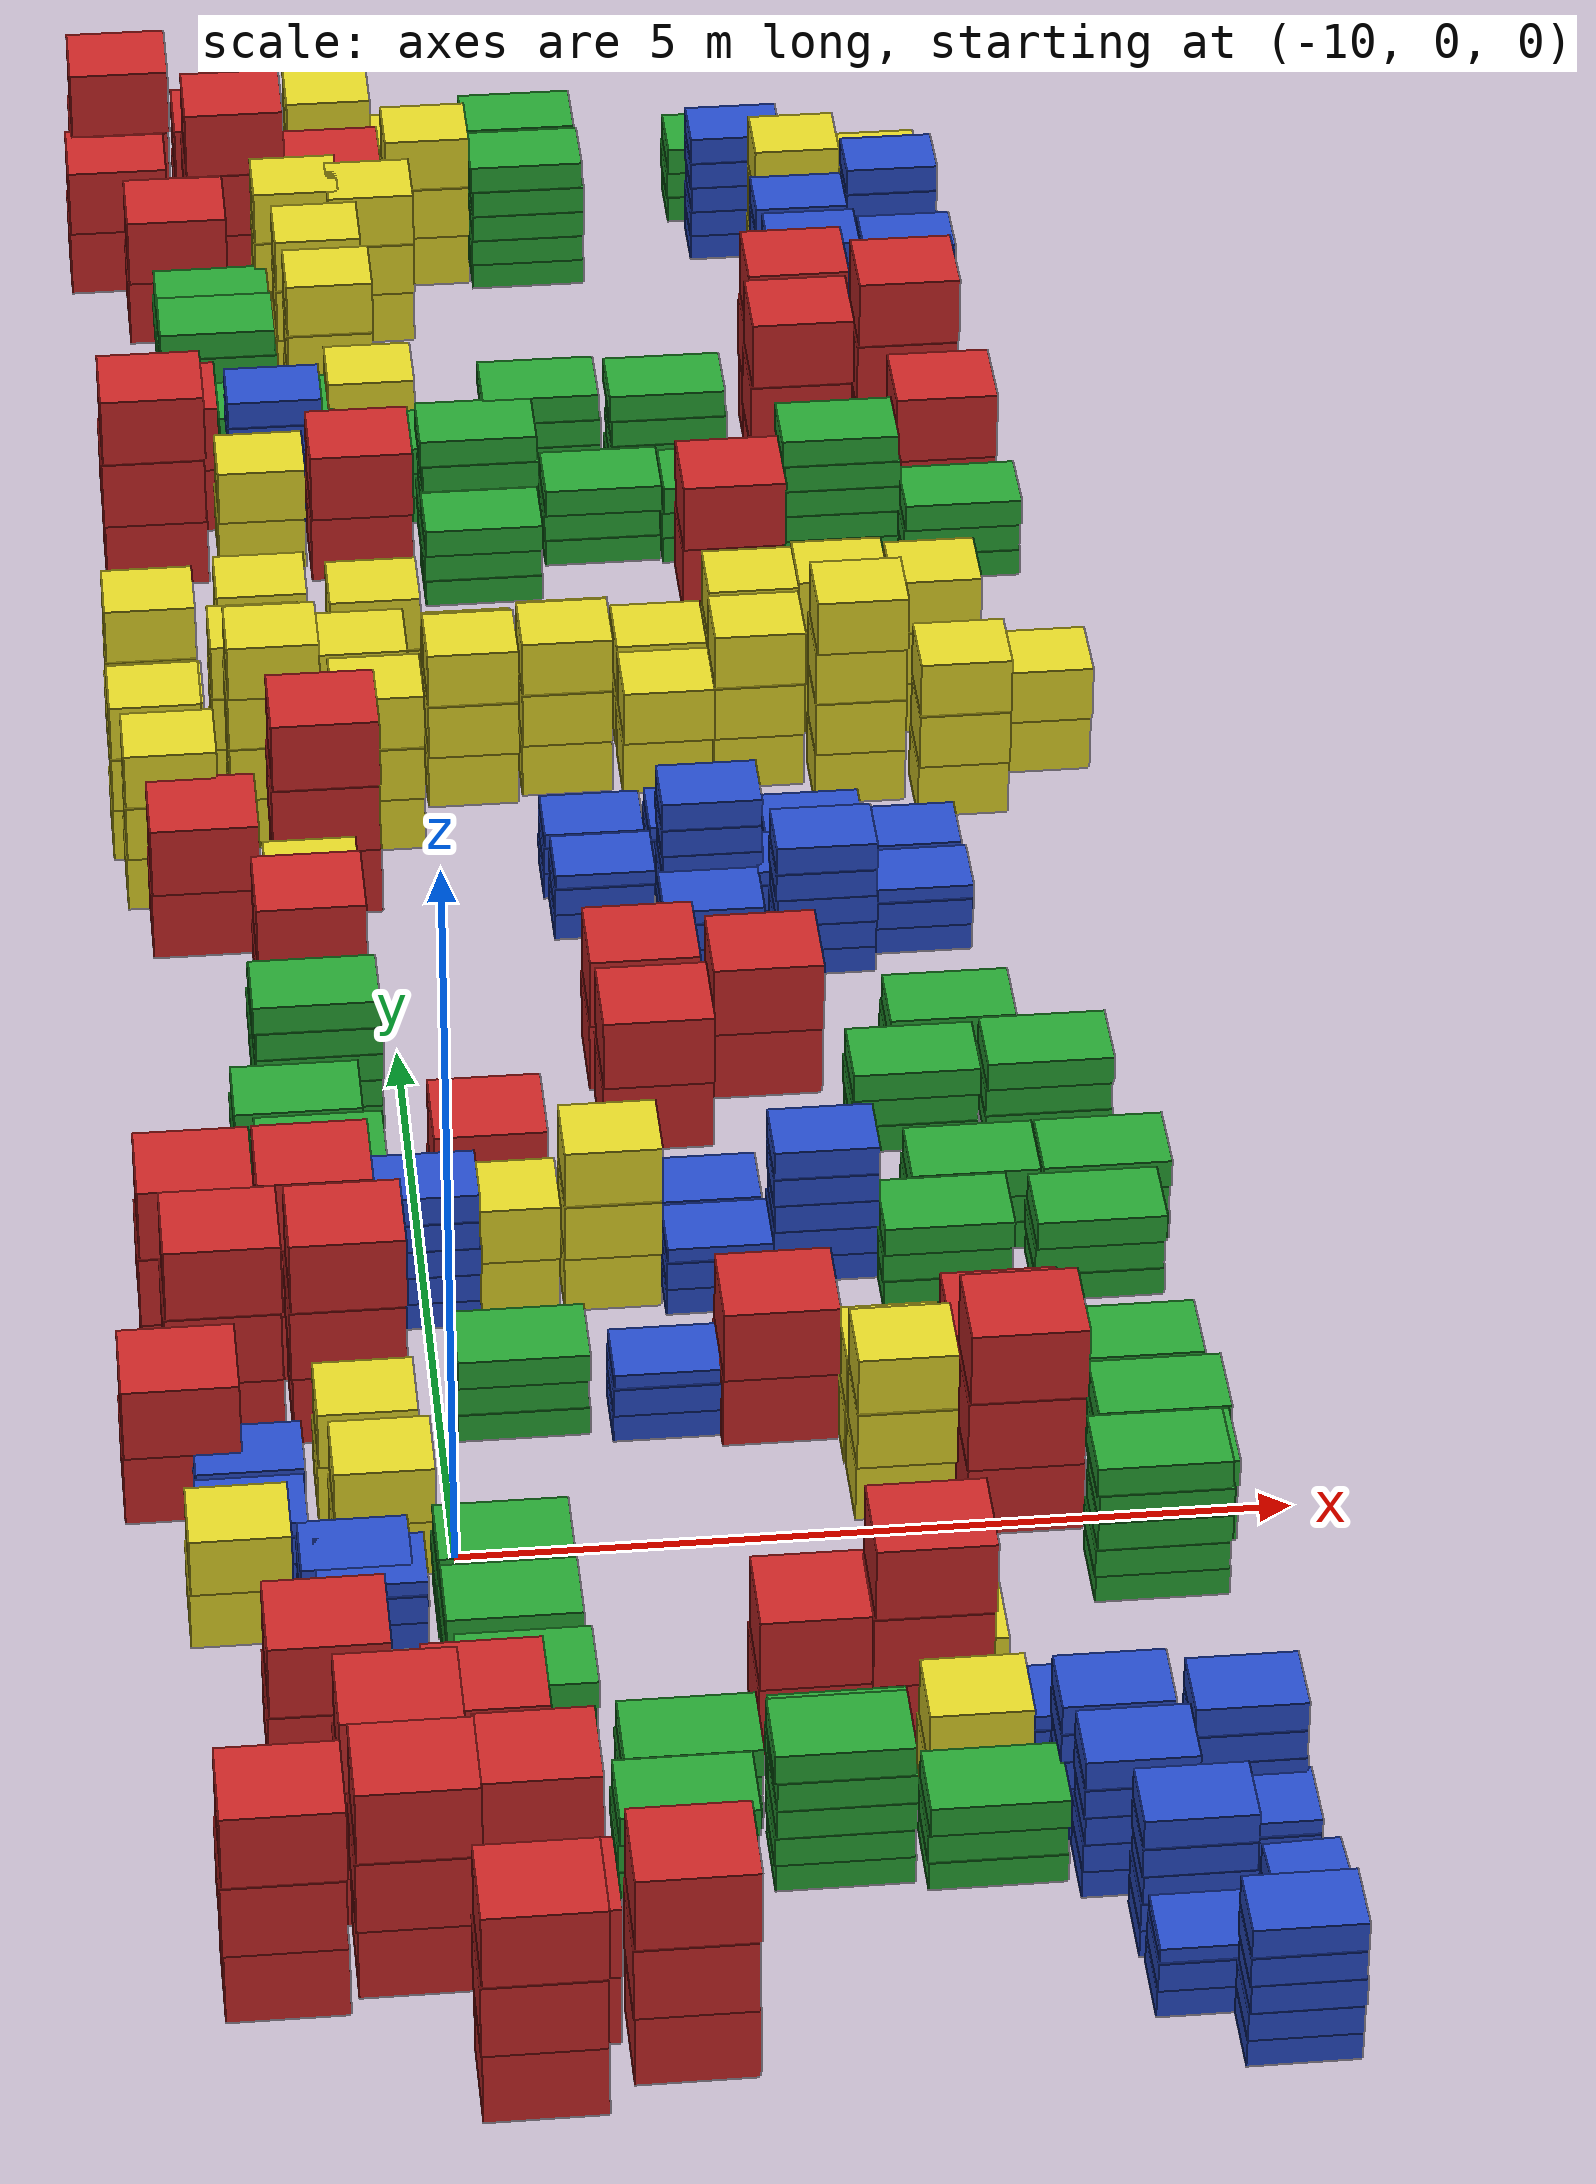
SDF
<?xml version="1.0" encoding="UTF-8"?>
<sdf version='1.4'>
    <model name="factory_baggage_group_B">
        <model name='baggage_C_x3_16'>
        <model name='baggage_C_0'>
            <static>1</static>
            <link name='link'>
            <collision name='collision'>
                <geometry>
                <box>
                    <size>0.6 0.5 0.4</size>
                </box>
                </geometry>
            </collision>
            <visual name='visual'>
                <geometry>
                <box>
                    <size>0.6 0.5 0.4</size>
                </box>
                </geometry>
                <material>
                <script>
                    <uri>file://media/materials/scripts/gazebo.material</uri>
                    <name>Gazebo/Yellow</name>
                </script>
                </material>
            </visual>
            </link>
            <pose frame=''>0 0 0.2 0 -0 0</pose>
        </model>
        <model name='baggage_C_1'>
            <static>1</static>
            <link name='link'>
            <collision name='collision'>
                <geometry>
                <box>
                    <size>0.6 0.5 0.4</size>
                </box>
                </geometry>
            </collision>
            <visual name='visual'>
                <geometry>
                <box>
                    <size>0.6 0.5 0.4</size>
                </box>
                </geometry>
                <material>
                <script>
                    <uri>file://media/materials/scripts/gazebo.material</uri>
                    <name>Gazebo/Yellow</name>
                </script>
                </material>
            </visual>
            </link>
            <pose frame=''>0.0062 -0.0069 0.6 0 -0 0</pose>
        </model>
        <model name='baggage_C_2'>
            <static>1</static>
            <link name='link'>
            <collision name='collision'>
                <geometry>
                <box>
                    <size>0.6 0.5 0.4</size>
                </box>
                </geometry>
            </collision>
            <visual name='visual'>
                <geometry>
                <box>
                    <size>0.6 0.5 0.4</size>
                </box>
                </geometry>
                <material>
                <script>
                    <uri>file://media/materials/scripts/gazebo.material</uri>
                    <name>Gazebo/Yellow</name>
                </script>
                </material>
            </visual>
            </link>
            <pose frame=''>0.0089 0.0083 1 0 -0 0</pose>
        </model>
        <pose frame=''>-11.3899 8.67797 0 0 -0 0</pose>
        </model>
        <model name='baggage_C_x2_19'>
        <model name='baggage_C_0'>
            <static>1</static>
            <link name='link'>
            <collision name='collision'>
                <geometry>
                <box>
                    <size>0.6 0.5 0.4</size>
                </box>
                </geometry>
            </collision>
            <visual name='visual'>
                <geometry>
                <box>
                    <size>0.6 0.5 0.4</size>
                </box>
                </geometry>
                <material>
                <script>
                    <uri>file://media/materials/scripts/gazebo.material</uri>
                    <name>Gazebo/Yellow</name>
                </script>
                </material>
            </visual>
            </link>
            <pose frame=''>0 0 0.2 0 -0 0</pose>
        </model>
        <model name='baggage_C_1'>
            <static>1</static>
            <link name='link'>
            <collision name='collision'>
                <geometry>
                <box>
                    <size>0.6 0.5 0.4</size>
                </box>
                </geometry>
            </collision>
            <visual name='visual'>
                <geometry>
                <box>
                    <size>0.6 0.5 0.4</size>
                </box>
                </geometry>
                <material>
                <script>
                    <uri>file://media/materials/scripts/gazebo.material</uri>
                    <name>Gazebo/Yellow</name>
                </script>
                </material>
            </visual>
            </link>
            <pose frame=''>0.0093 -0.002 0.6 0 -0 0</pose>
        </model>
        <pose frame=''>-11.3695 8.15878 0 0 -0 0</pose>
        </model>
        <model name='baggage_C_x3_17'>
        <model name='baggage_C_0'>
            <static>1</static>
            <link name='link'>
            <collision name='collision'>
                <geometry>
                <box>
                    <size>0.6 0.5 0.4</size>
                </box>
                </geometry>
            </collision>
            <visual name='visual'>
                <geometry>
                <box>
                    <size>0.6 0.5 0.4</size>
                </box>
                </geometry>
                <material>
                <script>
                    <uri>file://media/materials/scripts/gazebo.material</uri>
                    <name>Gazebo/Yellow</name>
                </script>
                </material>
            </visual>
            </link>
            <pose frame=''>0 0 0.2 0 -0 0</pose>
        </model>
        <model name='baggage_C_1'>
            <static>1</static>
            <link name='link'>
            <collision name='collision'>
                <geometry>
                <box>
                    <size>0.6 0.5 0.4</size>
                </box>
                </geometry>
            </collision>
            <visual name='visual'>
                <geometry>
                <box>
                    <size>0.6 0.5 0.4</size>
                </box>
                </geometry>
                <material>
                <script>
                    <uri>file://media/materials/scripts/gazebo.material</uri>
                    <name>Gazebo/Yellow</name>
                </script>
                </material>
            </visual>
            </link>
            <pose frame=''>0.0062 -0.0069 0.6 0 -0 0</pose>
        </model>
        <model name='baggage_C_2'>
            <static>1</static>
            <link name='link'>
            <collision name='collision'>
                <geometry>
                <box>
                    <size>0.6 0.5 0.4</size>
                </box>
                </geometry>
            </collision>
            <visual name='visual'>
                <geometry>
                <box>
                    <size>0.6 0.5 0.4</size>
                </box>
                </geometry>
                <material>
                <script>
                    <uri>file://media/materials/scripts/gazebo.material</uri>
                    <name>Gazebo/Yellow</name>
                </script>
                </material>
            </visual>
            </link>
            <pose frame=''>0.0089 0.0083 1 0 -0 0</pose>
        </model>
        <pose frame=''>-10.7137 8.18868 0 0 -0 0</pose>
        </model>
        <model name='baggage_C_x3_18'>
        <model name='baggage_C_0'>
            <static>1</static>
            <link name='link'>
            <collision name='collision'>
                <geometry>
                <box>
                    <size>0.6 0.5 0.4</size>
                </box>
                </geometry>
            </collision>
            <visual name='visual'>
                <geometry>
                <box>
                    <size>0.6 0.5 0.4</size>
                </box>
                </geometry>
                <material>
                <script>
                    <uri>file://media/materials/scripts/gazebo.material</uri>
                    <name>Gazebo/Yellow</name>
                </script>
                </material>
            </visual>
            </link>
            <pose frame=''>0 0 0.2 0 -0 0</pose>
        </model>
        <model name='baggage_C_1'>
            <static>1</static>
            <link name='link'>
            <collision name='collision'>
                <geometry>
                <box>
                    <size>0.6 0.5 0.4</size>
                </box>
                </geometry>
            </collision>
            <visual name='visual'>
                <geometry>
                <box>
                    <size>0.6 0.5 0.4</size>
                </box>
                </geometry>
                <material>
                <script>
                    <uri>file://media/materials/scripts/gazebo.material</uri>
                    <name>Gazebo/Yellow</name>
                </script>
                </material>
            </visual>
            </link>
            <pose frame=''>0.0062 -0.0069 0.6 0 -0 0</pose>
        </model>
        <model name='baggage_C_2'>
            <static>1</static>
            <link name='link'>
            <collision name='collision'>
                <geometry>
                <box>
                    <size>0.6 0.5 0.4</size>
                </box>
                </geometry>
            </collision>
            <visual name='visual'>
                <geometry>
                <box>
                    <size>0.6 0.5 0.4</size>
                </box>
                </geometry>
                <material>
                <script>
                    <uri>file://media/materials/scripts/gazebo.material</uri>
                    <name>Gazebo/Yellow</name>
                </script>
                </material>
            </visual>
            </link>
            <pose frame=''>0.0089 0.0083 1 0 -0 0</pose>
        </model>
        <pose frame=''>-11.405 7.55441 0 0 -0 0</pose>
        </model>
        <model name='baggage_C_x3_19'>
        <model name='baggage_C_0'>
            <static>1</static>
            <link name='link'>
            <collision name='collision'>
                <geometry>
                <box>
                    <size>0.6 0.5 0.4</size>
                </box>
                </geometry>
            </collision>
            <visual name='visual'>
                <geometry>
                <box>
                    <size>0.6 0.5 0.4</size>
                </box>
                </geometry>
                <material>
                <script>
                    <uri>file://media/materials/scripts/gazebo.material</uri>
                    <name>Gazebo/Yellow</name>
                </script>
                </material>
            </visual>
            </link>
            <pose frame=''>0 0 0.2 0 -0 0</pose>
        </model>
        <model name='baggage_C_1'>
            <static>1</static>
            <link name='link'>
            <collision name='collision'>
                <geometry>
                <box>
                    <size>0.6 0.5 0.4</size>
                </box>
                </geometry>
            </collision>
            <visual name='visual'>
                <geometry>
                <box>
                    <size>0.6 0.5 0.4</size>
                </box>
                </geometry>
                <material>
                <script>
                    <uri>file://media/materials/scripts/gazebo.material</uri>
                    <name>Gazebo/Yellow</name>
                </script>
                </material>
            </visual>
            </link>
            <pose frame=''>0.0062 -0.0069 0.6 0 -0 0</pose>
        </model>
        <model name='baggage_C_2'>
            <static>1</static>
            <link name='link'>
            <collision name='collision'>
                <geometry>
                <box>
                    <size>0.6 0.5 0.4</size>
                </box>
                </geometry>
            </collision>
            <visual name='visual'>
                <geometry>
                <box>
                    <size>0.6 0.5 0.4</size>
                </box>
                </geometry>
                <material>
                <script>
                    <uri>file://media/materials/scripts/gazebo.material</uri>
                    <name>Gazebo/Yellow</name>
                </script>
                </material>
            </visual>
            </link>
            <pose frame=''>0.0089 0.0083 1 0 -0 0</pose>
        </model>
        <pose frame=''>-10.6422 8.77616 0 0 -0 0</pose>
        </model>
        <model name='baggage_C_x3_20'>
        <model name='baggage_C_0'>
            <static>1</static>
            <link name='link'>
            <collision name='collision'>
                <geometry>
                <box>
                    <size>0.6 0.5 0.4</size>
                </box>
                </geometry>
            </collision>
            <visual name='visual'>
                <geometry>
                <box>
                    <size>0.6 0.5 0.4</size>
                </box>
                </geometry>
                <material>
                <script>
                    <uri>file://media/materials/scripts/gazebo.material</uri>
                    <name>Gazebo/Yellow</name>
                </script>
                </material>
            </visual>
            </link>
            <pose frame=''>0 0 0.2 0 -0 0</pose>
        </model>
        <model name='baggage_C_1'>
            <static>1</static>
            <link name='link'>
            <collision name='collision'>
                <geometry>
                <box>
                    <size>0.6 0.5 0.4</size>
                </box>
                </geometry>
            </collision>
            <visual name='visual'>
                <geometry>
                <box>
                    <size>0.6 0.5 0.4</size>
                </box>
                </geometry>
                <material>
                <script>
                    <uri>file://media/materials/scripts/gazebo.material</uri>
                    <name>Gazebo/Yellow</name>
                </script>
                </material>
            </visual>
            </link>
            <pose frame=''>0.0062 -0.0069 0.6 0 -0 0</pose>
        </model>
        <model name='baggage_C_2'>
            <static>1</static>
            <link name='link'>
            <collision name='collision'>
                <geometry>
                <box>
                    <size>0.6 0.5 0.4</size>
                </box>
                </geometry>
            </collision>
            <visual name='visual'>
                <geometry>
                <box>
                    <size>0.6 0.5 0.4</size>
                </box>
                </geometry>
                <material>
                <script>
                    <uri>file://media/materials/scripts/gazebo.material</uri>
                    <name>Gazebo/Yellow</name>
                </script>
                </material>
            </visual>
            </link>
            <pose frame=''>0.0089 0.0083 1 0 -0 0</pose>
        </model>
        <pose frame=''>-10.0284 8.039 0 0 -0 0</pose>
        </model>
        <model name='baggage_C_x4_2'>
        <model name='baggage_C_0'>
            <static>1</static>
            <link name='link'>
            <collision name='collision'>
                <geometry>
                <box>
                    <size>0.6 0.5 0.4</size>
                </box>
                </geometry>
            </collision>
            <visual name='visual'>
                <geometry>
                <box>
                    <size>0.6 0.5 0.4</size>
                </box>
                </geometry>
                <material>
                <script>
                    <uri>file://media/materials/scripts/gazebo.material</uri>
                    <name>Gazebo/Yellow</name>
                </script>
                </material>
            </visual>
            </link>
            <pose frame=''>0 0 0.2 0 -0 0</pose>
        </model>
        <model name='baggage_C_1'>
            <static>1</static>
            <link name='link'>
            <collision name='collision'>
                <geometry>
                <box>
                    <size>0.6 0.5 0.4</size>
                </box>
                </geometry>
            </collision>
            <visual name='visual'>
                <geometry>
                <box>
                    <size>0.6 0.5 0.4</size>
                </box>
                </geometry>
                <material>
                <script>
                    <uri>file://media/materials/scripts/gazebo.material</uri>
                    <name>Gazebo/Yellow</name>
                </script>
                </material>
            </visual>
            </link>
            <pose frame=''>0.0008 -0.0083 0.6 0 -0 0</pose>
        </model>
        <model name='baggage_C_2'>
            <static>1</static>
            <link name='link'>
            <collision name='collision'>
                <geometry>
                <box>
                    <size>0.6 0.5 0.4</size>
                </box>
                </geometry>
            </collision>
            <visual name='visual'>
                <geometry>
                <box>
                    <size>0.6 0.5 0.4</size>
                </box>
                </geometry>
                <material>
                <script>
                    <uri>file://media/materials/scripts/gazebo.material</uri>
                    <name>Gazebo/Yellow</name>
                </script>
                </material>
            </visual>
            </link>
            <pose frame=''>0.0001 0.0014 1 0 -0 0</pose>
        </model>
        <model name='baggage_C_3'>
            <static>1</static>
            <link name='link'>
            <collision name='collision'>
                <geometry>
                <box>
                    <size>0.6 0.5 0.4</size>
                </box>
                </geometry>
            </collision>
            <visual name='visual'>
                <geometry>
                <box>
                    <size>0.6 0.5 0.4</size>
                </box>
                </geometry>
                <material>
                <script>
                    <uri>file://media/materials/scripts/gazebo.material</uri>
                    <name>Gazebo/Yellow</name>
                </script>
                </material>
            </visual>
            </link>
            <pose frame=''>0.007 -0.0089 1.4 0 -0 0</pose>
        </model>
        <pose frame=''>-10.6261 7.59737 0 0 -0 0</pose>
        </model>
        <model name='baggage_C_x3_21'>
        <model name='baggage_C_0'>
            <static>1</static>
            <link name='link'>
            <collision name='collision'>
                <geometry>
                <box>
                    <size>0.6 0.5 0.4</size>
                </box>
                </geometry>
            </collision>
            <visual name='visual'>
                <geometry>
                <box>
                    <size>0.6 0.5 0.4</size>
                </box>
                </geometry>
                <material>
                <script>
                    <uri>file://media/materials/scripts/gazebo.material</uri>
                    <name>Gazebo/Yellow</name>
                </script>
                </material>
            </visual>
            </link>
            <pose frame=''>0 0 0.2 0 -0 0</pose>
        </model>
        <model name='baggage_C_1'>
            <static>1</static>
            <link name='link'>
            <collision name='collision'>
                <geometry>
                <box>
                    <size>0.6 0.5 0.4</size>
                </box>
                </geometry>
            </collision>
            <visual name='visual'>
                <geometry>
                <box>
                    <size>0.6 0.5 0.4</size>
                </box>
                </geometry>
                <material>
                <script>
                    <uri>file://media/materials/scripts/gazebo.material</uri>
                    <name>Gazebo/Yellow</name>
                </script>
                </material>
            </visual>
            </link>
            <pose frame=''>0.0062 -0.0069 0.6 0 -0 0</pose>
        </model>
        <model name='baggage_C_2'>
            <static>1</static>
            <link name='link'>
            <collision name='collision'>
                <geometry>
                <box>
                    <size>0.6 0.5 0.4</size>
                </box>
                </geometry>
            </collision>
            <visual name='visual'>
                <geometry>
                <box>
                    <size>0.6 0.5 0.4</size>
                </box>
                </geometry>
                <material>
                <script>
                    <uri>file://media/materials/scripts/gazebo.material</uri>
                    <name>Gazebo/Yellow</name>
                </script>
                </material>
            </visual>
            </link>
            <pose frame=''>0.0089 0.0083 1 0 -0 0</pose>
        </model>
        <pose frame=''>-9.90095 8.6419 0 0 -0 0</pose>
        </model>
        <model name='baggage_C_x3_22'>
        <model name='baggage_C_0'>
            <static>1</static>
            <link name='link'>
            <collision name='collision'>
                <geometry>
                <box>
                    <size>0.6 0.5 0.4</size>
                </box>
                </geometry>
            </collision>
            <visual name='visual'>
                <geometry>
                <box>
                    <size>0.6 0.5 0.4</size>
                </box>
                </geometry>
                <material>
                <script>
                    <uri>file://media/materials/scripts/gazebo.material</uri>
                    <name>Gazebo/Yellow</name>
                </script>
                </material>
            </visual>
            </link>
            <pose frame=''>0 0 0.2 0 -0 0</pose>
        </model>
        <model name='baggage_C_1'>
            <static>1</static>
            <link name='link'>
            <collision name='collision'>
                <geometry>
                <box>
                    <size>0.6 0.5 0.4</size>
                </box>
                </geometry>
            </collision>
            <visual name='visual'>
                <geometry>
                <box>
                    <size>0.6 0.5 0.4</size>
                </box>
                </geometry>
                <material>
                <script>
                    <uri>file://media/materials/scripts/gazebo.material</uri>
                    <name>Gazebo/Yellow</name>
                </script>
                </material>
            </visual>
            </link>
            <pose frame=''>0.0062 -0.0069 0.6 0 -0 0</pose>
        </model>
        <model name='baggage_C_2'>
            <static>1</static>
            <link name='link'>
            <collision name='collision'>
                <geometry>
                <box>
                    <size>0.6 0.5 0.4</size>
                </box>
                </geometry>
            </collision>
            <visual name='visual'>
                <geometry>
                <box>
                    <size>0.6 0.5 0.4</size>
                </box>
                </geometry>
                <material>
                <script>
                    <uri>file://media/materials/scripts/gazebo.material</uri>
                    <name>Gazebo/Yellow</name>
                </script>
                </material>
            </visual>
            </link>
            <pose frame=''>0.0089 0.0083 1 0 -0 0</pose>
        </model>
        <pose frame=''>-9.95676 7.50193 0 0 -0 0</pose>
        </model>
        <model name='baggage_C_x2_20'>
        <model name='baggage_C_0'>
            <static>1</static>
            <link name='link'>
            <collision name='collision'>
                <geometry>
                <box>
                    <size>0.6 0.5 0.4</size>
                </box>
                </geometry>
            </collision>
            <visual name='visual'>
                <geometry>
                <box>
                    <size>0.6 0.5 0.4</size>
                </box>
                </geometry>
                <material>
                <script>
                    <uri>file://media/materials/scripts/gazebo.material</uri>
                    <name>Gazebo/Yellow</name>
                </script>
                </material>
            </visual>
            </link>
            <pose frame=''>0 0 0.2 0 -0 0</pose>
        </model>
        <model name='baggage_C_1'>
            <static>1</static>
            <link name='link'>
            <collision name='collision'>
                <geometry>
                <box>
                    <size>0.6 0.5 0.4</size>
                </box>
                </geometry>
            </collision>
            <visual name='visual'>
                <geometry>
                <box>
                    <size>0.6 0.5 0.4</size>
                </box>
                </geometry>
                <material>
                <script>
                    <uri>file://media/materials/scripts/gazebo.material</uri>
                    <name>Gazebo/Yellow</name>
                </script>
                </material>
            </visual>
            </link>
            <pose frame=''>0.0093 -0.002 0.6 0 -0 0</pose>
        </model>
        <pose frame=''>-9.28245 8.58367 0 0 -0 0</pose>
        </model>
        <model name='baggage_C_x3_23'>
        <model name='baggage_C_0'>
            <static>1</static>
            <link name='link'>
            <collision name='collision'>
                <geometry>
                <box>
                    <size>0.6 0.5 0.4</size>
                </box>
                </geometry>
            </collision>
            <visual name='visual'>
                <geometry>
                <box>
                    <size>0.6 0.5 0.4</size>
                </box>
                </geometry>
                <material>
                <script>
                    <uri>file://media/materials/scripts/gazebo.material</uri>
                    <name>Gazebo/Yellow</name>
                </script>
                </material>
            </visual>
            </link>
            <pose frame=''>0 0 0.2 0 -0 0</pose>
        </model>
        <model name='baggage_C_1'>
            <static>1</static>
            <link name='link'>
            <collision name='collision'>
                <geometry>
                <box>
                    <size>0.6 0.5 0.4</size>
                </box>
                </geometry>
            </collision>
            <visual name='visual'>
                <geometry>
                <box>
                    <size>0.6 0.5 0.4</size>
                </box>
                </geometry>
                <material>
                <script>
                    <uri>file://media/materials/scripts/gazebo.material</uri>
                    <name>Gazebo/Yellow</name>
                </script>
                </material>
            </visual>
            </link>
            <pose frame=''>0.0062 -0.0069 0.6 0 -0 0</pose>
        </model>
        <model name='baggage_C_2'>
            <static>1</static>
            <link name='link'>
            <collision name='collision'>
                <geometry>
                <box>
                    <size>0.6 0.5 0.4</size>
                </box>
                </geometry>
            </collision>
            <visual name='visual'>
                <geometry>
                <box>
                    <size>0.6 0.5 0.4</size>
                </box>
                </geometry>
                <material>
                <script>
                    <uri>file://media/materials/scripts/gazebo.material</uri>
                    <name>Gazebo/Yellow</name>
                </script>
                </material>
            </visual>
            </link>
            <pose frame=''>0.0089 0.0083 1 0 -0 0</pose>
        </model>
        <pose frame=''>-9.30431 7.95913 0 0 -0 0</pose>
        </model>
        <model name='baggage_C_x2_21'>
        <model name='baggage_C_0'>
            <static>1</static>
            <link name='link'>
            <collision name='collision'>
                <geometry>
                <box>
                    <size>0.6 0.5 0.4</size>
                </box>
                </geometry>
            </collision>
            <visual name='visual'>
                <geometry>
                <box>
                    <size>0.6 0.5 0.4</size>
                </box>
                </geometry>
                <material>
                <script>
                    <uri>file://media/materials/scripts/gazebo.material</uri>
                    <name>Gazebo/Yellow</name>
                </script>
                </material>
            </visual>
            </link>
            <pose frame=''>0 0 0.2 0 -0 0</pose>
        </model>
        <model name='baggage_C_1'>
            <static>1</static>
            <link name='link'>
            <collision name='collision'>
                <geometry>
                <box>
                    <size>0.6 0.5 0.4</size>
                </box>
                </geometry>
            </collision>
            <visual name='visual'>
                <geometry>
                <box>
                    <size>0.6 0.5 0.4</size>
                </box>
                </geometry>
                <material>
                <script>
                    <uri>file://media/materials/scripts/gazebo.material</uri>
                    <name>Gazebo/Yellow</name>
                </script>
                </material>
            </visual>
            </link>
            <pose frame=''>0.0093 -0.002 0.6 0 -0 0</pose>
        </model>
        <pose frame=''>-8.62419 8.64939 0 0 -0 0</pose>
        </model>
        <model name='baggage_C_x3_24'>
        <model name='baggage_C_0'>
            <static>1</static>
            <link name='link'>
            <collision name='collision'>
                <geometry>
                <box>
                    <size>0.6 0.5 0.4</size>
                </box>
                </geometry>
            </collision>
            <visual name='visual'>
                <geometry>
                <box>
                    <size>0.6 0.5 0.4</size>
                </box>
                </geometry>
                <material>
                <script>
                    <uri>file://media/materials/scripts/gazebo.material</uri>
                    <name>Gazebo/Yellow</name>
                </script>
                </material>
            </visual>
            </link>
            <pose frame=''>0 0 0.2 0 -0 0</pose>
        </model>
        <model name='baggage_C_1'>
            <static>1</static>
            <link name='link'>
            <collision name='collision'>
                <geometry>
                <box>
                    <size>0.6 0.5 0.4</size>
                </box>
                </geometry>
            </collision>
            <visual name='visual'>
                <geometry>
                <box>
                    <size>0.6 0.5 0.4</size>
                </box>
                </geometry>
                <material>
                <script>
                    <uri>file://media/materials/scripts/gazebo.material</uri>
                    <name>Gazebo/Yellow</name>
                </script>
                </material>
            </visual>
            </link>
            <pose frame=''>0.0062 -0.0069 0.6 0 -0 0</pose>
        </model>
        <model name='baggage_C_2'>
            <static>1</static>
            <link name='link'>
            <collision name='collision'>
                <geometry>
                <box>
                    <size>0.6 0.5 0.4</size>
                </box>
                </geometry>
            </collision>
            <visual name='visual'>
                <geometry>
                <box>
                    <size>0.6 0.5 0.4</size>
                </box>
                </geometry>
                <material>
                <script>
                    <uri>file://media/materials/scripts/gazebo.material</uri>
                    <name>Gazebo/Yellow</name>
                </script>
                </material>
            </visual>
            </link>
            <pose frame=''>0.0089 0.0083 1 0 -0 0</pose>
        </model>
        <pose frame=''>-8.67626 8.03335 0 0 -0 0</pose>
        </model>
        <model name='baggage_C_x2_22'>
        <model name='baggage_C_0'>
            <static>1</static>
            <link name='link'>
            <collision name='collision'>
                <geometry>
                <box>
                    <size>0.6 0.5 0.4</size>
                </box>
                </geometry>
            </collision>
            <visual name='visual'>
                <geometry>
                <box>
                    <size>0.6 0.5 0.4</size>
                </box>
                </geometry>
                <material>
                <script>
                    <uri>file://media/materials/scripts/gazebo.material</uri>
                    <name>Gazebo/Yellow</name>
                </script>
                </material>
            </visual>
            </link>
            <pose frame=''>0 0 0.2 0 -0 0</pose>
        </model>
        <model name='baggage_C_1'>
            <static>1</static>
            <link name='link'>
            <collision name='collision'>
                <geometry>
                <box>
                    <size>0.6 0.5 0.4</size>
                </box>
                </geometry>
            </collision>
            <visual name='visual'>
                <geometry>
                <box>
                    <size>0.6 0.5 0.4</size>
                </box>
                </geometry>
                <material>
                <script>
                    <uri>file://media/materials/scripts/gazebo.material</uri>
                    <name>Gazebo/Yellow</name>
                </script>
                </material>
            </visual>
            </link>
            <pose frame=''>0.0093 -0.002 0.6 0 -0 0</pose>
        </model>
        <pose frame=''>-8.00907 8.54859 0 0 -0 0</pose>
        </model>
        <model name='baggage_C_x3_25'>
        <model name='baggage_C_0'>
            <static>1</static>
            <link name='link'>
            <collision name='collision'>
                <geometry>
                <box>
                    <size>0.6 0.5 0.4</size>
                </box>
                </geometry>
            </collision>
            <visual name='visual'>
                <geometry>
                <box>
                    <size>0.6 0.5 0.4</size>
                </box>
                </geometry>
                <material>
                <script>
                    <uri>file://media/materials/scripts/gazebo.material</uri>
                    <name>Gazebo/Yellow</name>
                </script>
                </material>
            </visual>
            </link>
            <pose frame=''>0 0 0.2 0 -0 0</pose>
        </model>
        <model name='baggage_C_1'>
            <static>1</static>
            <link name='link'>
            <collision name='collision'>
                <geometry>
                <box>
                    <size>0.6 0.5 0.4</size>
                </box>
                </geometry>
            </collision>
            <visual name='visual'>
                <geometry>
                <box>
                    <size>0.6 0.5 0.4</size>
                </box>
                </geometry>
                <material>
                <script>
                    <uri>file://media/materials/scripts/gazebo.material</uri>
                    <name>Gazebo/Yellow</name>
                </script>
                </material>
            </visual>
            </link>
            <pose frame=''>0.0062 -0.0069 0.6 0 -0 0</pose>
        </model>
        <model name='baggage_C_2'>
            <static>1</static>
            <link name='link'>
            <collision name='collision'>
                <geometry>
                <box>
                    <size>0.6 0.5 0.4</size>
                </box>
                </geometry>
            </collision>
            <visual name='visual'>
                <geometry>
                <box>
                    <size>0.6 0.5 0.4</size>
                </box>
                </geometry>
                <material>
                <script>
                    <uri>file://media/materials/scripts/gazebo.material</uri>
                    <name>Gazebo/Yellow</name>
                </script>
                </material>
            </visual>
            </link>
            <pose frame=''>0.0089 0.0083 1 0 -0 0</pose>
        </model>
        <pose frame=''>-7.39535 8.52937 0 0 -0 0</pose>
        </model>
        <model name='baggage_C_x3_26'>
        <model name='baggage_C_0'>
            <static>1</static>
            <link name='link'>
            <collision name='collision'>
                <geometry>
                <box>
                    <size>0.6 0.5 0.4</size>
                </box>
                </geometry>
            </collision>
            <visual name='visual'>
                <geometry>
                <box>
                    <size>0.6 0.5 0.4</size>
                </box>
                </geometry>
                <material>
                <script>
                    <uri>file://media/materials/scripts/gazebo.material</uri>
                    <name>Gazebo/Yellow</name>
                </script>
                </material>
            </visual>
            </link>
            <pose frame=''>0 0 0.2 0 -0 0</pose>
        </model>
        <model name='baggage_C_1'>
            <static>1</static>
            <link name='link'>
            <collision name='collision'>
                <geometry>
                <box>
                    <size>0.6 0.5 0.4</size>
                </box>
                </geometry>
            </collision>
            <visual name='visual'>
                <geometry>
                <box>
                    <size>0.6 0.5 0.4</size>
                </box>
                </geometry>
                <material>
                <script>
                    <uri>file://media/materials/scripts/gazebo.material</uri>
                    <name>Gazebo/Yellow</name>
                </script>
                </material>
            </visual>
            </link>
            <pose frame=''>0.0062 -0.0069 0.6 0 -0 0</pose>
        </model>
        <model name='baggage_C_2'>
            <static>1</static>
            <link name='link'>
            <collision name='collision'>
                <geometry>
                <box>
                    <size>0.6 0.5 0.4</size>
                </box>
                </geometry>
            </collision>
            <visual name='visual'>
                <geometry>
                <box>
                    <size>0.6 0.5 0.4</size>
                </box>
                </geometry>
                <material>
                <script>
                    <uri>file://media/materials/scripts/gazebo.material</uri>
                    <name>Gazebo/Yellow</name>
                </script>
                </material>
            </visual>
            </link>
            <pose frame=''>0.0089 0.0083 1 0 -0 0</pose>
        </model>
        <pose frame=''>-6.78982 8.58261 0 0 -0 0</pose>
        </model>
        <model name='baggage_C_x3_27'>
        <model name='baggage_C_0'>
            <static>1</static>
            <link name='link'>
            <collision name='collision'>
                <geometry>
                <box>
                    <size>0.6 0.5 0.4</size>
                </box>
                </geometry>
            </collision>
            <visual name='visual'>
                <geometry>
                <box>
                    <size>0.6 0.5 0.4</size>
                </box>
                </geometry>
                <material>
                <script>
                    <uri>file://media/materials/scripts/gazebo.material</uri>
                    <name>Gazebo/Yellow</name>
                </script>
                </material>
            </visual>
            </link>
            <pose frame=''>0 0 0.2 0 -0 0</pose>
        </model>
        <model name='baggage_C_1'>
            <static>1</static>
            <link name='link'>
            <collision name='collision'>
                <geometry>
                <box>
                    <size>0.6 0.5 0.4</size>
                </box>
                </geometry>
            </collision>
            <visual name='visual'>
                <geometry>
                <box>
                    <size>0.6 0.5 0.4</size>
                </box>
                </geometry>
                <material>
                <script>
                    <uri>file://media/materials/scripts/gazebo.material</uri>
                    <name>Gazebo/Yellow</name>
                </script>
                </material>
            </visual>
            </link>
            <pose frame=''>0.0062 -0.0069 0.6 0 -0 0</pose>
        </model>
        <model name='baggage_C_2'>
            <static>1</static>
            <link name='link'>
            <collision name='collision'>
                <geometry>
                <box>
                    <size>0.6 0.5 0.4</size>
                </box>
                </geometry>
            </collision>
            <visual name='visual'>
                <geometry>
                <box>
                    <size>0.6 0.5 0.4</size>
                </box>
                </geometry>
                <material>
                <script>
                    <uri>file://media/materials/scripts/gazebo.material</uri>
                    <name>Gazebo/Yellow</name>
                </script>
                </material>
            </visual>
            </link>
            <pose frame=''>0.0089 0.0083 1 0 -0 0</pose>
        </model>
        <pose frame=''>-6.17452 8.52259 0 0 -0 0</pose>
        </model>
        <model name='baggage_C_x2_23'>
        <model name='baggage_C_0'>
            <static>1</static>
            <link name='link'>
            <collision name='collision'>
                <geometry>
                <box>
                    <size>0.6 0.5 0.4</size>
                </box>
                </geometry>
            </collision>
            <visual name='visual'>
                <geometry>
                <box>
                    <size>0.6 0.5 0.4</size>
                </box>
                </geometry>
                <material>
                <script>
                    <uri>file://media/materials/scripts/gazebo.material</uri>
                    <name>Gazebo/Yellow</name>
                </script>
                </material>
            </visual>
            </link>
            <pose frame=''>0 0 0.2 0 -0 0</pose>
        </model>
        <model name='baggage_C_1'>
            <static>1</static>
            <link name='link'>
            <collision name='collision'>
                <geometry>
                <box>
                    <size>0.6 0.5 0.4</size>
                </box>
                </geometry>
            </collision>
            <visual name='visual'>
                <geometry>
                <box>
                    <size>0.6 0.5 0.4</size>
                </box>
                </geometry>
                <material>
                <script>
                    <uri>file://media/materials/scripts/gazebo.material</uri>
                    <name>Gazebo/Yellow</name>
                </script>
                </material>
            </visual>
            </link>
            <pose frame=''>0.0093 -0.002 0.6 0 -0 0</pose>
        </model>
        <pose frame=''>-8.01024 7.98836 0 0 -0 0</pose>
        </model>
        <model name='baggage_C_x3_28'>
        <model name='baggage_C_0'>
            <static>1</static>
            <link name='link'>
            <collision name='collision'>
                <geometry>
                <box>
                    <size>0.6 0.5 0.4</size>
                </box>
                </geometry>
            </collision>
            <visual name='visual'>
                <geometry>
                <box>
                    <size>0.6 0.5 0.4</size>
                </box>
                </geometry>
                <material>
                <script>
                    <uri>file://media/materials/scripts/gazebo.material</uri>
                    <name>Gazebo/Yellow</name>
                </script>
                </material>
            </visual>
            </link>
            <pose frame=''>0 0 0.2 0 -0 0</pose>
        </model>
        <model name='baggage_C_1'>
            <static>1</static>
            <link name='link'>
            <collision name='collision'>
                <geometry>
                <box>
                    <size>0.6 0.5 0.4</size>
                </box>
                </geometry>
            </collision>
            <visual name='visual'>
                <geometry>
                <box>
                    <size>0.6 0.5 0.4</size>
                </box>
                </geometry>
                <material>
                <script>
                    <uri>file://media/materials/scripts/gazebo.material</uri>
                    <name>Gazebo/Yellow</name>
                </script>
                </material>
            </visual>
            </link>
            <pose frame=''>0.0062 -0.0069 0.6 0 -0 0</pose>
        </model>
        <model name='baggage_C_2'>
            <static>1</static>
            <link name='link'>
            <collision name='collision'>
                <geometry>
                <box>
                    <size>0.6 0.5 0.4</size>
                </box>
                </geometry>
            </collision>
            <visual name='visual'>
                <geometry>
                <box>
                    <size>0.6 0.5 0.4</size>
                </box>
                </geometry>
                <material>
                <script>
                    <uri>file://media/materials/scripts/gazebo.material</uri>
                    <name>Gazebo/Yellow</name>
                </script>
                </material>
            </visual>
            </link>
            <pose frame=''>0.0089 0.0083 1 0 -0 0</pose>
        </model>
        <pose frame=''>-7.40596 7.99309 0 0 -0 0</pose>
        </model>
        <model name='baggage_B_x3_14'>
        <model name='baggage_B_0'>
            <static>1</static>
            <link name='link'>
            <collision name='collision'>
                <geometry>
                <box>
                    <size>0.65 0.45 0.2</size>
                </box>
                </geometry>
            </collision>
            <visual name='visual'>
                <geometry>
                <box>
                    <size>0.65 0.45 0.2</size>
                </box>
                </geometry>
                <material>
                <script>
                    <uri>file://media/materials/scripts/gazebo.material</uri>
                    <name>Gazebo/Blue</name>
                </script>
                </material>
            </visual>
            </link>
            <pose frame=''>0 0 0.1 0 -0 0</pose>
        </model>
        <model name='baggage_B_1'>
            <static>1</static>
            <link name='link'>
            <collision name='collision'>
                <geometry>
                <box>
                    <size>0.65 0.45 0.2</size>
                </box>
                </geometry>
            </collision>
            <visual name='visual'>
                <geometry>
                <box>
                    <size>0.65 0.45 0.2</size>
                </box>
                </geometry>
                <material>
                <script>
                    <uri>file://media/materials/scripts/gazebo.material</uri>
                    <name>Gazebo/Blue</name>
                </script>
                </material>
            </visual>
            </link>
            <pose frame=''>0.0028 -0.0086 0.3 0 -0 0</pose>
        </model>
        <model name='baggage_B_2'>
            <static>1</static>
            <link name='link'>
            <collision name='collision'>
                <geometry>
                <box>
                    <size>0.65 0.45 0.2</size>
                </box>
                </geometry>
            </collision>
            <visual name='visual'>
                <geometry>
                <box>
                    <size>0.65 0.45 0.2</size>
                </box>
                </geometry>
                <material>
                <script>
                    <uri>file://media/materials/scripts/gazebo.material</uri>
                    <name>Gazebo/Blue</name>
                </script>
                </material>
            </visual>
            </link>
            <pose frame=''>0.0092 0.006 0.4 0 -0 0</pose>
        </model>
        <pose frame=''>-8.60522 6.83115 0 0 -0 0</pose>
        </model>
        <model name='baggage_B_x3_15'>
        <model name='baggage_B_0'>
            <static>1</static>
            <link name='link'>
            <collision name='collision'>
                <geometry>
                <box>
                    <size>0.65 0.45 0.2</size>
                </box>
                </geometry>
            </collision>
            <visual name='visual'>
                <geometry>
                <box>
                    <size>0.65 0.45 0.2</size>
                </box>
                </geometry>
                <material>
                <script>
                    <uri>file://media/materials/scripts/gazebo.material</uri>
                    <name>Gazebo/Blue</name>
                </script>
                </material>
            </visual>
            </link>
            <pose frame=''>0 0 0.1 0 -0 0</pose>
        </model>
        <model name='baggage_B_1'>
            <static>1</static>
            <link name='link'>
            <collision name='collision'>
                <geometry>
                <box>
                    <size>0.65 0.45 0.2</size>
                </box>
                </geometry>
            </collision>
            <visual name='visual'>
                <geometry>
                <box>
                    <size>0.65 0.45 0.2</size>
                </box>
                </geometry>
                <material>
                <script>
                    <uri>file://media/materials/scripts/gazebo.material</uri>
                    <name>Gazebo/Blue</name>
                </script>
                </material>
            </visual>
            </link>
            <pose frame=''>0.0028 -0.0086 0.3 0 -0 0</pose>
        </model>
        <model name='baggage_B_2'>
            <static>1</static>
            <link name='link'>
            <collision name='collision'>
                <geometry>
                <box>
                    <size>0.65 0.45 0.2</size>
                </box>
                </geometry>
            </collision>
            <visual name='visual'>
                <geometry>
                <box>
                    <size>0.65 0.45 0.2</size>
                </box>
                </geometry>
                <material>
                <script>
                    <uri>file://media/materials/scripts/gazebo.material</uri>
                    <name>Gazebo/Blue</name>
                </script>
                </material>
            </visual>
            </link>
            <pose frame=''>0.0092 0.006 0.4 0 -0 0</pose>
        </model>
        <pose frame=''>-7.91816 6.85061 0 0 -0 0</pose>
        </model>
        <model name='baggage_B_x3_16'>
        <model name='baggage_B_0'>
            <static>1</static>
            <link name='link'>
            <collision name='collision'>
                <geometry>
                <box>
                    <size>0.65 0.45 0.2</size>
                </box>
                </geometry>
            </collision>
            <visual name='visual'>
                <geometry>
                <box>
                    <size>0.65 0.45 0.2</size>
                </box>
                </geometry>
                <material>
                <script>
                    <uri>file://media/materials/scripts/gazebo.material</uri>
                    <name>Gazebo/Blue</name>
                </script>
                </material>
            </visual>
            </link>
            <pose frame=''>0 0 0.1 0 -0 0</pose>
        </model>
        <model name='baggage_B_1'>
            <static>1</static>
            <link name='link'>
            <collision name='collision'>
                <geometry>
                <box>
                    <size>0.65 0.45 0.2</size>
                </box>
                </geometry>
            </collision>
            <visual name='visual'>
                <geometry>
                <box>
                    <size>0.65 0.45 0.2</size>
                </box>
                </geometry>
                <material>
                <script>
                    <uri>file://media/materials/scripts/gazebo.material</uri>
                    <name>Gazebo/Blue</name>
                </script>
                </material>
            </visual>
            </link>
            <pose frame=''>0.0028 -0.0086 0.3 0 -0 0</pose>
        </model>
        <model name='baggage_B_2'>
            <static>1</static>
            <link name='link'>
            <collision name='collision'>
                <geometry>
                <box>
                    <size>0.65 0.45 0.2</size>
                </box>
                </geometry>
            </collision>
            <visual name='visual'>
                <geometry>
                <box>
                    <size>0.65 0.45 0.2</size>
                </box>
                </geometry>
                <material>
                <script>
                    <uri>file://media/materials/scripts/gazebo.material</uri>
                    <name>Gazebo/Blue</name>
                </script>
                </material>
            </visual>
            </link>
            <pose frame=''>0.0092 0.006 0.4 0 -0 0</pose>
        </model>
        <pose frame=''>-8.57325 6.36856 0 0 -0 0</pose>
        </model>
        <model name='baggage_B_x5_15'>
        <model name='baggage_B_0'>
            <static>1</static>
            <link name='link'>
            <collision name='collision'>
                <geometry>
                <box>
                    <size>0.65 0.45 0.2</size>
                </box>
                </geometry>
            </collision>
            <visual name='visual'>
                <geometry>
                <box>
                    <size>0.65 0.45 0.2</size>
                </box>
                </geometry>
                <material>
                <script>
                    <uri>file://media/materials/scripts/gazebo.material</uri>
                    <name>Gazebo/Blue</name>
                </script>
                </material>
            </visual>
            </link>
            <pose frame=''>0 0 0.1 0 -0 0</pose>
        </model>
        <model name='baggage_B_1'>
            <static>1</static>
            <link name='link'>
            <collision name='collision'>
                <geometry>
                <box>
                    <size>0.65 0.45 0.2</size>
                </box>
                </geometry>
            </collision>
            <visual name='visual'>
                <geometry>
                <box>
                    <size>0.65 0.45 0.2</size>
                </box>
                </geometry>
                <material>
                <script>
                    <uri>file://media/materials/scripts/gazebo.material</uri>
                    <name>Gazebo/Blue</name>
                </script>
                </material>
            </visual>
            </link>
            <pose frame=''>-0.0014 -0.0091 0.3 0 -0 0</pose>
        </model>
        <model name='baggage_B_2'>
            <static>1</static>
            <link name='link'>
            <collision name='collision'>
                <geometry>
                <box>
                    <size>0.65 0.45 0.2</size>
                </box>
                </geometry>
            </collision>
            <visual name='visual'>
                <geometry>
                <box>
                    <size>0.65 0.45 0.2</size>
                </box>
                </geometry>
                <material>
                <script>
                    <uri>file://media/materials/scripts/gazebo.material</uri>
                    <name>Gazebo/Blue</name>
                </script>
                </material>
            </visual>
            </link>
            <pose frame=''>0.0076 -0.0066 0.5 0 -0 0</pose>
        </model>
        <model name='baggage_B_3'>
            <static>1</static>
            <link name='link'>
            <collision name='collision'>
                <geometry>
                <box>
                    <size>0.65 0.45 0.2</size>
                </box>
                </geometry>
            </collision>
            <visual name='visual'>
                <geometry>
                <box>
                    <size>0.65 0.45 0.2</size>
                </box>
                </geometry>
                <material>
                <script>
                    <uri>file://media/materials/scripts/gazebo.material</uri>
                    <name>Gazebo/Blue</name>
                </script>
                </material>
            </visual>
            </link>
            <pose frame=''>0 -0.0032 0.7 0 -0 0</pose>
        </model>
        <model name='baggage_B_4'>
            <static>1</static>
            <link name='link'>
            <collision name='collision'>
                <geometry>
                <box>
                    <size>0.65 0.45 0.2</size>
                </box>
                </geometry>
            </collision>
            <visual name='visual'>
                <geometry>
                <box>
                    <size>0.65 0.45 0.2</size>
                </box>
                </geometry>
                <material>
                <script>
                    <uri>file://media/materials/scripts/gazebo.material</uri>
                    <name>Gazebo/Blue</name>
                </script>
                </material>
            </visual>
            </link>
            <pose frame=''>0.0023 0.0073 0.9 0 -0 0</pose>
        </model>
        <pose frame=''>-7.8733 6.38805 0 0 -0 0</pose>
        </model>
        <model name='baggage_C_x4_3'>
        <model name='baggage_C_0'>
            <static>1</static>
            <link name='link'>
            <collision name='collision'>
                <geometry>
                <box>
                    <size>0.6 0.5 0.4</size>
                </box>
                </geometry>
            </collision>
            <visual name='visual'>
                <geometry>
                <box>
                    <size>0.6 0.5 0.4</size>
                </box>
                </geometry>
                <material>
                <script>
                    <uri>file://media/materials/scripts/gazebo.material</uri>
                    <name>Gazebo/Yellow</name>
                </script>
                </material>
            </visual>
            </link>
            <pose frame=''>0 0 0.2 0 -0 0</pose>
        </model>
        <model name='baggage_C_1'>
            <static>1</static>
            <link name='link'>
            <collision name='collision'>
                <geometry>
                <box>
                    <size>0.6 0.5 0.4</size>
                </box>
                </geometry>
            </collision>
            <visual name='visual'>
                <geometry>
                <box>
                    <size>0.6 0.5 0.4</size>
                </box>
                </geometry>
                <material>
                <script>
                    <uri>file://media/materials/scripts/gazebo.material</uri>
                    <name>Gazebo/Yellow</name>
                </script>
                </material>
            </visual>
            </link>
            <pose frame=''>0.0008 -0.0083 0.6 0 -0 0</pose>
        </model>
        <model name='baggage_C_2'>
            <static>1</static>
            <link name='link'>
            <collision name='collision'>
                <geometry>
                <box>
                    <size>0.6 0.5 0.4</size>
                </box>
                </geometry>
            </collision>
            <visual name='visual'>
                <geometry>
                <box>
                    <size>0.6 0.5 0.4</size>
                </box>
                </geometry>
                <material>
                <script>
                    <uri>file://media/materials/scripts/gazebo.material</uri>
                    <name>Gazebo/Yellow</name>
                </script>
                </material>
            </visual>
            </link>
            <pose frame=''>0.0001 0.0014 1 0 -0 0</pose>
        </model>
        <model name='baggage_C_3'>
            <static>1</static>
            <link name='link'>
            <collision name='collision'>
                <geometry>
                <box>
                    <size>0.6 0.5 0.4</size>
                </box>
                </geometry>
            </collision>
            <visual name='visual'>
                <geometry>
                <box>
                    <size>0.6 0.5 0.4</size>
                </box>
                </geometry>
                <material>
                <script>
                    <uri>file://media/materials/scripts/gazebo.material</uri>
                    <name>Gazebo/Yellow</name>
                </script>
                </material>
            </visual>
            </link>
            <pose frame=''>0.007 -0.0089 1.4 0 -0 0</pose>
        </model>
        <pose frame=''>-6.75581 7.75037 0 0 -0 0</pose>
        </model>
        <model name='baggage_C_x3_29'>
        <model name='baggage_C_0'>
            <static>1</static>
            <link name='link'>
            <collision name='collision'>
                <geometry>
                <box>
                    <size>0.6 0.5 0.4</size>
                </box>
                </geometry>
            </collision>
            <visual name='visual'>
                <geometry>
                <box>
                    <size>0.6 0.5 0.4</size>
                </box>
                </geometry>
                <material>
                <script>
                    <uri>file://media/materials/scripts/gazebo.material</uri>
                    <name>Gazebo/Yellow</name>
                </script>
                </material>
            </visual>
            </link>
            <pose frame=''>0 0 0.2 0 -0 0</pose>
        </model>
        <model name='baggage_C_1'>
            <static>1</static>
            <link name='link'>
            <collision name='collision'>
                <geometry>
                <box>
                    <size>0.6 0.5 0.4</size>
                </box>
                </geometry>
            </collision>
            <visual name='visual'>
                <geometry>
                <box>
                    <size>0.6 0.5 0.4</size>
                </box>
                </geometry>
                <material>
                <script>
                    <uri>file://media/materials/scripts/gazebo.material</uri>
                    <name>Gazebo/Yellow</name>
                </script>
                </material>
            </visual>
            </link>
            <pose frame=''>0.0062 -0.0069 0.6 0 -0 0</pose>
        </model>
        <model name='baggage_C_2'>
            <static>1</static>
            <link name='link'>
            <collision name='collision'>
                <geometry>
                <box>
                    <size>0.6 0.5 0.4</size>
                </box>
                </geometry>
            </collision>
            <visual name='visual'>
                <geometry>
                <box>
                    <size>0.6 0.5 0.4</size>
                </box>
                </geometry>
                <material>
                <script>
                    <uri>file://media/materials/scripts/gazebo.material</uri>
                    <name>Gazebo/Yellow</name>
                </script>
                </material>
            </visual>
            </link>
            <pose frame=''>0.0089 0.0083 1 0 -0 0</pose>
        </model>
        <pose frame=''>-6.09358 7.5414 0 0 -0 0</pose>
        </model>
        <model name='baggage_C_x2_24'>
        <model name='baggage_C_0'>
            <static>1</static>
            <link name='link'>
            <collision name='collision'>
                <geometry>
                <box>
                    <size>0.6 0.5 0.4</size>
                </box>
                </geometry>
            </collision>
            <visual name='visual'>
                <geometry>
                <box>
                    <size>0.6 0.5 0.4</size>
                </box>
                </geometry>
                <material>
                <script>
                    <uri>file://media/materials/scripts/gazebo.material</uri>
                    <name>Gazebo/Yellow</name>
                </script>
                </material>
            </visual>
            </link>
            <pose frame=''>0 0 0.2 0 -0 0</pose>
        </model>
        <model name='baggage_C_1'>
            <static>1</static>
            <link name='link'>
            <collision name='collision'>
                <geometry>
                <box>
                    <size>0.6 0.5 0.4</size>
                </box>
                </geometry>
            </collision>
            <visual name='visual'>
                <geometry>
                <box>
                    <size>0.6 0.5 0.4</size>
                </box>
                </geometry>
                <material>
                <script>
                    <uri>file://media/materials/scripts/gazebo.material</uri>
                    <name>Gazebo/Yellow</name>
                </script>
                </material>
            </visual>
            </link>
            <pose frame=''>0.0093 -0.002 0.6 0 -0 0</pose>
        </model>
        <pose frame=''>-5.48917 7.99243 0 0 -0 0</pose>
        </model>
        <model name='baggage_A_x3_13'>
        <model name='baggage_A_0'>
            <static>1</static>
            <link name='link'>
            <collision name='collision'>
                <geometry>
                <box>
                    <size>0.7 0.6 0.5</size>
                </box>
                </geometry>
            </collision>
            <visual name='visual'>
                <geometry>
                <box>
                    <size>0.7 0.6 0.5</size>
                </box>
                </geometry>
                <material>
                <script>
                    <uri>file://media/materials/scripts/gazebo.material</uri>
                    <name>Gazebo/Red</name>
                </script>
                </material>
            </visual>
            </link>
            <pose frame=''>0 0 0.25 0 -0 0</pose>
        </model>
        <model name='baggage_A_1'>
            <static>1</static>
            <link name='link'>
            <collision name='collision'>
                <geometry>
                <box>
                    <size>0.7 0.6 0.5</size>
                </box>
                </geometry>
            </collision>
            <visual name='visual'>
                <geometry>
                <box>
                    <size>0.7 0.6 0.5</size>
                </box>
                </geometry>
                <material>
                <script>
                    <uri>file://media/materials/scripts/gazebo.material</uri>
                    <name>Gazebo/Red</name>
                </script>
                </material>
            </visual>
            </link>
            <pose frame=''>-0.006 -0.0077 0.75 0 -0 0</pose>
        </model>
        <model name='baggage_A_2'>
            <static>1</static>
            <link name='link'>
            <collision name='collision'>
                <geometry>
                <box>
                    <size>0.7 0.6 0.5</size>
                </box>
                </geometry>
            </collision>
            <visual name='visual'>
                <geometry>
                <box>
                    <size>0.7 0.6 0.5</size>
                </box>
                </geometry>
                <material>
                <script>
                    <uri>file://media/materials/scripts/gazebo.material</uri>
                    <name>Gazebo/Red</name>
                </script>
                </material>
            </visual>
            </link>
            <pose frame=''>0.0045 0.0005 1.25 0 -0 0</pose>
        </model>
        <pose frame=''>-11.2629 10.8297 0 0 -0 0</pose>
        </model>
        <model name='baggage_A_x2_12'>
        <model name='baggage_A_0'>
            <static>1</static>
            <link name='link'>
            <collision name='collision'>
                <geometry>
                <box>
                    <size>0.7 0.6 0.5</size>
                </box>
                </geometry>
            </collision>
            <visual name='visual'>
                <geometry>
                <box>
                    <size>0.7 0.6 0.5</size>
                </box>
                </geometry>
                <material>
                <script>
                    <uri>file://media/materials/scripts/gazebo.material</uri>
                    <name>Gazebo/Red</name>
                </script>
                </material>
            </visual>
            </link>
            <pose frame=''>0 0 0.25 0 -0 0</pose>
        </model>
        <model name='baggage_A_1'>
            <static>1</static>
            <link name='link'>
            <collision name='collision'>
                <geometry>
                <box>
                    <size>0.7 0.6 0.5</size>
                </box>
                </geometry>
            </collision>
            <visual name='visual'>
                <geometry>
                <box>
                    <size>0.7 0.6 0.5</size>
                </box>
                </geometry>
                <material>
                <script>
                    <uri>file://media/materials/scripts/gazebo.material</uri>
                    <name>Gazebo/Red</name>
                </script>
                </material>
            </visual>
            </link>
            <pose frame=''>0.0063 -0.0062 0.75 0 -0 0</pose>
        </model>
        <pose frame=''>-11.1491 11.4753 0 0 -0 0</pose>
        </model>
        <model name='baggage_C_x2_25'>
        <model name='baggage_C_0'>
            <static>1</static>
            <link name='link'>
            <collision name='collision'>
                <geometry>
                <box>
                    <size>0.6 0.5 0.4</size>
                </box>
                </geometry>
            </collision>
            <visual name='visual'>
                <geometry>
                <box>
                    <size>0.6 0.5 0.4</size>
                </box>
                </geometry>
                <material>
                <script>
                    <uri>file://media/materials/scripts/gazebo.material</uri>
                    <name>Gazebo/Yellow</name>
                </script>
                </material>
            </visual>
            </link>
            <pose frame=''>0 0 0.2 0 -0 0</pose>
        </model>
        <model name='baggage_C_1'>
            <static>1</static>
            <link name='link'>
            <collision name='collision'>
                <geometry>
                <box>
                    <size>0.6 0.5 0.4</size>
                </box>
                </geometry>
            </collision>
            <visual name='visual'>
                <geometry>
                <box>
                    <size>0.6 0.5 0.4</size>
                </box>
                </geometry>
                <material>
                <script>
                    <uri>file://media/materials/scripts/gazebo.material</uri>
                    <name>Gazebo/Yellow</name>
                </script>
                </material>
            </visual>
            </link>
            <pose frame=''>0.0093 -0.002 0.6 0 -0 0</pose>
        </model>
        <pose frame=''>-10.5378 10.897 0 0 -0 0</pose>
        </model>
        <model name='baggage_B_x5_16'>
        <model name='baggage_B_0'>
            <static>1</static>
            <link name='link'>
            <collision name='collision'>
                <geometry>
                <box>
                    <size>0.65 0.45 0.2</size>
                </box>
                </geometry>
            </collision>
            <visual name='visual'>
                <geometry>
                <box>
                    <size>0.65 0.45 0.2</size>
                </box>
                </geometry>
                <material>
                <script>
                    <uri>file://media/materials/scripts/gazebo.material</uri>
                    <name>Gazebo/Blue</name>
                </script>
                </material>
            </visual>
            </link>
            <pose frame=''>0 0 0.1 0 -0 0</pose>
        </model>
        <model name='baggage_B_1'>
            <static>1</static>
            <link name='link'>
            <collision name='collision'>
                <geometry>
                <box>
                    <size>0.65 0.45 0.2</size>
                </box>
                </geometry>
            </collision>
            <visual name='visual'>
                <geometry>
                <box>
                    <size>0.65 0.45 0.2</size>
                </box>
                </geometry>
                <material>
                <script>
                    <uri>file://media/materials/scripts/gazebo.material</uri>
                    <name>Gazebo/Blue</name>
                </script>
                </material>
            </visual>
            </link>
            <pose frame=''>-0.0014 -0.0091 0.3 0 -0 0</pose>
        </model>
        <model name='baggage_B_2'>
            <static>1</static>
            <link name='link'>
            <collision name='collision'>
                <geometry>
                <box>
                    <size>0.65 0.45 0.2</size>
                </box>
                </geometry>
            </collision>
            <visual name='visual'>
                <geometry>
                <box>
                    <size>0.65 0.45 0.2</size>
                </box>
                </geometry>
                <material>
                <script>
                    <uri>file://media/materials/scripts/gazebo.material</uri>
                    <name>Gazebo/Blue</name>
                </script>
                </material>
            </visual>
            </link>
            <pose frame=''>0.0076 -0.0066 0.5 0 -0 0</pose>
        </model>
        <model name='baggage_B_3'>
            <static>1</static>
            <link name='link'>
            <collision name='collision'>
                <geometry>
                <box>
                    <size>0.65 0.45 0.2</size>
                </box>
                </geometry>
            </collision>
            <visual name='visual'>
                <geometry>
                <box>
                    <size>0.65 0.45 0.2</size>
                </box>
                </geometry>
                <material>
                <script>
                    <uri>file://media/materials/scripts/gazebo.material</uri>
                    <name>Gazebo/Blue</name>
                </script>
                </material>
            </visual>
            </link>
            <pose frame=''>0 -0.0032 0.7 0 -0 0</pose>
        </model>
        <model name='baggage_B_4'>
            <static>1</static>
            <link name='link'>
            <collision name='collision'>
                <geometry>
                <box>
                    <size>0.65 0.45 0.2</size>
                </box>
                </geometry>
            </collision>
            <visual name='visual'>
                <geometry>
                <box>
                    <size>0.65 0.45 0.2</size>
                </box>
                </geometry>
                <material>
                <script>
                    <uri>file://media/materials/scripts/gazebo.material</uri>
                    <name>Gazebo/Blue</name>
                </script>
                </material>
            </visual>
            </link>
            <pose frame=''>0.0023 0.0073 0.9 0 -0 0</pose>
        </model>
        <pose frame=''>-10.4028 11.4394 0 0 -0 0</pose>
        </model>
        <model name='baggage_A_x2_13'>
        <model name='baggage_A_0'>
            <static>1</static>
            <link name='link'>
            <collision name='collision'>
                <geometry>
                <box>
                    <size>0.7 0.6 0.5</size>
                </box>
                </geometry>
            </collision>
            <visual name='visual'>
                <geometry>
                <box>
                    <size>0.7 0.6 0.5</size>
                </box>
                </geometry>
                <material>
                <script>
                    <uri>file://media/materials/scripts/gazebo.material</uri>
                    <name>Gazebo/Red</name>
                </script>
                </material>
            </visual>
            </link>
            <pose frame=''>0 0 0.25 0 -0 0</pose>
        </model>
        <model name='baggage_A_1'>
            <static>1</static>
            <link name='link'>
            <collision name='collision'>
                <geometry>
                <box>
                    <size>0.7 0.6 0.5</size>
                </box>
                </geometry>
            </collision>
            <visual name='visual'>
                <geometry>
                <box>
                    <size>0.7 0.6 0.5</size>
                </box>
                </geometry>
                <material>
                <script>
                    <uri>file://media/materials/scripts/gazebo.material</uri>
                    <name>Gazebo/Red</name>
                </script>
                </material>
            </visual>
            </link>
            <pose frame=''>0.0063 -0.0062 0.75 0 -0 0</pose>
        </model>
        <pose frame=''>-9.85833 10.7808 0 0 -0 0</pose>
        </model>
        <model name='baggage_D_x3_10'>
        <model name='baggage_D_0'>
            <static>1</static>
            <link name='link'>
            <collision name='collision'>
                <geometry>
                <box>
                    <size>0.8 0.5 0.2</size>
                </box>
                </geometry>
            </collision>
            <visual name='visual'>
                <geometry>
                <box>
                    <size>0.8 0.5 0.2</size>
                </box>
                </geometry>
                <material>
                <script>
                    <uri>file://media/materials/scripts/gazebo.material</uri>
                    <name>Gazebo/Green</name>
                </script>
                </material>
            </visual>
            </link>
            <pose frame=''>0 0 0.1 0 -0 0</pose>
        </model>
        <model name='baggage_D_1'>
            <static>1</static>
            <link name='link'>
            <collision name='collision'>
                <geometry>
                <box>
                    <size>0.8 0.5 0.2</size>
                </box>
                </geometry>
            </collision>
            <visual name='visual'>
                <geometry>
                <box>
                    <size>0.8 0.5 0.2</size>
                </box>
                </geometry>
                <material>
                <script>
                    <uri>file://media/materials/scripts/gazebo.material</uri>
                    <name>Gazebo/Green</name>
                </script>
                </material>
            </visual>
            </link>
            <pose frame=''>-0.0056 0.0083 0.3 0 -0 0</pose>
        </model>
        <model name='baggage_D_2'>
            <static>1</static>
            <link name='link'>
            <collision name='collision'>
                <geometry>
                <box>
                    <size>0.8 0.5 0.2</size>
                </box>
                </geometry>
            </collision>
            <visual name='visual'>
                <geometry>
                <box>
                    <size>0.8 0.5 0.2</size>
                </box>
                </geometry>
                <material>
                <script>
                    <uri>file://media/materials/scripts/gazebo.material</uri>
                    <name>Gazebo/Green</name>
                </script>
                </material>
            </visual>
            </link>
            <pose frame=''>0.0053 0.0057 0.5 0 -0 0</pose>
        </model>
        <pose frame=''>-9.61937 11.3897 0 0 -0 0</pose>
        </model>
        <model name='baggage_D_x5_10'>
        <model name='baggage_D_0'>
            <static>1</static>
            <link name='link'>
            <collision name='collision'>
                <geometry>
                <box>
                    <size>0.8 0.5 0.2</size>
                </box>
                </geometry>
            </collision>
            <visual name='visual'>
                <geometry>
                <box>
                    <size>0.8 0.5 0.2</size>
                </box>
                </geometry>
                <material>
                <script>
                    <uri>file://media/materials/scripts/gazebo.material</uri>
                    <name>Gazebo/Green</name>
                </script>
                </material>
            </visual>
            </link>
            <pose frame=''>0 0 0.1 0 -0 0</pose>
        </model>
        <model name='baggage_D_1'>
            <static>1</static>
            <link name='link'>
            <collision name='collision'>
                <geometry>
                <box>
                    <size>0.8 0.5 0.2</size>
                </box>
                </geometry>
            </collision>
            <visual name='visual'>
                <geometry>
                <box>
                    <size>0.8 0.5 0.2</size>
                </box>
                </geometry>
                <material>
                <script>
                    <uri>file://media/materials/scripts/gazebo.material</uri>
                    <name>Gazebo/Green</name>
                </script>
                </material>
            </visual>
            </link>
            <pose frame=''>-0.0065 -0.0092 0.3 0 -0 0</pose>
        </model>
        <model name='baggage_D_2'>
            <static>1</static>
            <link name='link'>
            <collision name='collision'>
                <geometry>
                <box>
                    <size>0.8 0.5 0.2</size>
                </box>
                </geometry>
            </collision>
            <visual name='visual'>
                <geometry>
                <box>
                    <size>0.8 0.5 0.2</size>
                </box>
                </geometry>
                <material>
                <script>
                    <uri>file://media/materials/scripts/gazebo.material</uri>
                    <name>Gazebo/Green</name>
                </script>
                </material>
            </visual>
            </link>
            <pose frame=''>0.005 -0.0052 0.5 0 -0 0</pose>
        </model>
        <model name='baggage_D_3'>
            <static>1</static>
            <link name='link'>
            <collision name='collision'>
                <geometry>
                <box>
                    <size>0.8 0.5 0.2</size>
                </box>
                </geometry>
            </collision>
            <visual name='visual'>
                <geometry>
                <box>
                    <size>0.8 0.5 0.2</size>
                </box>
                </geometry>
                <material>
                <script>
                    <uri>file://media/materials/scripts/gazebo.material</uri>
                    <name>Gazebo/Green</name>
                </script>
                </material>
            </visual>
            </link>
            <pose frame=''>0.0074 0.0002 0.7 0 -0 0</pose>
        </model>
        <model name='baggage_D_4'>
            <static>1</static>
            <link name='link'>
            <collision name='collision'>
                <geometry>
                <box>
                    <size>0.8 0.5 0.2</size>
                </box>
                </geometry>
            </collision>
            <visual name='visual'>
                <geometry>
                <box>
                    <size>0.8 0.5 0.2</size>
                </box>
                </geometry>
                <material>
                <script>
                    <uri>file://media/materials/scripts/gazebo.material</uri>
                    <name>Gazebo/Green</name>
                </script>
                </material>
            </visual>
            </link>
            <pose frame=''>-0.006 0.0081 0.9 0 -0 0</pose>
        </model>
        <pose frame=''>-9.03759 10.8483 0 0 -0 0</pose>
        </model>
        <model name='baggage_D_x3_11'>
        <model name='baggage_D_0'>
            <static>1</static>
            <link name='link'>
            <collision name='collision'>
                <geometry>
                <box>
                    <size>0.8 0.5 0.2</size>
                </box>
                </geometry>
            </collision>
            <visual name='visual'>
                <geometry>
                <box>
                    <size>0.8 0.5 0.2</size>
                </box>
                </geometry>
                <material>
                <script>
                    <uri>file://media/materials/scripts/gazebo.material</uri>
                    <name>Gazebo/Green</name>
                </script>
                </material>
            </visual>
            </link>
            <pose frame=''>0 0 0.1 0 -0 0</pose>
        </model>
        <model name='baggage_D_1'>
            <static>1</static>
            <link name='link'>
            <collision name='collision'>
                <geometry>
                <box>
                    <size>0.8 0.5 0.2</size>
                </box>
                </geometry>
            </collision>
            <visual name='visual'>
                <geometry>
                <box>
                    <size>0.8 0.5 0.2</size>
                </box>
                </geometry>
                <material>
                <script>
                    <uri>file://media/materials/scripts/gazebo.material</uri>
                    <name>Gazebo/Green</name>
                </script>
                </material>
            </visual>
            </link>
            <pose frame=''>-0.0056 0.0083 0.3 0 -0 0</pose>
        </model>
        <model name='baggage_D_2'>
            <static>1</static>
            <link name='link'>
            <collision name='collision'>
                <geometry>
                <box>
                    <size>0.8 0.5 0.2</size>
                </box>
                </geometry>
            </collision>
            <visual name='visual'>
                <geometry>
                <box>
                    <size>0.8 0.5 0.2</size>
                </box>
                </geometry>
                <material>
                <script>
                    <uri>file://media/materials/scripts/gazebo.material</uri>
                    <name>Gazebo/Green</name>
                </script>
                </material>
            </visual>
            </link>
            <pose frame=''>0.0053 0.0057 0.5 0 -0 0</pose>
        </model>
        <pose frame=''>-9.05099 10.3453 0 0 -0 0</pose>
        </model>
        <model name='baggage_D_x5_11'>
        <model name='baggage_D_0'>
            <static>1</static>
            <link name='link'>
            <collision name='collision'>
                <geometry>
                <box>
                    <size>0.8 0.5 0.2</size>
                </box>
                </geometry>
            </collision>
            <visual name='visual'>
                <geometry>
                <box>
                    <size>0.8 0.5 0.2</size>
                </box>
                </geometry>
                <material>
                <script>
                    <uri>file://media/materials/scripts/gazebo.material</uri>
                    <name>Gazebo/Green</name>
                </script>
                </material>
            </visual>
            </link>
            <pose frame=''>0 0 0.1 0 -0 0</pose>
        </model>
        <model name='baggage_D_1'>
            <static>1</static>
            <link name='link'>
            <collision name='collision'>
                <geometry>
                <box>
                    <size>0.8 0.5 0.2</size>
                </box>
                </geometry>
            </collision>
            <visual name='visual'>
                <geometry>
                <box>
                    <size>0.8 0.5 0.2</size>
                </box>
                </geometry>
                <material>
                <script>
                    <uri>file://media/materials/scripts/gazebo.material</uri>
                    <name>Gazebo/Green</name>
                </script>
                </material>
            </visual>
            </link>
            <pose frame=''>-0.0065 -0.0092 0.3 0 -0 0</pose>
        </model>
        <model name='baggage_D_2'>
            <static>1</static>
            <link name='link'>
            <collision name='collision'>
                <geometry>
                <box>
                    <size>0.8 0.5 0.2</size>
                </box>
                </geometry>
            </collision>
            <visual name='visual'>
                <geometry>
                <box>
                    <size>0.8 0.5 0.2</size>
                </box>
                </geometry>
                <material>
                <script>
                    <uri>file://media/materials/scripts/gazebo.material</uri>
                    <name>Gazebo/Green</name>
                </script>
                </material>
            </visual>
            </link>
            <pose frame=''>0.005 -0.0052 0.5 0 -0 0</pose>
        </model>
        <model name='baggage_D_3'>
            <static>1</static>
            <link name='link'>
            <collision name='collision'>
                <geometry>
                <box>
                    <size>0.8 0.5 0.2</size>
                </box>
                </geometry>
            </collision>
            <visual name='visual'>
                <geometry>
                <box>
                    <size>0.8 0.5 0.2</size>
                </box>
                </geometry>
                <material>
                <script>
                    <uri>file://media/materials/scripts/gazebo.material</uri>
                    <name>Gazebo/Green</name>
                </script>
                </material>
            </visual>
            </link>
            <pose frame=''>0.0074 0.0002 0.7 0 -0 0</pose>
        </model>
        <model name='baggage_D_4'>
            <static>1</static>
            <link name='link'>
            <collision name='collision'>
                <geometry>
                <box>
                    <size>0.8 0.5 0.2</size>
                </box>
                </geometry>
            </collision>
            <visual name='visual'>
                <geometry>
                <box>
                    <size>0.8 0.5 0.2</size>
                </box>
                </geometry>
                <material>
                <script>
                    <uri>file://media/materials/scripts/gazebo.material</uri>
                    <name>Gazebo/Green</name>
                </script>
                </material>
            </visual>
            </link>
            <pose frame=''>-0.006 0.0081 0.9 0 -0 0</pose>
        </model>
        <pose frame=''>-8.56957 11.334 0 0 -0 0</pose>
        </model>
        <model name='baggage_D_x5_12'>
        <model name='baggage_D_0'>
            <static>1</static>
            <link name='link'>
            <collision name='collision'>
                <geometry>
                <box>
                    <size>0.8 0.5 0.2</size>
                </box>
                </geometry>
            </collision>
            <visual name='visual'>
                <geometry>
                <box>
                    <size>0.8 0.5 0.2</size>
                </box>
                </geometry>
                <material>
                <script>
                    <uri>file://media/materials/scripts/gazebo.material</uri>
                    <name>Gazebo/Green</name>
                </script>
                </material>
            </visual>
            </link>
            <pose frame=''>0 0 0.1 0 -0 0</pose>
        </model>
        <model name='baggage_D_1'>
            <static>1</static>
            <link name='link'>
            <collision name='collision'>
                <geometry>
                <box>
                    <size>0.8 0.5 0.2</size>
                </box>
                </geometry>
            </collision>
            <visual name='visual'>
                <geometry>
                <box>
                    <size>0.8 0.5 0.2</size>
                </box>
                </geometry>
                <material>
                <script>
                    <uri>file://media/materials/scripts/gazebo.material</uri>
                    <name>Gazebo/Green</name>
                </script>
                </material>
            </visual>
            </link>
            <pose frame=''>-0.0065 -0.0092 0.3 0 -0 0</pose>
        </model>
        <model name='baggage_D_2'>
            <static>1</static>
            <link name='link'>
            <collision name='collision'>
                <geometry>
                <box>
                    <size>0.8 0.5 0.2</size>
                </box>
                </geometry>
            </collision>
            <visual name='visual'>
                <geometry>
                <box>
                    <size>0.8 0.5 0.2</size>
                </box>
                </geometry>
                <material>
                <script>
                    <uri>file://media/materials/scripts/gazebo.material</uri>
                    <name>Gazebo/Green</name>
                </script>
                </material>
            </visual>
            </link>
            <pose frame=''>0.005 -0.0052 0.5 0 -0 0</pose>
        </model>
        <model name='baggage_D_3'>
            <static>1</static>
            <link name='link'>
            <collision name='collision'>
                <geometry>
                <box>
                    <size>0.8 0.5 0.2</size>
                </box>
                </geometry>
            </collision>
            <visual name='visual'>
                <geometry>
                <box>
                    <size>0.8 0.5 0.2</size>
                </box>
                </geometry>
                <material>
                <script>
                    <uri>file://media/materials/scripts/gazebo.material</uri>
                    <name>Gazebo/Green</name>
                </script>
                </material>
            </visual>
            </link>
            <pose frame=''>0.0074 0.0002 0.7 0 -0 0</pose>
        </model>
        <model name='baggage_D_4'>
            <static>1</static>
            <link name='link'>
            <collision name='collision'>
                <geometry>
                <box>
                    <size>0.8 0.5 0.2</size>
                </box>
                </geometry>
            </collision>
            <visual name='visual'>
                <geometry>
                <box>
                    <size>0.8 0.5 0.2</size>
                </box>
                </geometry>
                <material>
                <script>
                    <uri>file://media/materials/scripts/gazebo.material</uri>
                    <name>Gazebo/Green</name>
                </script>
                </material>
            </visual>
            </link>
            <pose frame=''>-0.006 0.0081 0.9 0 -0 0</pose>
        </model>
        <pose frame=''>-7.69601 11.2985 0 0 -0 0</pose>
        </model>
        <model name='baggage_D_x3_12'>
        <model name='baggage_D_0'>
            <static>1</static>
            <link name='link'>
            <collision name='collision'>
                <geometry>
                <box>
                    <size>0.8 0.5 0.2</size>
                </box>
                </geometry>
            </collision>
            <visual name='visual'>
                <geometry>
                <box>
                    <size>0.8 0.5 0.2</size>
                </box>
                </geometry>
                <material>
                <script>
                    <uri>file://media/materials/scripts/gazebo.material</uri>
                    <name>Gazebo/Green</name>
                </script>
                </material>
            </visual>
            </link>
            <pose frame=''>0 0 0.1 0 -0 0</pose>
        </model>
        <model name='baggage_D_1'>
            <static>1</static>
            <link name='link'>
            <collision name='collision'>
                <geometry>
                <box>
                    <size>0.8 0.5 0.2</size>
                </box>
                </geometry>
            </collision>
            <visual name='visual'>
                <geometry>
                <box>
                    <size>0.8 0.5 0.2</size>
                </box>
                </geometry>
                <material>
                <script>
                    <uri>file://media/materials/scripts/gazebo.material</uri>
                    <name>Gazebo/Green</name>
                </script>
                </material>
            </visual>
            </link>
            <pose frame=''>-0.0056 0.0083 0.3 0 -0 0</pose>
        </model>
        <model name='baggage_D_2'>
            <static>1</static>
            <link name='link'>
            <collision name='collision'>
                <geometry>
                <box>
                    <size>0.8 0.5 0.2</size>
                </box>
                </geometry>
            </collision>
            <visual name='visual'>
                <geometry>
                <box>
                    <size>0.8 0.5 0.2</size>
                </box>
                </geometry>
                <material>
                <script>
                    <uri>file://media/materials/scripts/gazebo.material</uri>
                    <name>Gazebo/Green</name>
                </script>
                </material>
            </visual>
            </link>
            <pose frame=''>0.0053 0.0057 0.5 0 -0 0</pose>
        </model>
        <pose frame=''>-8.19713 10.7661 0 0 -0 0</pose>
        </model>
        <model name='baggage_D_x3_13'>
        <model name='baggage_D_0'>
            <static>1</static>
            <link name='link'>
            <collision name='collision'>
                <geometry>
                <box>
                    <size>0.8 0.5 0.2</size>
                </box>
                </geometry>
            </collision>
            <visual name='visual'>
                <geometry>
                <box>
                    <size>0.8 0.5 0.2</size>
                </box>
                </geometry>
                <material>
                <script>
                    <uri>file://media/materials/scripts/gazebo.material</uri>
                    <name>Gazebo/Green</name>
                </script>
                </material>
            </visual>
            </link>
            <pose frame=''>0 0 0.1 0 -0 0</pose>
        </model>
        <model name='baggage_D_1'>
            <static>1</static>
            <link name='link'>
            <collision name='collision'>
                <geometry>
                <box>
                    <size>0.8 0.5 0.2</size>
                </box>
                </geometry>
            </collision>
            <visual name='visual'>
                <geometry>
                <box>
                    <size>0.8 0.5 0.2</size>
                </box>
                </geometry>
                <material>
                <script>
                    <uri>file://media/materials/scripts/gazebo.material</uri>
                    <name>Gazebo/Green</name>
                </script>
                </material>
            </visual>
            </link>
            <pose frame=''>-0.0056 0.0083 0.3 0 -0 0</pose>
        </model>
        <model name='baggage_D_2'>
            <static>1</static>
            <link name='link'>
            <collision name='collision'>
                <geometry>
                <box>
                    <size>0.8 0.5 0.2</size>
                </box>
                </geometry>
            </collision>
            <visual name='visual'>
                <geometry>
                <box>
                    <size>0.8 0.5 0.2</size>
                </box>
                </geometry>
                <material>
                <script>
                    <uri>file://media/materials/scripts/gazebo.material</uri>
                    <name>Gazebo/Green</name>
                </script>
                </material>
            </visual>
            </link>
            <pose frame=''>0.0053 0.0057 0.5 0 -0 0</pose>
        </model>
        <pose frame=''>-7.38778 10.7233 0 0 -0 0</pose>
        </model>
        <model name='baggage_D_x5_13'>
        <model name='baggage_D_0'>
            <static>1</static>
            <link name='link'>
            <collision name='collision'>
                <geometry>
                <box>
                    <size>0.8 0.5 0.2</size>
                </box>
                </geometry>
            </collision>
            <visual name='visual'>
                <geometry>
                <box>
                    <size>0.8 0.5 0.2</size>
                </box>
                </geometry>
                <material>
                <script>
                    <uri>file://media/materials/scripts/gazebo.material</uri>
                    <name>Gazebo/Green</name>
                </script>
                </material>
            </visual>
            </link>
            <pose frame=''>0 0 0.1 0 -0 0</pose>
        </model>
        <model name='baggage_D_1'>
            <static>1</static>
            <link name='link'>
            <collision name='collision'>
                <geometry>
                <box>
                    <size>0.8 0.5 0.2</size>
                </box>
                </geometry>
            </collision>
            <visual name='visual'>
                <geometry>
                <box>
                    <size>0.8 0.5 0.2</size>
                </box>
                </geometry>
                <material>
                <script>
                    <uri>file://media/materials/scripts/gazebo.material</uri>
                    <name>Gazebo/Green</name>
                </script>
                </material>
            </visual>
            </link>
            <pose frame=''>-0.0065 -0.0092 0.3 0 -0 0</pose>
        </model>
        <model name='baggage_D_2'>
            <static>1</static>
            <link name='link'>
            <collision name='collision'>
                <geometry>
                <box>
                    <size>0.8 0.5 0.2</size>
                </box>
                </geometry>
            </collision>
            <visual name='visual'>
                <geometry>
                <box>
                    <size>0.8 0.5 0.2</size>
                </box>
                </geometry>
                <material>
                <script>
                    <uri>file://media/materials/scripts/gazebo.material</uri>
                    <name>Gazebo/Green</name>
                </script>
                </material>
            </visual>
            </link>
            <pose frame=''>0.005 -0.0052 0.5 0 -0 0</pose>
        </model>
        <model name='baggage_D_3'>
            <static>1</static>
            <link name='link'>
            <collision name='collision'>
                <geometry>
                <box>
                    <size>0.8 0.5 0.2</size>
                </box>
                </geometry>
            </collision>
            <visual name='visual'>
                <geometry>
                <box>
                    <size>0.8 0.5 0.2</size>
                </box>
                </geometry>
                <material>
                <script>
                    <uri>file://media/materials/scripts/gazebo.material</uri>
                    <name>Gazebo/Green</name>
                </script>
                </material>
            </visual>
            </link>
            <pose frame=''>0.0074 0.0002 0.7 0 -0 0</pose>
        </model>
        <model name='baggage_D_4'>
            <static>1</static>
            <link name='link'>
            <collision name='collision'>
                <geometry>
                <box>
                    <size>0.8 0.5 0.2</size>
                </box>
                </geometry>
            </collision>
            <visual name='visual'>
                <geometry>
                <box>
                    <size>0.8 0.5 0.2</size>
                </box>
                </geometry>
                <material>
                <script>
                    <uri>file://media/materials/scripts/gazebo.material</uri>
                    <name>Gazebo/Green</name>
                </script>
                </material>
            </visual>
            </link>
            <pose frame=''>-0.006 0.0081 0.9 0 -0 0</pose>
        </model>
        <pose frame=''>-6.57089 10.6133 0 0 -0 0</pose>
        </model>
        <model name='baggage_A_x2_14'>
        <model name='baggage_A_0'>
            <static>1</static>
            <link name='link'>
            <collision name='collision'>
                <geometry>
                <box>
                    <size>0.7 0.6 0.5</size>
                </box>
                </geometry>
            </collision>
            <visual name='visual'>
                <geometry>
                <box>
                    <size>0.7 0.6 0.5</size>
                </box>
                </geometry>
                <material>
                <script>
                    <uri>file://media/materials/scripts/gazebo.material</uri>
                    <name>Gazebo/Red</name>
                </script>
                </material>
            </visual>
            </link>
            <pose frame=''>0 0 0.25 0 -0 0</pose>
        </model>
        <model name='baggage_A_1'>
            <static>1</static>
            <link name='link'>
            <collision name='collision'>
                <geometry>
                <box>
                    <size>0.7 0.6 0.5</size>
                </box>
                </geometry>
            </collision>
            <visual name='visual'>
                <geometry>
                <box>
                    <size>0.7 0.6 0.5</size>
                </box>
                </geometry>
                <material>
                <script>
                    <uri>file://media/materials/scripts/gazebo.material</uri>
                    <name>Gazebo/Red</name>
                </script>
                </material>
            </visual>
            </link>
            <pose frame=''>0.0063 -0.0062 0.75 0 -0 0</pose>
        </model>
        <pose frame=''>-7.36037 10.1652 0 0 -0 0</pose>
        </model>
        <model name='baggage_D_x3_14'>
        <model name='baggage_D_0'>
            <static>1</static>
            <link name='link'>
            <collision name='collision'>
                <geometry>
                <box>
                    <size>0.8 0.5 0.2</size>
                </box>
                </geometry>
            </collision>
            <visual name='visual'>
                <geometry>
                <box>
                    <size>0.8 0.5 0.2</size>
                </box>
                </geometry>
                <material>
                <script>
                    <uri>file://media/materials/scripts/gazebo.material</uri>
                    <name>Gazebo/Green</name>
                </script>
                </material>
            </visual>
            </link>
            <pose frame=''>0 0 0.1 0 -0 0</pose>
        </model>
        <model name='baggage_D_1'>
            <static>1</static>
            <link name='link'>
            <collision name='collision'>
                <geometry>
                <box>
                    <size>0.8 0.5 0.2</size>
                </box>
                </geometry>
            </collision>
            <visual name='visual'>
                <geometry>
                <box>
                    <size>0.8 0.5 0.2</size>
                </box>
                </geometry>
                <material>
                <script>
                    <uri>file://media/materials/scripts/gazebo.material</uri>
                    <name>Gazebo/Green</name>
                </script>
                </material>
            </visual>
            </link>
            <pose frame=''>-0.0056 0.0083 0.3 0 -0 0</pose>
        </model>
        <model name='baggage_D_2'>
            <static>1</static>
            <link name='link'>
            <collision name='collision'>
                <geometry>
                <box>
                    <size>0.8 0.5 0.2</size>
                </box>
                </geometry>
            </collision>
            <visual name='visual'>
                <geometry>
                <box>
                    <size>0.8 0.5 0.2</size>
                </box>
                </geometry>
                <material>
                <script>
                    <uri>file://media/materials/scripts/gazebo.material</uri>
                    <name>Gazebo/Green</name>
                </script>
                </material>
            </visual>
            </link>
            <pose frame=''>0.0053 0.0057 0.5 0 -0 0</pose>
        </model>
        <pose frame=''>-5.75961 10.3463 0 0 -0 0</pose>
        </model>
        <model name='baggage_A_x3_14'>
        <model name='baggage_A_0'>
            <static>1</static>
            <link name='link'>
            <collision name='collision'>
                <geometry>
                <box>
                    <size>0.7 0.6 0.5</size>
                </box>
                </geometry>
            </collision>
            <visual name='visual'>
                <geometry>
                <box>
                    <size>0.7 0.6 0.5</size>
                </box>
                </geometry>
                <material>
                <script>
                    <uri>file://media/materials/scripts/gazebo.material</uri>
                    <name>Gazebo/Red</name>
                </script>
                </material>
            </visual>
            </link>
            <pose frame=''>0 0 0.25 0 -0 0</pose>
        </model>
        <model name='baggage_A_1'>
            <static>1</static>
            <link name='link'>
            <collision name='collision'>
                <geometry>
                <box>
                    <size>0.7 0.6 0.5</size>
                </box>
                </geometry>
            </collision>
            <visual name='visual'>
                <geometry>
                <box>
                    <size>0.7 0.6 0.5</size>
                </box>
                </geometry>
                <material>
                <script>
                    <uri>file://media/materials/scripts/gazebo.material</uri>
                    <name>Gazebo/Red</name>
                </script>
                </material>
            </visual>
            </link>
            <pose frame=''>-0.006 -0.0077 0.75 0 -0 0</pose>
        </model>
        <model name='baggage_A_2'>
            <static>1</static>
            <link name='link'>
            <collision name='collision'>
                <geometry>
                <box>
                    <size>0.7 0.6 0.5</size>
                </box>
                </geometry>
            </collision>
            <visual name='visual'>
                <geometry>
                <box>
                    <size>0.7 0.6 0.5</size>
                </box>
                </geometry>
                <material>
                <script>
                    <uri>file://media/materials/scripts/gazebo.material</uri>
                    <name>Gazebo/Red</name>
                </script>
                </material>
            </visual>
            </link>
            <pose frame=''>0.0045 0.0005 1.25 0 -0 0</pose>
        </model>
        <pose frame=''>-11.2173 -3.57429 0 0 -0 0</pose>
        </model>
        <model name='baggage_A_x3_15'>
        <model name='baggage_A_0'>
            <static>1</static>
            <link name='link'>
            <collision name='collision'>
                <geometry>
                <box>
                    <size>0.7 0.6 0.5</size>
                </box>
                </geometry>
            </collision>
            <visual name='visual'>
                <geometry>
                <box>
                    <size>0.7 0.6 0.5</size>
                </box>
                </geometry>
                <material>
                <script>
                    <uri>file://media/materials/scripts/gazebo.material</uri>
                    <name>Gazebo/Red</name>
                </script>
                </material>
            </visual>
            </link>
            <pose frame=''>0 0 0.25 0 -0 0</pose>
        </model>
        <model name='baggage_A_1'>
            <static>1</static>
            <link name='link'>
            <collision name='collision'>
                <geometry>
                <box>
                    <size>0.7 0.6 0.5</size>
                </box>
                </geometry>
            </collision>
            <visual name='visual'>
                <geometry>
                <box>
                    <size>0.7 0.6 0.5</size>
                </box>
                </geometry>
                <material>
                <script>
                    <uri>file://media/materials/scripts/gazebo.material</uri>
                    <name>Gazebo/Red</name>
                </script>
                </material>
            </visual>
            </link>
            <pose frame=''>-0.006 -0.0077 0.75 0 -0 0</pose>
        </model>
        <model name='baggage_A_2'>
            <static>1</static>
            <link name='link'>
            <collision name='collision'>
                <geometry>
                <box>
                    <size>0.7 0.6 0.5</size>
                </box>
                </geometry>
            </collision>
            <visual name='visual'>
                <geometry>
                <box>
                    <size>0.7 0.6 0.5</size>
                </box>
                </geometry>
                <material>
                <script>
                    <uri>file://media/materials/scripts/gazebo.material</uri>
                    <name>Gazebo/Red</name>
                </script>
                </material>
            </visual>
            </link>
            <pose frame=''>0.0045 0.0005 1.25 0 -0 0</pose>
        </model>
        <pose frame=''>-10.4661 -3.4462 0 0 -0 0</pose>
        </model>
        <model name='baggage_A_x3_16'>
        <model name='baggage_A_0'>
            <static>1</static>
            <link name='link'>
            <collision name='collision'>
                <geometry>
                <box>
                    <size>0.7 0.6 0.5</size>
                </box>
                </geometry>
            </collision>
            <visual name='visual'>
                <geometry>
                <box>
                    <size>0.7 0.6 0.5</size>
                </box>
                </geometry>
                <material>
                <script>
                    <uri>file://media/materials/scripts/gazebo.material</uri>
                    <name>Gazebo/Red</name>
                </script>
                </material>
            </visual>
            </link>
            <pose frame=''>0 0 0.25 0 -0 0</pose>
        </model>
        <model name='baggage_A_1'>
            <static>1</static>
            <link name='link'>
            <collision name='collision'>
                <geometry>
                <box>
                    <size>0.7 0.6 0.5</size>
                </box>
                </geometry>
            </collision>
            <visual name='visual'>
                <geometry>
                <box>
                    <size>0.7 0.6 0.5</size>
                </box>
                </geometry>
                <material>
                <script>
                    <uri>file://media/materials/scripts/gazebo.material</uri>
                    <name>Gazebo/Red</name>
                </script>
                </material>
            </visual>
            </link>
            <pose frame=''>-0.006 -0.0077 0.75 0 -0 0</pose>
        </model>
        <model name='baggage_A_2'>
            <static>1</static>
            <link name='link'>
            <collision name='collision'>
                <geometry>
                <box>
                    <size>0.7 0.6 0.5</size>
                </box>
                </geometry>
            </collision>
            <visual name='visual'>
                <geometry>
                <box>
                    <size>0.7 0.6 0.5</size>
                </box>
                </geometry>
                <material>
                <script>
                    <uri>file://media/materials/scripts/gazebo.material</uri>
                    <name>Gazebo/Red</name>
                </script>
                </material>
            </visual>
            </link>
            <pose frame=''>0.0045 0.0005 1.25 0 -0 0</pose>
        </model>
        <pose frame=''>-10.5135 -2.84667 0 0 -0 0</pose>
        </model>
        <model name='baggage_A_x3_17'>
        <model name='baggage_A_0'>
            <static>1</static>
            <link name='link'>
            <collision name='collision'>
                <geometry>
                <box>
                    <size>0.7 0.6 0.5</size>
                </box>
                </geometry>
            </collision>
            <visual name='visual'>
                <geometry>
                <box>
                    <size>0.7 0.6 0.5</size>
                </box>
                </geometry>
                <material>
                <script>
                    <uri>file://media/materials/scripts/gazebo.material</uri>
                    <name>Gazebo/Red</name>
                </script>
                </material>
            </visual>
            </link>
            <pose frame=''>0 0 0.25 0 -0 0</pose>
        </model>
        <model name='baggage_A_1'>
            <static>1</static>
            <link name='link'>
            <collision name='collision'>
                <geometry>
                <box>
                    <size>0.7 0.6 0.5</size>
                </box>
                </geometry>
            </collision>
            <visual name='visual'>
                <geometry>
                <box>
                    <size>0.7 0.6 0.5</size>
                </box>
                </geometry>
                <material>
                <script>
                    <uri>file://media/materials/scripts/gazebo.material</uri>
                    <name>Gazebo/Red</name>
                </script>
                </material>
            </visual>
            </link>
            <pose frame=''>-0.006 -0.0077 0.75 0 -0 0</pose>
        </model>
        <model name='baggage_A_2'>
            <static>1</static>
            <link name='link'>
            <collision name='collision'>
                <geometry>
                <box>
                    <size>0.7 0.6 0.5</size>
                </box>
                </geometry>
            </collision>
            <visual name='visual'>
                <geometry>
                <box>
                    <size>0.7 0.6 0.5</size>
                </box>
                </geometry>
                <material>
                <script>
                    <uri>file://media/materials/scripts/gazebo.material</uri>
                    <name>Gazebo/Red</name>
                </script>
                </material>
            </visual>
            </link>
            <pose frame=''>0.0045 0.0005 1.25 0 -0 0</pose>
        </model>
        <pose frame=''>-10.8736 -2.1815 0 0 -0 0</pose>
        </model>
        <model name='baggage_A_x2_15'>
        <model name='baggage_A_0'>
            <static>1</static>
            <link name='link'>
            <collision name='collision'>
                <geometry>
                <box>
                    <size>0.7 0.6 0.5</size>
                </box>
                </geometry>
            </collision>
            <visual name='visual'>
                <geometry>
                <box>
                    <size>0.7 0.6 0.5</size>
                </box>
                </geometry>
                <material>
                <script>
                    <uri>file://media/materials/scripts/gazebo.material</uri>
                    <name>Gazebo/Red</name>
                </script>
                </material>
            </visual>
            </link>
            <pose frame=''>0 0 0.25 0 -0 0</pose>
        </model>
        <model name='baggage_A_1'>
            <static>1</static>
            <link name='link'>
            <collision name='collision'>
                <geometry>
                <box>
                    <size>0.7 0.6 0.5</size>
                </box>
                </geometry>
            </collision>
            <visual name='visual'>
                <geometry>
                <box>
                    <size>0.7 0.6 0.5</size>
                </box>
                </geometry>
                <material>
                <script>
                    <uri>file://media/materials/scripts/gazebo.material</uri>
                    <name>Gazebo/Red</name>
                </script>
                </material>
            </visual>
            </link>
            <pose frame=''>0.0063 -0.0062 0.75 0 -0 0</pose>
        </model>
        <pose frame=''>-9.74487 -2.84389 0 0 -0 0</pose>
        </model>
        <model name='baggage_A_x2_16'>
        <model name='baggage_A_0'>
            <static>1</static>
            <link name='link'>
            <collision name='collision'>
                <geometry>
                <box>
                    <size>0.7 0.6 0.5</size>
                </box>
                </geometry>
            </collision>
            <visual name='visual'>
                <geometry>
                <box>
                    <size>0.7 0.6 0.5</size>
                </box>
                </geometry>
                <material>
                <script>
                    <uri>file://media/materials/scripts/gazebo.material</uri>
                    <name>Gazebo/Red</name>
                </script>
                </material>
            </visual>
            </link>
            <pose frame=''>0 0 0.25 0 -0 0</pose>
        </model>
        <model name='baggage_A_1'>
            <static>1</static>
            <link name='link'>
            <collision name='collision'>
                <geometry>
                <box>
                    <size>0.7 0.6 0.5</size>
                </box>
                </geometry>
            </collision>
            <visual name='visual'>
                <geometry>
                <box>
                    <size>0.7 0.6 0.5</size>
                </box>
                </geometry>
                <material>
                <script>
                    <uri>file://media/materials/scripts/gazebo.material</uri>
                    <name>Gazebo/Red</name>
                </script>
                </material>
            </visual>
            </link>
            <pose frame=''>0.0063 -0.0062 0.75 0 -0 0</pose>
        </model>
        <pose frame=''>-9.98737 -2.21622 0 0 -0 0</pose>
        </model>
        <model name='baggage_D_x3_15'>
        <model name='baggage_D_0'>
            <static>1</static>
            <link name='link'>
            <collision name='collision'>
                <geometry>
                <box>
                    <size>0.8 0.5 0.2</size>
                </box>
                </geometry>
            </collision>
            <visual name='visual'>
                <geometry>
                <box>
                    <size>0.8 0.5 0.2</size>
                </box>
                </geometry>
                <material>
                <script>
                    <uri>file://media/materials/scripts/gazebo.material</uri>
                    <name>Gazebo/Green</name>
                </script>
                </material>
            </visual>
            </link>
            <pose frame=''>0 0 0.1 0 -0 0</pose>
        </model>
        <model name='baggage_D_1'>
            <static>1</static>
            <link name='link'>
            <collision name='collision'>
                <geometry>
                <box>
                    <size>0.8 0.5 0.2</size>
                </box>
                </geometry>
            </collision>
            <visual name='visual'>
                <geometry>
                <box>
                    <size>0.8 0.5 0.2</size>
                </box>
                </geometry>
                <material>
                <script>
                    <uri>file://media/materials/scripts/gazebo.material</uri>
                    <name>Gazebo/Green</name>
                </script>
                </material>
            </visual>
            </link>
            <pose frame=''>-0.0056 0.0083 0.3 0 -0 0</pose>
        </model>
        <model name='baggage_D_2'>
            <static>1</static>
            <link name='link'>
            <collision name='collision'>
                <geometry>
                <box>
                    <size>0.8 0.5 0.2</size>
                </box>
                </geometry>
            </collision>
            <visual name='visual'>
                <geometry>
                <box>
                    <size>0.8 0.5 0.2</size>
                </box>
                </geometry>
                <material>
                <script>
                    <uri>file://media/materials/scripts/gazebo.material</uri>
                    <name>Gazebo/Green</name>
                </script>
                </material>
            </visual>
            </link>
            <pose frame=''>0.0053 0.0057 0.5 0 -0 0</pose>
        </model>
        <pose frame=''>-8.83234 -2.31719 0 0 -0 0</pose>
        </model>
        <model name='baggage_D_x3_16'>
        <model name='baggage_D_0'>
            <static>1</static>
            <link name='link'>
            <collision name='collision'>
                <geometry>
                <box>
                    <size>0.8 0.5 0.2</size>
                </box>
                </geometry>
            </collision>
            <visual name='visual'>
                <geometry>
                <box>
                    <size>0.8 0.5 0.2</size>
                </box>
                </geometry>
                <material>
                <script>
                    <uri>file://media/materials/scripts/gazebo.material</uri>
                    <name>Gazebo/Green</name>
                </script>
                </material>
            </visual>
            </link>
            <pose frame=''>0 0 0.1 0 -0 0</pose>
        </model>
        <model name='baggage_D_1'>
            <static>1</static>
            <link name='link'>
            <collision name='collision'>
                <geometry>
                <box>
                    <size>0.8 0.5 0.2</size>
                </box>
                </geometry>
            </collision>
            <visual name='visual'>
                <geometry>
                <box>
                    <size>0.8 0.5 0.2</size>
                </box>
                </geometry>
                <material>
                <script>
                    <uri>file://media/materials/scripts/gazebo.material</uri>
                    <name>Gazebo/Green</name>
                </script>
                </material>
            </visual>
            </link>
            <pose frame=''>-0.0056 0.0083 0.3 0 -0 0</pose>
        </model>
        <model name='baggage_D_2'>
            <static>1</static>
            <link name='link'>
            <collision name='collision'>
                <geometry>
                <box>
                    <size>0.8 0.5 0.2</size>
                </box>
                </geometry>
            </collision>
            <visual name='visual'>
                <geometry>
                <box>
                    <size>0.8 0.5 0.2</size>
                </box>
                </geometry>
                <material>
                <script>
                    <uri>file://media/materials/scripts/gazebo.material</uri>
                    <name>Gazebo/Green</name>
                </script>
                </material>
            </visual>
            </link>
            <pose frame=''>0.0053 0.0057 0.5 0 -0 0</pose>
        </model>
        <pose frame=''>-8.90179 -2.8215 0 0 -0 0</pose>
        </model>
        <model name='baggage_D_x3_17'>
        <model name='baggage_D_0'>
            <static>1</static>
            <link name='link'>
            <collision name='collision'>
                <geometry>
                <box>
                    <size>0.8 0.5 0.2</size>
                </box>
                </geometry>
            </collision>
            <visual name='visual'>
                <geometry>
                <box>
                    <size>0.8 0.5 0.2</size>
                </box>
                </geometry>
                <material>
                <script>
                    <uri>file://media/materials/scripts/gazebo.material</uri>
                    <name>Gazebo/Green</name>
                </script>
                </material>
            </visual>
            </link>
            <pose frame=''>0 0 0.1 0 -0 0</pose>
        </model>
        <model name='baggage_D_1'>
            <static>1</static>
            <link name='link'>
            <collision name='collision'>
                <geometry>
                <box>
                    <size>0.8 0.5 0.2</size>
                </box>
                </geometry>
            </collision>
            <visual name='visual'>
                <geometry>
                <box>
                    <size>0.8 0.5 0.2</size>
                </box>
                </geometry>
                <material>
                <script>
                    <uri>file://media/materials/scripts/gazebo.material</uri>
                    <name>Gazebo/Green</name>
                </script>
                </material>
            </visual>
            </link>
            <pose frame=''>-0.0056 0.0083 0.3 0 -0 0</pose>
        </model>
        <model name='baggage_D_2'>
            <static>1</static>
            <link name='link'>
            <collision name='collision'>
                <geometry>
                <box>
                    <size>0.8 0.5 0.2</size>
                </box>
                </geometry>
            </collision>
            <visual name='visual'>
                <geometry>
                <box>
                    <size>0.8 0.5 0.2</size>
                </box>
                </geometry>
                <material>
                <script>
                    <uri>file://media/materials/scripts/gazebo.material</uri>
                    <name>Gazebo/Green</name>
                </script>
                </material>
            </visual>
            </link>
            <pose frame=''>0.0053 0.0057 0.5 0 -0 0</pose>
        </model>
        <pose frame=''>-7.97113 -2.34828 0 0 -0 0</pose>
        </model>
        <model name='baggage_D_x5_14'>
        <model name='baggage_D_0'>
            <static>1</static>
            <link name='link'>
            <collision name='collision'>
                <geometry>
                <box>
                    <size>0.8 0.5 0.2</size>
                </box>
                </geometry>
            </collision>
            <visual name='visual'>
                <geometry>
                <box>
                    <size>0.8 0.5 0.2</size>
                </box>
                </geometry>
                <material>
                <script>
                    <uri>file://media/materials/scripts/gazebo.material</uri>
                    <name>Gazebo/Green</name>
                </script>
                </material>
            </visual>
            </link>
            <pose frame=''>0 0 0.1 0 -0 0</pose>
        </model>
        <model name='baggage_D_1'>
            <static>1</static>
            <link name='link'>
            <collision name='collision'>
                <geometry>
                <box>
                    <size>0.8 0.5 0.2</size>
                </box>
                </geometry>
            </collision>
            <visual name='visual'>
                <geometry>
                <box>
                    <size>0.8 0.5 0.2</size>
                </box>
                </geometry>
                <material>
                <script>
                    <uri>file://media/materials/scripts/gazebo.material</uri>
                    <name>Gazebo/Green</name>
                </script>
                </material>
            </visual>
            </link>
            <pose frame=''>-0.0065 -0.0092 0.3 0 -0 0</pose>
        </model>
        <model name='baggage_D_2'>
            <static>1</static>
            <link name='link'>
            <collision name='collision'>
                <geometry>
                <box>
                    <size>0.8 0.5 0.2</size>
                </box>
                </geometry>
            </collision>
            <visual name='visual'>
                <geometry>
                <box>
                    <size>0.8 0.5 0.2</size>
                </box>
                </geometry>
                <material>
                <script>
                    <uri>file://media/materials/scripts/gazebo.material</uri>
                    <name>Gazebo/Green</name>
                </script>
                </material>
            </visual>
            </link>
            <pose frame=''>0.005 -0.0052 0.5 0 -0 0</pose>
        </model>
        <model name='baggage_D_3'>
            <static>1</static>
            <link name='link'>
            <collision name='collision'>
                <geometry>
                <box>
                    <size>0.8 0.5 0.2</size>
                </box>
                </geometry>
            </collision>
            <visual name='visual'>
                <geometry>
                <box>
                    <size>0.8 0.5 0.2</size>
                </box>
                </geometry>
                <material>
                <script>
                    <uri>file://media/materials/scripts/gazebo.material</uri>
                    <name>Gazebo/Green</name>
                </script>
                </material>
            </visual>
            </link>
            <pose frame=''>0.0074 0.0002 0.7 0 -0 0</pose>
        </model>
        <model name='baggage_D_4'>
            <static>1</static>
            <link name='link'>
            <collision name='collision'>
                <geometry>
                <box>
                    <size>0.8 0.5 0.2</size>
                </box>
                </geometry>
            </collision>
            <visual name='visual'>
                <geometry>
                <box>
                    <size>0.8 0.5 0.2</size>
                </box>
                </geometry>
                <material>
                <script>
                    <uri>file://media/materials/scripts/gazebo.material</uri>
                    <name>Gazebo/Green</name>
                </script>
                </material>
            </visual>
            </link>
            <pose frame=''>-0.006 0.0081 0.9 0 -0 0</pose>
        </model>
        <pose frame=''>-8.01706 -2.8393 0 0 -0 0</pose>
        </model>
        <model name='baggage_D_x3_18'>
        <model name='baggage_D_0'>
            <static>1</static>
            <link name='link'>
            <collision name='collision'>
                <geometry>
                <box>
                    <size>0.8 0.5 0.2</size>
                </box>
                </geometry>
            </collision>
            <visual name='visual'>
                <geometry>
                <box>
                    <size>0.8 0.5 0.2</size>
                </box>
                </geometry>
                <material>
                <script>
                    <uri>file://media/materials/scripts/gazebo.material</uri>
                    <name>Gazebo/Green</name>
                </script>
                </material>
            </visual>
            </link>
            <pose frame=''>0 0 0.1 0 -0 0</pose>
        </model>
        <model name='baggage_D_1'>
            <static>1</static>
            <link name='link'>
            <collision name='collision'>
                <geometry>
                <box>
                    <size>0.8 0.5 0.2</size>
                </box>
                </geometry>
            </collision>
            <visual name='visual'>
                <geometry>
                <box>
                    <size>0.8 0.5 0.2</size>
                </box>
                </geometry>
                <material>
                <script>
                    <uri>file://media/materials/scripts/gazebo.material</uri>
                    <name>Gazebo/Green</name>
                </script>
                </material>
            </visual>
            </link>
            <pose frame=''>-0.0056 0.0083 0.3 0 -0 0</pose>
        </model>
        <model name='baggage_D_2'>
            <static>1</static>
            <link name='link'>
            <collision name='collision'>
                <geometry>
                <box>
                    <size>0.8 0.5 0.2</size>
                </box>
                </geometry>
            </collision>
            <visual name='visual'>
                <geometry>
                <box>
                    <size>0.8 0.5 0.2</size>
                </box>
                </geometry>
                <material>
                <script>
                    <uri>file://media/materials/scripts/gazebo.material</uri>
                    <name>Gazebo/Green</name>
                </script>
                </material>
            </visual>
            </link>
            <pose frame=''>0.0053 0.0057 0.5 0 -0 0</pose>
        </model>
        <pose frame=''>-7.15437 -2.91181 0 0 -0 0</pose>
        </model>
        <model name='baggage_C_x2_26'>
        <model name='baggage_C_0'>
            <static>1</static>
            <link name='link'>
            <collision name='collision'>
                <geometry>
                <box>
                    <size>0.6 0.5 0.4</size>
                </box>
                </geometry>
            </collision>
            <visual name='visual'>
                <geometry>
                <box>
                    <size>0.6 0.5 0.4</size>
                </box>
                </geometry>
                <material>
                <script>
                    <uri>file://media/materials/scripts/gazebo.material</uri>
                    <name>Gazebo/Yellow</name>
                </script>
                </material>
            </visual>
            </link>
            <pose frame=''>0 0 0.2 0 -0 0</pose>
        </model>
        <model name='baggage_C_1'>
            <static>1</static>
            <link name='link'>
            <collision name='collision'>
                <geometry>
                <box>
                    <size>0.6 0.5 0.4</size>
                </box>
                </geometry>
            </collision>
            <visual name='visual'>
                <geometry>
                <box>
                    <size>0.6 0.5 0.4</size>
                </box>
                </geometry>
                <material>
                <script>
                    <uri>file://media/materials/scripts/gazebo.material</uri>
                    <name>Gazebo/Yellow</name>
                </script>
                </material>
            </visual>
            </link>
            <pose frame=''>0.0093 -0.002 0.6 0 -0 0</pose>
        </model>
        <pose frame=''>-7.19994 -2.34772 0 0 -0 0</pose>
        </model>
        <model name='baggage_B_x3_17'>
        <model name='baggage_B_0'>
            <static>1</static>
            <link name='link'>
            <collision name='collision'>
                <geometry>
                <box>
                    <size>0.65 0.45 0.2</size>
                </box>
                </geometry>
            </collision>
            <visual name='visual'>
                <geometry>
                <box>
                    <size>0.65 0.45 0.2</size>
                </box>
                </geometry>
                <material>
                <script>
                    <uri>file://media/materials/scripts/gazebo.material</uri>
                    <name>Gazebo/Blue</name>
                </script>
                </material>
            </visual>
            </link>
            <pose frame=''>0 0 0.1 0 -0 0</pose>
        </model>
        <model name='baggage_B_1'>
            <static>1</static>
            <link name='link'>
            <collision name='collision'>
                <geometry>
                <box>
                    <size>0.65 0.45 0.2</size>
                </box>
                </geometry>
            </collision>
            <visual name='visual'>
                <geometry>
                <box>
                    <size>0.65 0.45 0.2</size>
                </box>
                </geometry>
                <material>
                <script>
                    <uri>file://media/materials/scripts/gazebo.material</uri>
                    <name>Gazebo/Blue</name>
                </script>
                </material>
            </visual>
            </link>
            <pose frame=''>0.0028 -0.0086 0.3 0 -0 0</pose>
        </model>
        <model name='baggage_B_2'>
            <static>1</static>
            <link name='link'>
            <collision name='collision'>
                <geometry>
                <box>
                    <size>0.65 0.45 0.2</size>
                </box>
                </geometry>
            </collision>
            <visual name='visual'>
                <geometry>
                <box>
                    <size>0.65 0.45 0.2</size>
                </box>
                </geometry>
                <material>
                <script>
                    <uri>file://media/materials/scripts/gazebo.material</uri>
                    <name>Gazebo/Blue</name>
                </script>
                </material>
            </visual>
            </link>
            <pose frame=''>0.0092 0.006 0.4 0 -0 0</pose>
        </model>
        <pose frame=''>-6.57072 -2.09615 0 0 -0 0</pose>
        </model>
        <model name='baggage_B_x5_17'>
        <model name='baggage_B_0'>
            <static>1</static>
            <link name='link'>
            <collision name='collision'>
                <geometry>
                <box>
                    <size>0.65 0.45 0.2</size>
                </box>
                </geometry>
            </collision>
            <visual name='visual'>
                <geometry>
                <box>
                    <size>0.65 0.45 0.2</size>
                </box>
                </geometry>
                <material>
                <script>
                    <uri>file://media/materials/scripts/gazebo.material</uri>
                    <name>Gazebo/Blue</name>
                </script>
                </material>
            </visual>
            </link>
            <pose frame=''>0 0 0.1 0 -0 0</pose>
        </model>
        <model name='baggage_B_1'>
            <static>1</static>
            <link name='link'>
            <collision name='collision'>
                <geometry>
                <box>
                    <size>0.65 0.45 0.2</size>
                </box>
                </geometry>
            </collision>
            <visual name='visual'>
                <geometry>
                <box>
                    <size>0.65 0.45 0.2</size>
                </box>
                </geometry>
                <material>
                <script>
                    <uri>file://media/materials/scripts/gazebo.material</uri>
                    <name>Gazebo/Blue</name>
                </script>
                </material>
            </visual>
            </link>
            <pose frame=''>-0.0014 -0.0091 0.3 0 -0 0</pose>
        </model>
        <model name='baggage_B_2'>
            <static>1</static>
            <link name='link'>
            <collision name='collision'>
                <geometry>
                <box>
                    <size>0.65 0.45 0.2</size>
                </box>
                </geometry>
            </collision>
            <visual name='visual'>
                <geometry>
                <box>
                    <size>0.65 0.45 0.2</size>
                </box>
                </geometry>
                <material>
                <script>
                    <uri>file://media/materials/scripts/gazebo.material</uri>
                    <name>Gazebo/Blue</name>
                </script>
                </material>
            </visual>
            </link>
            <pose frame=''>0.0076 -0.0066 0.5 0 -0 0</pose>
        </model>
        <model name='baggage_B_3'>
            <static>1</static>
            <link name='link'>
            <collision name='collision'>
                <geometry>
                <box>
                    <size>0.65 0.45 0.2</size>
                </box>
                </geometry>
            </collision>
            <visual name='visual'>
                <geometry>
                <box>
                    <size>0.65 0.45 0.2</size>
                </box>
                </geometry>
                <material>
                <script>
                    <uri>file://media/materials/scripts/gazebo.material</uri>
                    <name>Gazebo/Blue</name>
                </script>
                </material>
            </visual>
            </link>
            <pose frame=''>0 -0.0032 0.7 0 -0 0</pose>
        </model>
        <model name='baggage_B_4'>
            <static>1</static>
            <link name='link'>
            <collision name='collision'>
                <geometry>
                <box>
                    <size>0.65 0.45 0.2</size>
                </box>
                </geometry>
            </collision>
            <visual name='visual'>
                <geometry>
                <box>
                    <size>0.65 0.45 0.2</size>
                </box>
                </geometry>
                <material>
                <script>
                    <uri>file://media/materials/scripts/gazebo.material</uri>
                    <name>Gazebo/Blue</name>
                </script>
                </material>
            </visual>
            </link>
            <pose frame=''>0.0023 0.0073 0.9 0 -0 0</pose>
        </model>
        <pose frame=''>-6.44622 -2.60086 0 0 -0 0</pose>
        </model>
        <model name='baggage_B_x5_18'>
        <model name='baggage_B_0'>
            <static>1</static>
            <link name='link'>
            <collision name='collision'>
                <geometry>
                <box>
                    <size>0.65 0.45 0.2</size>
                </box>
                </geometry>
            </collision>
            <visual name='visual'>
                <geometry>
                <box>
                    <size>0.65 0.45 0.2</size>
                </box>
                </geometry>
                <material>
                <script>
                    <uri>file://media/materials/scripts/gazebo.material</uri>
                    <name>Gazebo/Blue</name>
                </script>
                </material>
            </visual>
            </link>
            <pose frame=''>0 0 0.1 0 -0 0</pose>
        </model>
        <model name='baggage_B_1'>
            <static>1</static>
            <link name='link'>
            <collision name='collision'>
                <geometry>
                <box>
                    <size>0.65 0.45 0.2</size>
                </box>
                </geometry>
            </collision>
            <visual name='visual'>
                <geometry>
                <box>
                    <size>0.65 0.45 0.2</size>
                </box>
                </geometry>
                <material>
                <script>
                    <uri>file://media/materials/scripts/gazebo.material</uri>
                    <name>Gazebo/Blue</name>
                </script>
                </material>
            </visual>
            </link>
            <pose frame=''>-0.0014 -0.0091 0.3 0 -0 0</pose>
        </model>
        <model name='baggage_B_2'>
            <static>1</static>
            <link name='link'>
            <collision name='collision'>
                <geometry>
                <box>
                    <size>0.65 0.45 0.2</size>
                </box>
                </geometry>
            </collision>
            <visual name='visual'>
                <geometry>
                <box>
                    <size>0.65 0.45 0.2</size>
                </box>
                </geometry>
                <material>
                <script>
                    <uri>file://media/materials/scripts/gazebo.material</uri>
                    <name>Gazebo/Blue</name>
                </script>
                </material>
            </visual>
            </link>
            <pose frame=''>0.0076 -0.0066 0.5 0 -0 0</pose>
        </model>
        <model name='baggage_B_3'>
            <static>1</static>
            <link name='link'>
            <collision name='collision'>
                <geometry>
                <box>
                    <size>0.65 0.45 0.2</size>
                </box>
                </geometry>
            </collision>
            <visual name='visual'>
                <geometry>
                <box>
                    <size>0.65 0.45 0.2</size>
                </box>
                </geometry>
                <material>
                <script>
                    <uri>file://media/materials/scripts/gazebo.material</uri>
                    <name>Gazebo/Blue</name>
                </script>
                </material>
            </visual>
            </link>
            <pose frame=''>0 -0.0032 0.7 0 -0 0</pose>
        </model>
        <model name='baggage_B_4'>
            <static>1</static>
            <link name='link'>
            <collision name='collision'>
                <geometry>
                <box>
                    <size>0.65 0.45 0.2</size>
                </box>
                </geometry>
            </collision>
            <visual name='visual'>
                <geometry>
                <box>
                    <size>0.65 0.45 0.2</size>
                </box>
                </geometry>
                <material>
                <script>
                    <uri>file://media/materials/scripts/gazebo.material</uri>
                    <name>Gazebo/Blue</name>
                </script>
                </material>
            </visual>
            </link>
            <pose frame=''>0.0023 0.0073 0.9 0 -0 0</pose>
        </model>
        <pose frame=''>-6.37626 -3.08221 0 0 -0 0</pose>
        </model>
        <model name='baggage_B_x5_19'>
        <model name='baggage_B_0'>
            <static>1</static>
            <link name='link'>
            <collision name='collision'>
                <geometry>
                <box>
                    <size>0.65 0.45 0.2</size>
                </box>
                </geometry>
            </collision>
            <visual name='visual'>
                <geometry>
                <box>
                    <size>0.65 0.45 0.2</size>
                </box>
                </geometry>
                <material>
                <script>
                    <uri>file://media/materials/scripts/gazebo.material</uri>
                    <name>Gazebo/Blue</name>
                </script>
                </material>
            </visual>
            </link>
            <pose frame=''>0 0 0.1 0 -0 0</pose>
        </model>
        <model name='baggage_B_1'>
            <static>1</static>
            <link name='link'>
            <collision name='collision'>
                <geometry>
                <box>
                    <size>0.65 0.45 0.2</size>
                </box>
                </geometry>
            </collision>
            <visual name='visual'>
                <geometry>
                <box>
                    <size>0.65 0.45 0.2</size>
                </box>
                </geometry>
                <material>
                <script>
                    <uri>file://media/materials/scripts/gazebo.material</uri>
                    <name>Gazebo/Blue</name>
                </script>
                </material>
            </visual>
            </link>
            <pose frame=''>-0.0014 -0.0091 0.3 0 -0 0</pose>
        </model>
        <model name='baggage_B_2'>
            <static>1</static>
            <link name='link'>
            <collision name='collision'>
                <geometry>
                <box>
                    <size>0.65 0.45 0.2</size>
                </box>
                </geometry>
            </collision>
            <visual name='visual'>
                <geometry>
                <box>
                    <size>0.65 0.45 0.2</size>
                </box>
                </geometry>
                <material>
                <script>
                    <uri>file://media/materials/scripts/gazebo.material</uri>
                    <name>Gazebo/Blue</name>
                </script>
                </material>
            </visual>
            </link>
            <pose frame=''>0.0076 -0.0066 0.5 0 -0 0</pose>
        </model>
        <model name='baggage_B_3'>
            <static>1</static>
            <link name='link'>
            <collision name='collision'>
                <geometry>
                <box>
                    <size>0.65 0.45 0.2</size>
                </box>
                </geometry>
            </collision>
            <visual name='visual'>
                <geometry>
                <box>
                    <size>0.65 0.45 0.2</size>
                </box>
                </geometry>
                <material>
                <script>
                    <uri>file://media/materials/scripts/gazebo.material</uri>
                    <name>Gazebo/Blue</name>
                </script>
                </material>
            </visual>
            </link>
            <pose frame=''>0 -0.0032 0.7 0 -0 0</pose>
        </model>
        <model name='baggage_B_4'>
            <static>1</static>
            <link name='link'>
            <collision name='collision'>
                <geometry>
                <box>
                    <size>0.65 0.45 0.2</size>
                </box>
                </geometry>
            </collision>
            <visual name='visual'>
                <geometry>
                <box>
                    <size>0.65 0.45 0.2</size>
                </box>
                </geometry>
                <material>
                <script>
                    <uri>file://media/materials/scripts/gazebo.material</uri>
                    <name>Gazebo/Blue</name>
                </script>
                </material>
            </visual>
            </link>
            <pose frame=''>0.0023 0.0073 0.9 0 -0 0</pose>
        </model>
        <pose frame=''>-6.11873 -3.59902 0 0 -0 0</pose>
        </model>
        <model name='baggage_B_x3_18'>
        <model name='baggage_B_0'>
            <static>1</static>
            <link name='link'>
            <collision name='collision'>
                <geometry>
                <box>
                    <size>0.65 0.45 0.2</size>
                </box>
                </geometry>
            </collision>
            <visual name='visual'>
                <geometry>
                <box>
                    <size>0.65 0.45 0.2</size>
                </box>
                </geometry>
                <material>
                <script>
                    <uri>file://media/materials/scripts/gazebo.material</uri>
                    <name>Gazebo/Blue</name>
                </script>
                </material>
            </visual>
            </link>
            <pose frame=''>0 0 0.1 0 -0 0</pose>
        </model>
        <model name='baggage_B_1'>
            <static>1</static>
            <link name='link'>
            <collision name='collision'>
                <geometry>
                <box>
                    <size>0.65 0.45 0.2</size>
                </box>
                </geometry>
            </collision>
            <visual name='visual'>
                <geometry>
                <box>
                    <size>0.65 0.45 0.2</size>
                </box>
                </geometry>
                <material>
                <script>
                    <uri>file://media/materials/scripts/gazebo.material</uri>
                    <name>Gazebo/Blue</name>
                </script>
                </material>
            </visual>
            </link>
            <pose frame=''>0.0028 -0.0086 0.3 0 -0 0</pose>
        </model>
        <model name='baggage_B_2'>
            <static>1</static>
            <link name='link'>
            <collision name='collision'>
                <geometry>
                <box>
                    <size>0.65 0.45 0.2</size>
                </box>
                </geometry>
            </collision>
            <visual name='visual'>
                <geometry>
                <box>
                    <size>0.65 0.45 0.2</size>
                </box>
                </geometry>
                <material>
                <script>
                    <uri>file://media/materials/scripts/gazebo.material</uri>
                    <name>Gazebo/Blue</name>
                </script>
                </material>
            </visual>
            </link>
            <pose frame=''>0.0092 0.006 0.4 0 -0 0</pose>
        </model>
        <pose frame=''>-6.09215 -4.09717 0 0 -0 0</pose>
        </model>
        <model name='baggage_B_x5_20'>
        <model name='baggage_B_0'>
            <static>1</static>
            <link name='link'>
            <collision name='collision'>
                <geometry>
                <box>
                    <size>0.65 0.45 0.2</size>
                </box>
                </geometry>
            </collision>
            <visual name='visual'>
                <geometry>
                <box>
                    <size>0.65 0.45 0.2</size>
                </box>
                </geometry>
                <material>
                <script>
                    <uri>file://media/materials/scripts/gazebo.material</uri>
                    <name>Gazebo/Blue</name>
                </script>
                </material>
            </visual>
            </link>
            <pose frame=''>0 0 0.1 0 -0 0</pose>
        </model>
        <model name='baggage_B_1'>
            <static>1</static>
            <link name='link'>
            <collision name='collision'>
                <geometry>
                <box>
                    <size>0.65 0.45 0.2</size>
                </box>
                </geometry>
            </collision>
            <visual name='visual'>
                <geometry>
                <box>
                    <size>0.65 0.45 0.2</size>
                </box>
                </geometry>
                <material>
                <script>
                    <uri>file://media/materials/scripts/gazebo.material</uri>
                    <name>Gazebo/Blue</name>
                </script>
                </material>
            </visual>
            </link>
            <pose frame=''>-0.0014 -0.0091 0.3 0 -0 0</pose>
        </model>
        <model name='baggage_B_2'>
            <static>1</static>
            <link name='link'>
            <collision name='collision'>
                <geometry>
                <box>
                    <size>0.65 0.45 0.2</size>
                </box>
                </geometry>
            </collision>
            <visual name='visual'>
                <geometry>
                <box>
                    <size>0.65 0.45 0.2</size>
                </box>
                </geometry>
                <material>
                <script>
                    <uri>file://media/materials/scripts/gazebo.material</uri>
                    <name>Gazebo/Blue</name>
                </script>
                </material>
            </visual>
            </link>
            <pose frame=''>0.0076 -0.0066 0.5 0 -0 0</pose>
        </model>
        <model name='baggage_B_3'>
            <static>1</static>
            <link name='link'>
            <collision name='collision'>
                <geometry>
                <box>
                    <size>0.65 0.45 0.2</size>
                </box>
                </geometry>
            </collision>
            <visual name='visual'>
                <geometry>
                <box>
                    <size>0.65 0.45 0.2</size>
                </box>
                </geometry>
                <material>
                <script>
                    <uri>file://media/materials/scripts/gazebo.material</uri>
                    <name>Gazebo/Blue</name>
                </script>
                </material>
            </visual>
            </link>
            <pose frame=''>0 -0.0032 0.7 0 -0 0</pose>
        </model>
        <model name='baggage_B_4'>
            <static>1</static>
            <link name='link'>
            <collision name='collision'>
                <geometry>
                <box>
                    <size>0.65 0.45 0.2</size>
                </box>
                </geometry>
            </collision>
            <visual name='visual'>
                <geometry>
                <box>
                    <size>0.65 0.45 0.2</size>
                </box>
                </geometry>
                <material>
                <script>
                    <uri>file://media/materials/scripts/gazebo.material</uri>
                    <name>Gazebo/Blue</name>
                </script>
                </material>
            </visual>
            </link>
            <pose frame=''>0.0023 0.0073 0.9 0 -0 0</pose>
        </model>
        <pose frame=''>-5.65095 -4.53699 0 0 -0 0</pose>
        </model>
        <model name='baggage_B_x3_19'>
        <model name='baggage_B_0'>
            <static>1</static>
            <link name='link'>
            <collision name='collision'>
                <geometry>
                <box>
                    <size>0.65 0.45 0.2</size>
                </box>
                </geometry>
            </collision>
            <visual name='visual'>
                <geometry>
                <box>
                    <size>0.65 0.45 0.2</size>
                </box>
                </geometry>
                <material>
                <script>
                    <uri>file://media/materials/scripts/gazebo.material</uri>
                    <name>Gazebo/Blue</name>
                </script>
                </material>
            </visual>
            </link>
            <pose frame=''>0 0 0.1 0 -0 0</pose>
        </model>
        <model name='baggage_B_1'>
            <static>1</static>
            <link name='link'>
            <collision name='collision'>
                <geometry>
                <box>
                    <size>0.65 0.45 0.2</size>
                </box>
                </geometry>
            </collision>
            <visual name='visual'>
                <geometry>
                <box>
                    <size>0.65 0.45 0.2</size>
                </box>
                </geometry>
                <material>
                <script>
                    <uri>file://media/materials/scripts/gazebo.material</uri>
                    <name>Gazebo/Blue</name>
                </script>
                </material>
            </visual>
            </link>
            <pose frame=''>0.0028 -0.0086 0.3 0 -0 0</pose>
        </model>
        <model name='baggage_B_2'>
            <static>1</static>
            <link name='link'>
            <collision name='collision'>
                <geometry>
                <box>
                    <size>0.65 0.45 0.2</size>
                </box>
                </geometry>
            </collision>
            <visual name='visual'>
                <geometry>
                <box>
                    <size>0.65 0.45 0.2</size>
                </box>
                </geometry>
                <material>
                <script>
                    <uri>file://media/materials/scripts/gazebo.material</uri>
                    <name>Gazebo/Blue</name>
                </script>
                </material>
            </visual>
            </link>
            <pose frame=''>0.0092 0.006 0.4 0 -0 0</pose>
        </model>
        <pose frame=''>-5.476729 -3.833027 0 0 -0 1.609199</pose>
        </model>
        <model name='baggage_B_x3_20'>
        <model name='baggage_B_0'>
            <static>1</static>
            <link name='link'>
            <collision name='collision'>
                <geometry>
                <box>
                    <size>0.65 0.45 0.2</size>
                </box>
                </geometry>
            </collision>
            <visual name='visual'>
                <geometry>
                <box>
                    <size>0.65 0.45 0.2</size>
                </box>
                </geometry>
                <material>
                <script>
                    <uri>file://media/materials/scripts/gazebo.material</uri>
                    <name>Gazebo/Blue</name>
                </script>
                </material>
            </visual>
            </link>
            <pose frame=''>0 0 0.1 0 -0 0</pose>
        </model>
        <model name='baggage_B_1'>
            <static>1</static>
            <link name='link'>
            <collision name='collision'>
                <geometry>
                <box>
                    <size>0.65 0.45 0.2</size>
                </box>
                </geometry>
            </collision>
            <visual name='visual'>
                <geometry>
                <box>
                    <size>0.65 0.45 0.2</size>
                </box>
                </geometry>
                <material>
                <script>
                    <uri>file://media/materials/scripts/gazebo.material</uri>
                    <name>Gazebo/Blue</name>
                </script>
                </material>
            </visual>
            </link>
            <pose frame=''>0.0028 -0.0086 0.3 0 -0 0</pose>
        </model>
        <model name='baggage_B_2'>
            <static>1</static>
            <link name='link'>
            <collision name='collision'>
                <geometry>
                <box>
                    <size>0.65 0.45 0.2</size>
                </box>
                </geometry>
            </collision>
            <visual name='visual'>
                <geometry>
                <box>
                    <size>0.65 0.45 0.2</size>
                </box>
                </geometry>
                <material>
                <script>
                    <uri>file://media/materials/scripts/gazebo.material</uri>
                    <name>Gazebo/Blue</name>
                </script>
                </material>
            </visual>
            </link>
            <pose frame=''>0.0092 0.006 0.4 0 -0 0</pose>
        </model>
        <pose frame=''>-5.67915 -3.12023 0 0 -0 0</pose>
        </model>
        <model name='baggage_B_x5_21'>
        <model name='baggage_B_0'>
            <static>1</static>
            <link name='link'>
            <collision name='collision'>
                <geometry>
                <box>
                    <size>0.65 0.45 0.2</size>
                </box>
                </geometry>
            </collision>
            <visual name='visual'>
                <geometry>
                <box>
                    <size>0.65 0.45 0.2</size>
                </box>
                </geometry>
                <material>
                <script>
                    <uri>file://media/materials/scripts/gazebo.material</uri>
                    <name>Gazebo/Blue</name>
                </script>
                </material>
            </visual>
            </link>
            <pose frame=''>0 0 0.1 0 -0 0</pose>
        </model>
        <model name='baggage_B_1'>
            <static>1</static>
            <link name='link'>
            <collision name='collision'>
                <geometry>
                <box>
                    <size>0.65 0.45 0.2</size>
                </box>
                </geometry>
            </collision>
            <visual name='visual'>
                <geometry>
                <box>
                    <size>0.65 0.45 0.2</size>
                </box>
                </geometry>
                <material>
                <script>
                    <uri>file://media/materials/scripts/gazebo.material</uri>
                    <name>Gazebo/Blue</name>
                </script>
                </material>
            </visual>
            </link>
            <pose frame=''>-0.0014 -0.0091 0.3 0 -0 0</pose>
        </model>
        <model name='baggage_B_2'>
            <static>1</static>
            <link name='link'>
            <collision name='collision'>
                <geometry>
                <box>
                    <size>0.65 0.45 0.2</size>
                </box>
                </geometry>
            </collision>
            <visual name='visual'>
                <geometry>
                <box>
                    <size>0.65 0.45 0.2</size>
                </box>
                </geometry>
                <material>
                <script>
                    <uri>file://media/materials/scripts/gazebo.material</uri>
                    <name>Gazebo/Blue</name>
                </script>
                </material>
            </visual>
            </link>
            <pose frame=''>0.0076 -0.0066 0.5 0 -0 0</pose>
        </model>
        <model name='baggage_B_3'>
            <static>1</static>
            <link name='link'>
            <collision name='collision'>
                <geometry>
                <box>
                    <size>0.65 0.45 0.2</size>
                </box>
                </geometry>
            </collision>
            <visual name='visual'>
                <geometry>
                <box>
                    <size>0.65 0.45 0.2</size>
                </box>
                </geometry>
                <material>
                <script>
                    <uri>file://media/materials/scripts/gazebo.material</uri>
                    <name>Gazebo/Blue</name>
                </script>
                </material>
            </visual>
            </link>
            <pose frame=''>0 -0.0032 0.7 0 -0 0</pose>
        </model>
        <model name='baggage_B_4'>
            <static>1</static>
            <link name='link'>
            <collision name='collision'>
                <geometry>
                <box>
                    <size>0.65 0.45 0.2</size>
                </box>
                </geometry>
            </collision>
            <visual name='visual'>
                <geometry>
                <box>
                    <size>0.65 0.45 0.2</size>
                </box>
                </geometry>
                <material>
                <script>
                    <uri>file://media/materials/scripts/gazebo.material</uri>
                    <name>Gazebo/Blue</name>
                </script>
                </material>
            </visual>
            </link>
            <pose frame=''>0.0023 0.0073 0.9 0 -0 0</pose>
        </model>
        <pose frame=''>-5.70179 -2.69477 0 0 -0 0</pose>
        </model>
        <model name='baggage_C_x2_27'>
        <model name='baggage_C_0'>
            <static>1</static>
            <link name='link'>
            <collision name='collision'>
                <geometry>
                <box>
                    <size>0.6 0.5 0.4</size>
                </box>
                </geometry>
            </collision>
            <visual name='visual'>
                <geometry>
                <box>
                    <size>0.6 0.5 0.4</size>
                </box>
                </geometry>
                <material>
                <script>
                    <uri>file://media/materials/scripts/gazebo.material</uri>
                    <name>Gazebo/Yellow</name>
                </script>
                </material>
            </visual>
            </link>
            <pose frame=''>0 0 0.2 0 -0 0</pose>
        </model>
        <model name='baggage_C_1'>
            <static>1</static>
            <link name='link'>
            <collision name='collision'>
                <geometry>
                <box>
                    <size>0.6 0.5 0.4</size>
                </box>
                </geometry>
            </collision>
            <visual name='visual'>
                <geometry>
                <box>
                    <size>0.6 0.5 0.4</size>
                </box>
                </geometry>
                <material>
                <script>
                    <uri>file://media/materials/scripts/gazebo.material</uri>
                    <name>Gazebo/Yellow</name>
                </script>
                </material>
            </visual>
            </link>
            <pose frame=''>0.0093 -0.002 0.6 0 -0 0</pose>
        </model>
        <pose frame=''>-11.299 -0.417062 0 0 -0 0</pose>
        </model>
        <model name='baggage_B_x3_21'>
        <model name='baggage_B_0'>
            <static>1</static>
            <link name='link'>
            <collision name='collision'>
                <geometry>
                <box>
                    <size>0.65 0.45 0.2</size>
                </box>
                </geometry>
            </collision>
            <visual name='visual'>
                <geometry>
                <box>
                    <size>0.65 0.45 0.2</size>
                </box>
                </geometry>
                <material>
                <script>
                    <uri>file://media/materials/scripts/gazebo.material</uri>
                    <name>Gazebo/Blue</name>
                </script>
                </material>
            </visual>
            </link>
            <pose frame=''>0 0 0.1 0 -0 0</pose>
        </model>
        <model name='baggage_B_1'>
            <static>1</static>
            <link name='link'>
            <collision name='collision'>
                <geometry>
                <box>
                    <size>0.65 0.45 0.2</size>
                </box>
                </geometry>
            </collision>
            <visual name='visual'>
                <geometry>
                <box>
                    <size>0.65 0.45 0.2</size>
                </box>
                </geometry>
                <material>
                <script>
                    <uri>file://media/materials/scripts/gazebo.material</uri>
                    <name>Gazebo/Blue</name>
                </script>
                </material>
            </visual>
            </link>
            <pose frame=''>0.0028 -0.0086 0.3 0 -0 0</pose>
        </model>
        <model name='baggage_B_2'>
            <static>1</static>
            <link name='link'>
            <collision name='collision'>
                <geometry>
                <box>
                    <size>0.65 0.45 0.2</size>
                </box>
                </geometry>
            </collision>
            <visual name='visual'>
                <geometry>
                <box>
                    <size>0.65 0.45 0.2</size>
                </box>
                </geometry>
                <material>
                <script>
                    <uri>file://media/materials/scripts/gazebo.material</uri>
                    <name>Gazebo/Blue</name>
                </script>
                </material>
            </visual>
            </link>
            <pose frame=''>0.0092 0.006 0.4 0 -0 0</pose>
        </model>
        <pose frame=''>-11.2074 0.031881 0 0 -0 0</pose>
        </model>
        <model name='baggage_C_x2_28'>
        <model name='baggage_C_0'>
            <static>1</static>
            <link name='link'>
            <collision name='collision'>
                <geometry>
                <box>
                    <size>0.6 0.5 0.4</size>
                </box>
                </geometry>
            </collision>
            <visual name='visual'>
                <geometry>
                <box>
                    <size>0.6 0.5 0.4</size>
                </box>
                </geometry>
                <material>
                <script>
                    <uri>file://media/materials/scripts/gazebo.material</uri>
                    <name>Gazebo/Yellow</name>
                </script>
                </material>
            </visual>
            </link>
            <pose frame=''>0 0 0.2 0 -0 0</pose>
        </model>
        <model name='baggage_C_1'>
            <static>1</static>
            <link name='link'>
            <collision name='collision'>
                <geometry>
                <box>
                    <size>0.6 0.5 0.4</size>
                </box>
                </geometry>
            </collision>
            <visual name='visual'>
                <geometry>
                <box>
                    <size>0.6 0.5 0.4</size>
                </box>
                </geometry>
                <material>
                <script>
                    <uri>file://media/materials/scripts/gazebo.material</uri>
                    <name>Gazebo/Yellow</name>
                </script>
                </material>
            </visual>
            </link>
            <pose frame=''>0.0093 -0.002 0.6 0 -0 0</pose>
        </model>
        <pose frame=''>-10.425 0.117379 0 0 -0 0</pose>
        </model>
        <model name='baggage_B_x3_22'>
        <model name='baggage_B_0'>
            <static>1</static>
            <link name='link'>
            <collision name='collision'>
                <geometry>
                <box>
                    <size>0.65 0.45 0.2</size>
                </box>
                </geometry>
            </collision>
            <visual name='visual'>
                <geometry>
                <box>
                    <size>0.65 0.45 0.2</size>
                </box>
                </geometry>
                <material>
                <script>
                    <uri>file://media/materials/scripts/gazebo.material</uri>
                    <name>Gazebo/Blue</name>
                </script>
                </material>
            </visual>
            </link>
            <pose frame=''>0 0 0.1 0 -0 0</pose>
        </model>
        <model name='baggage_B_1'>
            <static>1</static>
            <link name='link'>
            <collision name='collision'>
                <geometry>
                <box>
                    <size>0.65 0.45 0.2</size>
                </box>
                </geometry>
            </collision>
            <visual name='visual'>
                <geometry>
                <box>
                    <size>0.65 0.45 0.2</size>
                </box>
                </geometry>
                <material>
                <script>
                    <uri>file://media/materials/scripts/gazebo.material</uri>
                    <name>Gazebo/Blue</name>
                </script>
                </material>
            </visual>
            </link>
            <pose frame=''>0.0028 -0.0086 0.3 0 -0 0</pose>
        </model>
        <model name='baggage_B_2'>
            <static>1</static>
            <link name='link'>
            <collision name='collision'>
                <geometry>
                <box>
                    <size>0.65 0.45 0.2</size>
                </box>
                </geometry>
            </collision>
            <visual name='visual'>
                <geometry>
                <box>
                    <size>0.65 0.45 0.2</size>
                </box>
                </geometry>
                <material>
                <script>
                    <uri>file://media/materials/scripts/gazebo.material</uri>
                    <name>Gazebo/Blue</name>
                </script>
                </material>
            </visual>
            </link>
            <pose frame=''>0.0092 0.006 0.4 0 -0 0</pose>
        </model>
        <pose frame=''>-11.1946 0.525631 0 0 -0 0</pose>
        </model>
        <model name='baggage_C_x2_29'>
        <model name='baggage_C_0'>
            <static>1</static>
            <link name='link'>
            <collision name='collision'>
                <geometry>
                <box>
                    <size>0.6 0.5 0.4</size>
                </box>
                </geometry>
            </collision>
            <visual name='visual'>
                <geometry>
                <box>
                    <size>0.6 0.5 0.4</size>
                </box>
                </geometry>
                <material>
                <script>
                    <uri>file://media/materials/scripts/gazebo.material</uri>
                    <name>Gazebo/Yellow</name>
                </script>
                </material>
            </visual>
            </link>
            <pose frame=''>0 0 0.2 0 -0 0</pose>
        </model>
        <model name='baggage_C_1'>
            <static>1</static>
            <link name='link'>
            <collision name='collision'>
                <geometry>
                <box>
                    <size>0.6 0.5 0.4</size>
                </box>
                </geometry>
            </collision>
            <visual name='visual'>
                <geometry>
                <box>
                    <size>0.6 0.5 0.4</size>
                </box>
                </geometry>
                <material>
                <script>
                    <uri>file://media/materials/scripts/gazebo.material</uri>
                    <name>Gazebo/Yellow</name>
                </script>
                </material>
            </visual>
            </link>
            <pose frame=''>0.0093 -0.002 0.6 0 -0 0</pose>
        </model>
        <pose frame=''>-10.4859 0.676264 0 0 -0 0</pose>
        </model>
        <model name='baggage_B_x3_23'>
        <model name='baggage_B_0'>
            <static>1</static>
            <link name='link'>
            <collision name='collision'>
                <geometry>
                <box>
                    <size>0.65 0.45 0.2</size>
                </box>
                </geometry>
            </collision>
            <visual name='visual'>
                <geometry>
                <box>
                    <size>0.65 0.45 0.2</size>
                </box>
                </geometry>
                <material>
                <script>
                    <uri>file://media/materials/scripts/gazebo.material</uri>
                    <name>Gazebo/Blue</name>
                </script>
                </material>
            </visual>
            </link>
            <pose frame=''>0 0 0.1 0 -0 0</pose>
        </model>
        <model name='baggage_B_1'>
            <static>1</static>
            <link name='link'>
            <collision name='collision'>
                <geometry>
                <box>
                    <size>0.65 0.45 0.2</size>
                </box>
                </geometry>
            </collision>
            <visual name='visual'>
                <geometry>
                <box>
                    <size>0.65 0.45 0.2</size>
                </box>
                </geometry>
                <material>
                <script>
                    <uri>file://media/materials/scripts/gazebo.material</uri>
                    <name>Gazebo/Blue</name>
                </script>
                </material>
            </visual>
            </link>
            <pose frame=''>0.0028 -0.0086 0.3 0 -0 0</pose>
        </model>
        <model name='baggage_B_2'>
            <static>1</static>
            <link name='link'>
            <collision name='collision'>
                <geometry>
                <box>
                    <size>0.65 0.45 0.2</size>
                </box>
                </geometry>
            </collision>
            <visual name='visual'>
                <geometry>
                <box>
                    <size>0.65 0.45 0.2</size>
                </box>
                </geometry>
                <material>
                <script>
                    <uri>file://media/materials/scripts/gazebo.material</uri>
                    <name>Gazebo/Blue</name>
                </script>
                </material>
            </visual>
            </link>
            <pose frame=''>0.0092 0.006 0.4 0 -0 0</pose>
        </model>
        <pose frame=''>-10.6261 -0.407751 0 0 -0 0</pose>
        </model>
        <model name='baggage_B_x3_24'>
        <model name='baggage_B_0'>
            <static>1</static>
            <link name='link'>
            <collision name='collision'>
                <geometry>
                <box>
                    <size>0.65 0.45 0.2</size>
                </box>
                </geometry>
            </collision>
            <visual name='visual'>
                <geometry>
                <box>
                    <size>0.65 0.45 0.2</size>
                </box>
                </geometry>
                <material>
                <script>
                    <uri>file://media/materials/scripts/gazebo.material</uri>
                    <name>Gazebo/Blue</name>
                </script>
                </material>
            </visual>
            </link>
            <pose frame=''>0 0 0.1 0 -0 0</pose>
        </model>
        <model name='baggage_B_1'>
            <static>1</static>
            <link name='link'>
            <collision name='collision'>
                <geometry>
                <box>
                    <size>0.65 0.45 0.2</size>
                </box>
                </geometry>
            </collision>
            <visual name='visual'>
                <geometry>
                <box>
                    <size>0.65 0.45 0.2</size>
                </box>
                </geometry>
                <material>
                <script>
                    <uri>file://media/materials/scripts/gazebo.material</uri>
                    <name>Gazebo/Blue</name>
                </script>
                </material>
            </visual>
            </link>
            <pose frame=''>0.0028 -0.0086 0.3 0 -0 0</pose>
        </model>
        <model name='baggage_B_2'>
            <static>1</static>
            <link name='link'>
            <collision name='collision'>
                <geometry>
                <box>
                    <size>0.65 0.45 0.2</size>
                </box>
                </geometry>
            </collision>
            <visual name='visual'>
                <geometry>
                <box>
                    <size>0.65 0.45 0.2</size>
                </box>
                </geometry>
                <material>
                <script>
                    <uri>file://media/materials/scripts/gazebo.material</uri>
                    <name>Gazebo/Blue</name>
                </script>
                </material>
            </visual>
            </link>
            <pose frame=''>0.0092 0.006 0.4 0 -0 0</pose>
        </model>
        <pose frame=''>-10.541 -0.572061 0 0 -0 0</pose>
        </model>
        <model name='baggage_D_x3_19'>
        <model name='baggage_D_0'>
            <static>1</static>
            <link name='link'>
            <collision name='collision'>
                <geometry>
                <box>
                    <size>0.8 0.5 0.2</size>
                </box>
                </geometry>
            </collision>
            <visual name='visual'>
                <geometry>
                <box>
                    <size>0.8 0.5 0.2</size>
                </box>
                </geometry>
                <material>
                <script>
                    <uri>file://media/materials/scripts/gazebo.material</uri>
                    <name>Gazebo/Green</name>
                </script>
                </material>
            </visual>
            </link>
            <pose frame=''>0 0 0.1 0 -0 0</pose>
        </model>
        <model name='baggage_D_1'>
            <static>1</static>
            <link name='link'>
            <collision name='collision'>
                <geometry>
                <box>
                    <size>0.8 0.5 0.2</size>
                </box>
                </geometry>
            </collision>
            <visual name='visual'>
                <geometry>
                <box>
                    <size>0.8 0.5 0.2</size>
                </box>
                </geometry>
                <material>
                <script>
                    <uri>file://media/materials/scripts/gazebo.material</uri>
                    <name>Gazebo/Green</name>
                </script>
                </material>
            </visual>
            </link>
            <pose frame=''>-0.0056 0.0083 0.3 0 -0 0</pose>
        </model>
        <model name='baggage_D_2'>
            <static>1</static>
            <link name='link'>
            <collision name='collision'>
                <geometry>
                <box>
                    <size>0.8 0.5 0.2</size>
                </box>
                </geometry>
            </collision>
            <visual name='visual'>
                <geometry>
                <box>
                    <size>0.8 0.5 0.2</size>
                </box>
                </geometry>
                <material>
                <script>
                    <uri>file://media/materials/scripts/gazebo.material</uri>
                    <name>Gazebo/Green</name>
                </script>
                </material>
            </visual>
            </link>
            <pose frame=''>0.0053 0.0057 0.5 0 -0 0</pose>
        </model>
        <pose frame=''>-9.712 -1.64517 0 0 -0 0</pose>
        </model>
        <model name='baggage_D_x3_20'>
        <model name='baggage_D_0'>
            <static>1</static>
            <link name='link'>
            <collision name='collision'>
                <geometry>
                <box>
                    <size>0.8 0.5 0.2</size>
                </box>
                </geometry>
            </collision>
            <visual name='visual'>
                <geometry>
                <box>
                    <size>0.8 0.5 0.2</size>
                </box>
                </geometry>
                <material>
                <script>
                    <uri>file://media/materials/scripts/gazebo.material</uri>
                    <name>Gazebo/Green</name>
                </script>
                </material>
            </visual>
            </link>
            <pose frame=''>0 0 0.1 0 -0 0</pose>
        </model>
        <model name='baggage_D_1'>
            <static>1</static>
            <link name='link'>
            <collision name='collision'>
                <geometry>
                <box>
                    <size>0.8 0.5 0.2</size>
                </box>
                </geometry>
            </collision>
            <visual name='visual'>
                <geometry>
                <box>
                    <size>0.8 0.5 0.2</size>
                </box>
                </geometry>
                <material>
                <script>
                    <uri>file://media/materials/scripts/gazebo.material</uri>
                    <name>Gazebo/Green</name>
                </script>
                </material>
            </visual>
            </link>
            <pose frame=''>-0.0056 0.0083 0.3 0 -0 0</pose>
        </model>
        <model name='baggage_D_2'>
            <static>1</static>
            <link name='link'>
            <collision name='collision'>
                <geometry>
                <box>
                    <size>0.8 0.5 0.2</size>
                </box>
                </geometry>
            </collision>
            <visual name='visual'>
                <geometry>
                <box>
                    <size>0.8 0.5 0.2</size>
                </box>
                </geometry>
                <material>
                <script>
                    <uri>file://media/materials/scripts/gazebo.material</uri>
                    <name>Gazebo/Green</name>
                </script>
                </material>
            </visual>
            </link>
            <pose frame=''>0.0053 0.0057 0.5 0 -0 0</pose>
        </model>
        <pose frame=''>-9.74537 -1.02418 0 0 -0 0</pose>
        </model>
        <model name='baggage_D_x3_21'>
        <model name='baggage_D_0'>
            <static>1</static>
            <link name='link'>
            <collision name='collision'>
                <geometry>
                <box>
                    <size>0.8 0.5 0.2</size>
                </box>
                </geometry>
            </collision>
            <visual name='visual'>
                <geometry>
                <box>
                    <size>0.8 0.5 0.2</size>
                </box>
                </geometry>
                <material>
                <script>
                    <uri>file://media/materials/scripts/gazebo.material</uri>
                    <name>Gazebo/Green</name>
                </script>
                </material>
            </visual>
            </link>
            <pose frame=''>0 0 0.1 0 -0 0</pose>
        </model>
        <model name='baggage_D_1'>
            <static>1</static>
            <link name='link'>
            <collision name='collision'>
                <geometry>
                <box>
                    <size>0.8 0.5 0.2</size>
                </box>
                </geometry>
            </collision>
            <visual name='visual'>
                <geometry>
                <box>
                    <size>0.8 0.5 0.2</size>
                </box>
                </geometry>
                <material>
                <script>
                    <uri>file://media/materials/scripts/gazebo.material</uri>
                    <name>Gazebo/Green</name>
                </script>
                </material>
            </visual>
            </link>
            <pose frame=''>-0.0056 0.0083 0.3 0 -0 0</pose>
        </model>
        <model name='baggage_D_2'>
            <static>1</static>
            <link name='link'>
            <collision name='collision'>
                <geometry>
                <box>
                    <size>0.8 0.5 0.2</size>
                </box>
                </geometry>
            </collision>
            <visual name='visual'>
                <geometry>
                <box>
                    <size>0.8 0.5 0.2</size>
                </box>
                </geometry>
                <material>
                <script>
                    <uri>file://media/materials/scripts/gazebo.material</uri>
                    <name>Gazebo/Green</name>
                </script>
                </material>
            </visual>
            </link>
            <pose frame=''>0.0053 0.0057 0.5 0 -0 0</pose>
        </model>
        <pose frame=''>-9.7501 -0.475677 0 0 -0 0</pose>
        </model>
        <model name='baggage_A_x2_17'>
        <model name='baggage_A_0'>
            <static>1</static>
            <link name='link'>
            <collision name='collision'>
                <geometry>
                <box>
                    <size>0.7 0.6 0.5</size>
                </box>
                </geometry>
            </collision>
            <visual name='visual'>
                <geometry>
                <box>
                    <size>0.7 0.6 0.5</size>
                </box>
                </geometry>
                <material>
                <script>
                    <uri>file://media/materials/scripts/gazebo.material</uri>
                    <name>Gazebo/Red</name>
                </script>
                </material>
            </visual>
            </link>
            <pose frame=''>0 0 0.25 0 -0 0</pose>
        </model>
        <model name='baggage_A_1'>
            <static>1</static>
            <link name='link'>
            <collision name='collision'>
                <geometry>
                <box>
                    <size>0.7 0.6 0.5</size>
                </box>
                </geometry>
            </collision>
            <visual name='visual'>
                <geometry>
                <box>
                    <size>0.7 0.6 0.5</size>
                </box>
                </geometry>
                <material>
                <script>
                    <uri>file://media/materials/scripts/gazebo.material</uri>
                    <name>Gazebo/Red</name>
                </script>
                </material>
            </visual>
            </link>
            <pose frame=''>0.0063 -0.0062 0.75 0 -0 0</pose>
        </model>
        <pose frame=''>-8.04519 -1.63079 0 0 -0 0</pose>
        </model>
        <model name='baggage_A_x3_18'>
        <model name='baggage_A_0'>
            <static>1</static>
            <link name='link'>
            <collision name='collision'>
                <geometry>
                <box>
                    <size>0.7 0.6 0.5</size>
                </box>
                </geometry>
            </collision>
            <visual name='visual'>
                <geometry>
                <box>
                    <size>0.7 0.6 0.5</size>
                </box>
                </geometry>
                <material>
                <script>
                    <uri>file://media/materials/scripts/gazebo.material</uri>
                    <name>Gazebo/Red</name>
                </script>
                </material>
            </visual>
            </link>
            <pose frame=''>0 0 0.25 0 -0 0</pose>
        </model>
        <model name='baggage_A_1'>
            <static>1</static>
            <link name='link'>
            <collision name='collision'>
                <geometry>
                <box>
                    <size>0.7 0.6 0.5</size>
                </box>
                </geometry>
            </collision>
            <visual name='visual'>
                <geometry>
                <box>
                    <size>0.7 0.6 0.5</size>
                </box>
                </geometry>
                <material>
                <script>
                    <uri>file://media/materials/scripts/gazebo.material</uri>
                    <name>Gazebo/Red</name>
                </script>
                </material>
            </visual>
            </link>
            <pose frame=''>-0.006 -0.0077 0.75 0 -0 0</pose>
        </model>
        <model name='baggage_A_2'>
            <static>1</static>
            <link name='link'>
            <collision name='collision'>
                <geometry>
                <box>
                    <size>0.7 0.6 0.5</size>
                </box>
                </geometry>
            </collision>
            <visual name='visual'>
                <geometry>
                <box>
                    <size>0.7 0.6 0.5</size>
                </box>
                </geometry>
                <material>
                <script>
                    <uri>file://media/materials/scripts/gazebo.material</uri>
                    <name>Gazebo/Red</name>
                </script>
                </material>
            </visual>
            </link>
            <pose frame=''>0.0045 0.0005 1.25 0 -0 0</pose>
        </model>
        <pose frame=''>-7.3856 -1.66591 0 0 -0 0</pose>
        </model>
        <model name='baggage_A_x2_18'>
        <model name='baggage_A_0'>
            <static>1</static>
            <link name='link'>
            <collision name='collision'>
                <geometry>
                <box>
                    <size>0.7 0.6 0.5</size>
                </box>
                </geometry>
            </collision>
            <visual name='visual'>
                <geometry>
                <box>
                    <size>0.7 0.6 0.5</size>
                </box>
                </geometry>
                <material>
                <script>
                    <uri>file://media/materials/scripts/gazebo.material</uri>
                    <name>Gazebo/Red</name>
                </script>
                </material>
            </visual>
            </link>
            <pose frame=''>0 0 0.25 0 -0 0</pose>
        </model>
        <model name='baggage_A_1'>
            <static>1</static>
            <link name='link'>
            <collision name='collision'>
                <geometry>
                <box>
                    <size>0.7 0.6 0.5</size>
                </box>
                </geometry>
            </collision>
            <visual name='visual'>
                <geometry>
                <box>
                    <size>0.7 0.6 0.5</size>
                </box>
                </geometry>
                <material>
                <script>
                    <uri>file://media/materials/scripts/gazebo.material</uri>
                    <name>Gazebo/Red</name>
                </script>
                </material>
            </visual>
            </link>
            <pose frame=''>0.0063 -0.0062 0.75 0 -0 0</pose>
        </model>
        <pose frame=''>-9.73963 -3.94644 0 0 -0 0</pose>
        </model>
        <model name='baggage_A_x3_19'>
        <model name='baggage_A_0'>
            <static>1</static>
            <link name='link'>
            <collision name='collision'>
                <geometry>
                <box>
                    <size>0.7 0.6 0.5</size>
                </box>
                </geometry>
            </collision>
            <visual name='visual'>
                <geometry>
                <box>
                    <size>0.7 0.6 0.5</size>
                </box>
                </geometry>
                <material>
                <script>
                    <uri>file://media/materials/scripts/gazebo.material</uri>
                    <name>Gazebo/Red</name>
                </script>
                </material>
            </visual>
            </link>
            <pose frame=''>0 0 0.25 0 -0 0</pose>
        </model>
        <model name='baggage_A_1'>
            <static>1</static>
            <link name='link'>
            <collision name='collision'>
                <geometry>
                <box>
                    <size>0.7 0.6 0.5</size>
                </box>
                </geometry>
            </collision>
            <visual name='visual'>
                <geometry>
                <box>
                    <size>0.7 0.6 0.5</size>
                </box>
                </geometry>
                <material>
                <script>
                    <uri>file://media/materials/scripts/gazebo.material</uri>
                    <name>Gazebo/Red</name>
                </script>
                </material>
            </visual>
            </link>
            <pose frame=''>-0.006 -0.0077 0.75 0 -0 0</pose>
        </model>
        <model name='baggage_A_2'>
            <static>1</static>
            <link name='link'>
            <collision name='collision'>
                <geometry>
                <box>
                    <size>0.7 0.6 0.5</size>
                </box>
                </geometry>
            </collision>
            <visual name='visual'>
                <geometry>
                <box>
                    <size>0.7 0.6 0.5</size>
                </box>
                </geometry>
                <material>
                <script>
                    <uri>file://media/materials/scripts/gazebo.material</uri>
                    <name>Gazebo/Red</name>
                </script>
                </material>
            </visual>
            </link>
            <pose frame=''>0.0045 0.0005 1.25 0 -0 0</pose>
        </model>
        <pose frame=''>-9.85525 -4.50574 0 0 -0 0</pose>
        </model>
        <model name='baggage_A_x3_20'>
        <model name='baggage_A_0'>
            <static>1</static>
            <link name='link'>
            <collision name='collision'>
                <geometry>
                <box>
                    <size>0.7 0.6 0.5</size>
                </box>
                </geometry>
            </collision>
            <visual name='visual'>
                <geometry>
                <box>
                    <size>0.7 0.6 0.5</size>
                </box>
                </geometry>
                <material>
                <script>
                    <uri>file://media/materials/scripts/gazebo.material</uri>
                    <name>Gazebo/Red</name>
                </script>
                </material>
            </visual>
            </link>
            <pose frame=''>0 0 0.25 0 -0 0</pose>
        </model>
        <model name='baggage_A_1'>
            <static>1</static>
            <link name='link'>
            <collision name='collision'>
                <geometry>
                <box>
                    <size>0.7 0.6 0.5</size>
                </box>
                </geometry>
            </collision>
            <visual name='visual'>
                <geometry>
                <box>
                    <size>0.7 0.6 0.5</size>
                </box>
                </geometry>
                <material>
                <script>
                    <uri>file://media/materials/scripts/gazebo.material</uri>
                    <name>Gazebo/Red</name>
                </script>
                </material>
            </visual>
            </link>
            <pose frame=''>-0.006 -0.0077 0.75 0 -0 0</pose>
        </model>
        <model name='baggage_A_2'>
            <static>1</static>
            <link name='link'>
            <collision name='collision'>
                <geometry>
                <box>
                    <size>0.7 0.6 0.5</size>
                </box>
                </geometry>
            </collision>
            <visual name='visual'>
                <geometry>
                <box>
                    <size>0.7 0.6 0.5</size>
                </box>
                </geometry>
                <material>
                <script>
                    <uri>file://media/materials/scripts/gazebo.material</uri>
                    <name>Gazebo/Red</name>
                </script>
                </material>
            </visual>
            </link>
            <pose frame=''>0.0045 0.0005 1.25 0 -0 0</pose>
        </model>
        <pose frame=''>-9.00067 -4.28892 0 0 -0 0</pose>
        </model>
        <model name='baggage_C_x2_30'>
        <model name='baggage_C_0'>
            <static>1</static>
            <link name='link'>
            <collision name='collision'>
                <geometry>
                <box>
                    <size>0.6 0.5 0.4</size>
                </box>
                </geometry>
            </collision>
            <visual name='visual'>
                <geometry>
                <box>
                    <size>0.6 0.5 0.4</size>
                </box>
                </geometry>
                <material>
                <script>
                    <uri>file://media/materials/scripts/gazebo.material</uri>
                    <name>Gazebo/Yellow</name>
                </script>
                </material>
            </visual>
            </link>
            <pose frame=''>0 0 0.2 0 -0 0</pose>
        </model>
        <model name='baggage_C_1'>
            <static>1</static>
            <link name='link'>
            <collision name='collision'>
                <geometry>
                <box>
                    <size>0.6 0.5 0.4</size>
                </box>
                </geometry>
            </collision>
            <visual name='visual'>
                <geometry>
                <box>
                    <size>0.6 0.5 0.4</size>
                </box>
                </geometry>
                <material>
                <script>
                    <uri>file://media/materials/scripts/gazebo.material</uri>
                    <name>Gazebo/Yellow</name>
                </script>
                </material>
            </visual>
            </link>
            <pose frame=''>0.0093 -0.002 0.6 0 -0 0</pose>
        </model>
        <pose frame=''>-7.26549 -1.70365 0 0 -0 0</pose>
        </model>
        <model name='baggage_C_x3_30'>
        <model name='baggage_C_0'>
            <static>1</static>
            <link name='link'>
            <collision name='collision'>
                <geometry>
                <box>
                    <size>0.6 0.5 0.4</size>
                </box>
                </geometry>
            </collision>
            <visual name='visual'>
                <geometry>
                <box>
                    <size>0.6 0.5 0.4</size>
                </box>
                </geometry>
                <material>
                <script>
                    <uri>file://media/materials/scripts/gazebo.material</uri>
                    <name>Gazebo/Yellow</name>
                </script>
                </material>
            </visual>
            </link>
            <pose frame=''>0 0 0.2 0 -0 0</pose>
        </model>
        <model name='baggage_C_1'>
            <static>1</static>
            <link name='link'>
            <collision name='collision'>
                <geometry>
                <box>
                    <size>0.6 0.5 0.4</size>
                </box>
                </geometry>
            </collision>
            <visual name='visual'>
                <geometry>
                <box>
                    <size>0.6 0.5 0.4</size>
                </box>
                </geometry>
                <material>
                <script>
                    <uri>file://media/materials/scripts/gazebo.material</uri>
                    <name>Gazebo/Yellow</name>
                </script>
                </material>
            </visual>
            </link>
            <pose frame=''>0.0062 -0.0069 0.6 0 -0 0</pose>
        </model>
        <model name='baggage_C_2'>
            <static>1</static>
            <link name='link'>
            <collision name='collision'>
                <geometry>
                <box>
                    <size>0.6 0.5 0.4</size>
                </box>
                </geometry>
            </collision>
            <visual name='visual'>
                <geometry>
                <box>
                    <size>0.6 0.5 0.4</size>
                </box>
                </geometry>
                <material>
                <script>
                    <uri>file://media/materials/scripts/gazebo.material</uri>
                    <name>Gazebo/Yellow</name>
                </script>
                </material>
            </visual>
            </link>
            <pose frame=''>0.0089 0.0083 1 0 -0 0</pose>
        </model>
        <pose frame=''>-7.30642 0.372682 0 0 -0 0</pose>
        </model>
        <model name='baggage_C_x2_31'>
        <model name='baggage_C_0'>
            <static>1</static>
            <link name='link'>
            <collision name='collision'>
                <geometry>
                <box>
                    <size>0.6 0.5 0.4</size>
                </box>
                </geometry>
            </collision>
            <visual name='visual'>
                <geometry>
                <box>
                    <size>0.6 0.5 0.4</size>
                </box>
                </geometry>
                <material>
                <script>
                    <uri>file://media/materials/scripts/gazebo.material</uri>
                    <name>Gazebo/Yellow</name>
                </script>
                </material>
            </visual>
            </link>
            <pose frame=''>0 0 0.2 0 -0 0</pose>
        </model>
        <model name='baggage_C_1'>
            <static>1</static>
            <link name='link'>
            <collision name='collision'>
                <geometry>
                <box>
                    <size>0.6 0.5 0.4</size>
                </box>
                </geometry>
            </collision>
            <visual name='visual'>
                <geometry>
                <box>
                    <size>0.6 0.5 0.4</size>
                </box>
                </geometry>
                <material>
                <script>
                    <uri>file://media/materials/scripts/gazebo.material</uri>
                    <name>Gazebo/Yellow</name>
                </script>
                </material>
            </visual>
            </link>
            <pose frame=''>0.0093 -0.002 0.6 0 -0 0</pose>
        </model>
        <pose frame=''>-7.3144 0.904439 0 0 -0 0</pose>
        </model>
        <model name='baggage_A_x3_21'>
        <model name='baggage_A_0'>
            <static>1</static>
            <link name='link'>
            <collision name='collision'>
                <geometry>
                <box>
                    <size>0.7 0.6 0.5</size>
                </box>
                </geometry>
            </collision>
            <visual name='visual'>
                <geometry>
                <box>
                    <size>0.7 0.6 0.5</size>
                </box>
                </geometry>
                <material>
                <script>
                    <uri>file://media/materials/scripts/gazebo.material</uri>
                    <name>Gazebo/Red</name>
                </script>
                </material>
            </visual>
            </link>
            <pose frame=''>0 0 0.25 0 -0 0</pose>
        </model>
        <model name='baggage_A_1'>
            <static>1</static>
            <link name='link'>
            <collision name='collision'>
                <geometry>
                <box>
                    <size>0.7 0.6 0.5</size>
                </box>
                </geometry>
            </collision>
            <visual name='visual'>
                <geometry>
                <box>
                    <size>0.7 0.6 0.5</size>
                </box>
                </geometry>
                <material>
                <script>
                    <uri>file://media/materials/scripts/gazebo.material</uri>
                    <name>Gazebo/Red</name>
                </script>
                </material>
            </visual>
            </link>
            <pose frame=''>-0.006 -0.0077 0.75 0 -0 0</pose>
        </model>
        <model name='baggage_A_2'>
            <static>1</static>
            <link name='link'>
            <collision name='collision'>
                <geometry>
                <box>
                    <size>0.7 0.6 0.5</size>
                </box>
                </geometry>
            </collision>
            <visual name='visual'>
                <geometry>
                <box>
                    <size>0.7 0.6 0.5</size>
                </box>
                </geometry>
                <material>
                <script>
                    <uri>file://media/materials/scripts/gazebo.material</uri>
                    <name>Gazebo/Red</name>
                </script>
                </material>
            </visual>
            </link>
            <pose frame=''>0.0045 0.0005 1.25 0 -0 0</pose>
        </model>
        <pose frame=''>-6.61164 0.215172 0 0 -0 0</pose>
        </model>
        <model name='baggage_A_x2_19'>
        <model name='baggage_A_0'>
            <static>1</static>
            <link name='link'>
            <collision name='collision'>
                <geometry>
                <box>
                    <size>0.7 0.6 0.5</size>
                </box>
                </geometry>
            </collision>
            <visual name='visual'>
                <geometry>
                <box>
                    <size>0.7 0.6 0.5</size>
                </box>
                </geometry>
                <material>
                <script>
                    <uri>file://media/materials/scripts/gazebo.material</uri>
                    <name>Gazebo/Red</name>
                </script>
                </material>
            </visual>
            </link>
            <pose frame=''>0 0 0.25 0 -0 0</pose>
        </model>
        <model name='baggage_A_1'>
            <static>1</static>
            <link name='link'>
            <collision name='collision'>
                <geometry>
                <box>
                    <size>0.7 0.6 0.5</size>
                </box>
                </geometry>
            </collision>
            <visual name='visual'>
                <geometry>
                <box>
                    <size>0.7 0.6 0.5</size>
                </box>
                </geometry>
                <material>
                <script>
                    <uri>file://media/materials/scripts/gazebo.material</uri>
                    <name>Gazebo/Red</name>
                </script>
                </material>
            </visual>
            </link>
            <pose frame=''>0.0063 -0.0062 0.75 0 -0 0</pose>
        </model>
        <pose frame=''>-6.64511 0.874852 0 0 -0 0</pose>
        </model>
        <model name='baggage_D_x3_22'>
        <model name='baggage_D_0'>
            <static>1</static>
            <link name='link'>
            <collision name='collision'>
                <geometry>
                <box>
                    <size>0.8 0.5 0.2</size>
                </box>
                </geometry>
            </collision>
            <visual name='visual'>
                <geometry>
                <box>
                    <size>0.8 0.5 0.2</size>
                </box>
                </geometry>
                <material>
                <script>
                    <uri>file://media/materials/scripts/gazebo.material</uri>
                    <name>Gazebo/Green</name>
                </script>
                </material>
            </visual>
            </link>
            <pose frame=''>0 0 0.1 0 -0 0</pose>
        </model>
        <model name='baggage_D_1'>
            <static>1</static>
            <link name='link'>
            <collision name='collision'>
                <geometry>
                <box>
                    <size>0.8 0.5 0.2</size>
                </box>
                </geometry>
            </collision>
            <visual name='visual'>
                <geometry>
                <box>
                    <size>0.8 0.5 0.2</size>
                </box>
                </geometry>
                <material>
                <script>
                    <uri>file://media/materials/scripts/gazebo.material</uri>
                    <name>Gazebo/Green</name>
                </script>
                </material>
            </visual>
            </link>
            <pose frame=''>-0.0056 0.0083 0.3 0 -0 0</pose>
        </model>
        <model name='baggage_D_2'>
            <static>1</static>
            <link name='link'>
            <collision name='collision'>
                <geometry>
                <box>
                    <size>0.8 0.5 0.2</size>
                </box>
                </geometry>
            </collision>
            <visual name='visual'>
                <geometry>
                <box>
                    <size>0.8 0.5 0.2</size>
                </box>
                </geometry>
                <material>
                <script>
                    <uri>file://media/materials/scripts/gazebo.material</uri>
                    <name>Gazebo/Green</name>
                </script>
                </material>
            </visual>
            </link>
            <pose frame=''>0.0053 0.0057 0.5 0 -0 0</pose>
        </model>
        <pose frame=''>-5.77223 -0.024658 0 0 -0 0</pose>
        </model>
        <model name='baggage_D_x3_23'>
        <model name='baggage_D_0'>
            <static>1</static>
            <link name='link'>
            <collision name='collision'>
                <geometry>
                <box>
                    <size>0.8 0.5 0.2</size>
                </box>
                </geometry>
            </collision>
            <visual name='visual'>
                <geometry>
                <box>
                    <size>0.8 0.5 0.2</size>
                </box>
                </geometry>
                <material>
                <script>
                    <uri>file://media/materials/scripts/gazebo.material</uri>
                    <name>Gazebo/Green</name>
                </script>
                </material>
            </visual>
            </link>
            <pose frame=''>0 0 0.1 0 -0 0</pose>
        </model>
        <model name='baggage_D_1'>
            <static>1</static>
            <link name='link'>
            <collision name='collision'>
                <geometry>
                <box>
                    <size>0.8 0.5 0.2</size>
                </box>
                </geometry>
            </collision>
            <visual name='visual'>
                <geometry>
                <box>
                    <size>0.8 0.5 0.2</size>
                </box>
                </geometry>
                <material>
                <script>
                    <uri>file://media/materials/scripts/gazebo.material</uri>
                    <name>Gazebo/Green</name>
                </script>
                </material>
            </visual>
            </link>
            <pose frame=''>-0.0056 0.0083 0.3 0 -0 0</pose>
        </model>
        <model name='baggage_D_2'>
            <static>1</static>
            <link name='link'>
            <collision name='collision'>
                <geometry>
                <box>
                    <size>0.8 0.5 0.2</size>
                </box>
                </geometry>
            </collision>
            <visual name='visual'>
                <geometry>
                <box>
                    <size>0.8 0.5 0.2</size>
                </box>
                </geometry>
                <material>
                <script>
                    <uri>file://media/materials/scripts/gazebo.material</uri>
                    <name>Gazebo/Green</name>
                </script>
                </material>
            </visual>
            </link>
            <pose frame=''>0.0053 0.0057 0.5 0 -0 0</pose>
        </model>
        <pose frame=''>-5.74765 0.488081 0 0 -0 0</pose>
        </model>
        <model name='baggage_D_x3_24'>
        <model name='baggage_D_0'>
            <static>1</static>
            <link name='link'>
            <collision name='collision'>
                <geometry>
                <box>
                    <size>0.8 0.5 0.2</size>
                </box>
                </geometry>
            </collision>
            <visual name='visual'>
                <geometry>
                <box>
                    <size>0.8 0.5 0.2</size>
                </box>
                </geometry>
                <material>
                <script>
                    <uri>file://media/materials/scripts/gazebo.material</uri>
                    <name>Gazebo/Green</name>
                </script>
                </material>
            </visual>
            </link>
            <pose frame=''>0 0 0.1 0 -0 0</pose>
        </model>
        <model name='baggage_D_1'>
            <static>1</static>
            <link name='link'>
            <collision name='collision'>
                <geometry>
                <box>
                    <size>0.8 0.5 0.2</size>
                </box>
                </geometry>
            </collision>
            <visual name='visual'>
                <geometry>
                <box>
                    <size>0.8 0.5 0.2</size>
                </box>
                </geometry>
                <material>
                <script>
                    <uri>file://media/materials/scripts/gazebo.material</uri>
                    <name>Gazebo/Green</name>
                </script>
                </material>
            </visual>
            </link>
            <pose frame=''>-0.0056 0.0083 0.3 0 -0 0</pose>
        </model>
        <model name='baggage_D_2'>
            <static>1</static>
            <link name='link'>
            <collision name='collision'>
                <geometry>
                <box>
                    <size>0.8 0.5 0.2</size>
                </box>
                </geometry>
            </collision>
            <visual name='visual'>
                <geometry>
                <box>
                    <size>0.8 0.5 0.2</size>
                </box>
                </geometry>
                <material>
                <script>
                    <uri>file://media/materials/scripts/gazebo.material</uri>
                    <name>Gazebo/Green</name>
                </script>
                </material>
            </visual>
            </link>
            <pose frame=''>0.0053 0.0057 0.5 0 -0 0</pose>
        </model>
        <pose frame=''>-5.833 1.01423 0 0 -0 0</pose>
        </model>
        <model name='baggage_D_x5_15'>
        <model name='baggage_D_0'>
            <static>1</static>
            <link name='link'>
            <collision name='collision'>
                <geometry>
                <box>
                    <size>0.8 0.5 0.2</size>
                </box>
                </geometry>
            </collision>
            <visual name='visual'>
                <geometry>
                <box>
                    <size>0.8 0.5 0.2</size>
                </box>
                </geometry>
                <material>
                <script>
                    <uri>file://media/materials/scripts/gazebo.material</uri>
                    <name>Gazebo/Green</name>
                </script>
                </material>
            </visual>
            </link>
            <pose frame=''>0 0 0.1 0 -0 0</pose>
        </model>
        <model name='baggage_D_1'>
            <static>1</static>
            <link name='link'>
            <collision name='collision'>
                <geometry>
                <box>
                    <size>0.8 0.5 0.2</size>
                </box>
                </geometry>
            </collision>
            <visual name='visual'>
                <geometry>
                <box>
                    <size>0.8 0.5 0.2</size>
                </box>
                </geometry>
                <material>
                <script>
                    <uri>file://media/materials/scripts/gazebo.material</uri>
                    <name>Gazebo/Green</name>
                </script>
                </material>
            </visual>
            </link>
            <pose frame=''>-0.0065 -0.0092 0.3 0 -0 0</pose>
        </model>
        <model name='baggage_D_2'>
            <static>1</static>
            <link name='link'>
            <collision name='collision'>
                <geometry>
                <box>
                    <size>0.8 0.5 0.2</size>
                </box>
                </geometry>
            </collision>
            <visual name='visual'>
                <geometry>
                <box>
                    <size>0.8 0.5 0.2</size>
                </box>
                </geometry>
                <material>
                <script>
                    <uri>file://media/materials/scripts/gazebo.material</uri>
                    <name>Gazebo/Green</name>
                </script>
                </material>
            </visual>
            </link>
            <pose frame=''>0.005 -0.0052 0.5 0 -0 0</pose>
        </model>
        <model name='baggage_D_3'>
            <static>1</static>
            <link name='link'>
            <collision name='collision'>
                <geometry>
                <box>
                    <size>0.8 0.5 0.2</size>
                </box>
                </geometry>
            </collision>
            <visual name='visual'>
                <geometry>
                <box>
                    <size>0.8 0.5 0.2</size>
                </box>
                </geometry>
                <material>
                <script>
                    <uri>file://media/materials/scripts/gazebo.material</uri>
                    <name>Gazebo/Green</name>
                </script>
                </material>
            </visual>
            </link>
            <pose frame=''>0.0074 0.0002 0.7 0 -0 0</pose>
        </model>
        <model name='baggage_D_4'>
            <static>1</static>
            <link name='link'>
            <collision name='collision'>
                <geometry>
                <box>
                    <size>0.8 0.5 0.2</size>
                </box>
                </geometry>
            </collision>
            <visual name='visual'>
                <geometry>
                <box>
                    <size>0.8 0.5 0.2</size>
                </box>
                </geometry>
                <material>
                <script>
                    <uri>file://media/materials/scripts/gazebo.material</uri>
                    <name>Gazebo/Green</name>
                </script>
                </material>
            </visual>
            </link>
            <pose frame=''>-0.006 0.0081 0.9 0 -0 0</pose>
        </model>
        <pose frame=''>-5.88515 -0.512317 0 0 -0 0</pose>
        </model>
        <model name='baggage_A_x2_20'>
        <model name='baggage_A_0'>
            <static>1</static>
            <link name='link'>
            <collision name='collision'>
                <geometry>
                <box>
                    <size>0.7 0.6 0.5</size>
                </box>
                </geometry>
            </collision>
            <visual name='visual'>
                <geometry>
                <box>
                    <size>0.7 0.6 0.5</size>
                </box>
                </geometry>
                <material>
                <script>
                    <uri>file://media/materials/scripts/gazebo.material</uri>
                    <name>Gazebo/Red</name>
                </script>
                </material>
            </visual>
            </link>
            <pose frame=''>0 0 0.25 0 -0 0</pose>
        </model>
        <model name='baggage_A_1'>
            <static>1</static>
            <link name='link'>
            <collision name='collision'>
                <geometry>
                <box>
                    <size>0.7 0.6 0.5</size>
                </box>
                </geometry>
            </collision>
            <visual name='visual'>
                <geometry>
                <box>
                    <size>0.7 0.6 0.5</size>
                </box>
                </geometry>
                <material>
                <script>
                    <uri>file://media/materials/scripts/gazebo.material</uri>
                    <name>Gazebo/Red</name>
                </script>
                </material>
            </visual>
            </link>
            <pose frame=''>0.0063 -0.0062 0.75 0 -0 0</pose>
        </model>
        <pose frame=''>-11.5819 0.79868 0 0 -0 0</pose>
        </model>
        <model name='baggage_A_x3_22'>
        <model name='baggage_A_0'>
            <static>1</static>
            <link name='link'>
            <collision name='collision'>
                <geometry>
                <box>
                    <size>0.7 0.6 0.5</size>
                </box>
                </geometry>
            </collision>
            <visual name='visual'>
                <geometry>
                <box>
                    <size>0.7 0.6 0.5</size>
                </box>
                </geometry>
                <material>
                <script>
                    <uri>file://media/materials/scripts/gazebo.material</uri>
                    <name>Gazebo/Red</name>
                </script>
                </material>
            </visual>
            </link>
            <pose frame=''>0 0 0.25 0 -0 0</pose>
        </model>
        <model name='baggage_A_1'>
            <static>1</static>
            <link name='link'>
            <collision name='collision'>
                <geometry>
                <box>
                    <size>0.7 0.6 0.5</size>
                </box>
                </geometry>
            </collision>
            <visual name='visual'>
                <geometry>
                <box>
                    <size>0.7 0.6 0.5</size>
                </box>
                </geometry>
                <material>
                <script>
                    <uri>file://media/materials/scripts/gazebo.material</uri>
                    <name>Gazebo/Red</name>
                </script>
                </material>
            </visual>
            </link>
            <pose frame=''>-0.006 -0.0077 0.75 0 -0 0</pose>
        </model>
        <model name='baggage_A_2'>
            <static>1</static>
            <link name='link'>
            <collision name='collision'>
                <geometry>
                <box>
                    <size>0.7 0.6 0.5</size>
                </box>
                </geometry>
            </collision>
            <visual name='visual'>
                <geometry>
                <box>
                    <size>0.7 0.6 0.5</size>
                </box>
                </geometry>
                <material>
                <script>
                    <uri>file://media/materials/scripts/gazebo.material</uri>
                    <name>Gazebo/Red</name>
                </script>
                </material>
            </visual>
            </link>
            <pose frame=''>0.0045 0.0005 1.25 0 -0 0</pose>
        </model>
        <pose frame=''>-11.2834 1.4596 0 0 -0 0</pose>
        </model>
        <model name='baggage_A_x3_23'>
        <model name='baggage_A_0'>
            <static>1</static>
            <link name='link'>
            <collision name='collision'>
                <geometry>
                <box>
                    <size>0.7 0.6 0.5</size>
                </box>
                </geometry>
            </collision>
            <visual name='visual'>
                <geometry>
                <box>
                    <size>0.7 0.6 0.5</size>
                </box>
                </geometry>
                <material>
                <script>
                    <uri>file://media/materials/scripts/gazebo.material</uri>
                    <name>Gazebo/Red</name>
                </script>
                </material>
            </visual>
            </link>
            <pose frame=''>0 0 0.25 0 -0 0</pose>
        </model>
        <model name='baggage_A_1'>
            <static>1</static>
            <link name='link'>
            <collision name='collision'>
                <geometry>
                <box>
                    <size>0.7 0.6 0.5</size>
                </box>
                </geometry>
            </collision>
            <visual name='visual'>
                <geometry>
                <box>
                    <size>0.7 0.6 0.5</size>
                </box>
                </geometry>
                <material>
                <script>
                    <uri>file://media/materials/scripts/gazebo.material</uri>
                    <name>Gazebo/Red</name>
                </script>
                </material>
            </visual>
            </link>
            <pose frame=''>-0.006 -0.0077 0.75 0 -0 0</pose>
        </model>
        <model name='baggage_A_2'>
            <static>1</static>
            <link name='link'>
            <collision name='collision'>
                <geometry>
                <box>
                    <size>0.7 0.6 0.5</size>
                </box>
                </geometry>
            </collision>
            <visual name='visual'>
                <geometry>
                <box>
                    <size>0.7 0.6 0.5</size>
                </box>
                </geometry>
                <material>
                <script>
                    <uri>file://media/materials/scripts/gazebo.material</uri>
                    <name>Gazebo/Red</name>
                </script>
                </material>
            </visual>
            </link>
            <pose frame=''>0.0045 0.0005 1.25 0 -0 0</pose>
        </model>
        <pose frame=''>-10.5375 1.45338 0 0 -0 0</pose>
        </model>
        <model name='baggage_A_x3_24'>
        <model name='baggage_A_0'>
            <static>1</static>
            <link name='link'>
            <collision name='collision'>
                <geometry>
                <box>
                    <size>0.7 0.6 0.5</size>
                </box>
                </geometry>
            </collision>
            <visual name='visual'>
                <geometry>
                <box>
                    <size>0.7 0.6 0.5</size>
                </box>
                </geometry>
                <material>
                <script>
                    <uri>file://media/materials/scripts/gazebo.material</uri>
                    <name>Gazebo/Red</name>
                </script>
                </material>
            </visual>
            </link>
            <pose frame=''>0 0 0.25 0 -0 0</pose>
        </model>
        <model name='baggage_A_1'>
            <static>1</static>
            <link name='link'>
            <collision name='collision'>
                <geometry>
                <box>
                    <size>0.7 0.6 0.5</size>
                </box>
                </geometry>
            </collision>
            <visual name='visual'>
                <geometry>
                <box>
                    <size>0.7 0.6 0.5</size>
                </box>
                </geometry>
                <material>
                <script>
                    <uri>file://media/materials/scripts/gazebo.material</uri>
                    <name>Gazebo/Red</name>
                </script>
                </material>
            </visual>
            </link>
            <pose frame=''>-0.006 -0.0077 0.75 0 -0 0</pose>
        </model>
        <model name='baggage_A_2'>
            <static>1</static>
            <link name='link'>
            <collision name='collision'>
                <geometry>
                <box>
                    <size>0.7 0.6 0.5</size>
                </box>
                </geometry>
            </collision>
            <visual name='visual'>
                <geometry>
                <box>
                    <size>0.7 0.6 0.5</size>
                </box>
                </geometry>
                <material>
                <script>
                    <uri>file://media/materials/scripts/gazebo.material</uri>
                    <name>Gazebo/Red</name>
                </script>
                </material>
            </visual>
            </link>
            <pose frame=''>0.0045 0.0005 1.25 0 -0 0</pose>
        </model>
        <pose frame=''>-11.4101 2.05776 0 0 -0 0</pose>
        </model>
        <model name='baggage_A_x3_25'>
        <model name='baggage_A_0'>
            <static>1</static>
            <link name='link'>
            <collision name='collision'>
                <geometry>
                <box>
                    <size>0.7 0.6 0.5</size>
                </box>
                </geometry>
            </collision>
            <visual name='visual'>
                <geometry>
                <box>
                    <size>0.7 0.6 0.5</size>
                </box>
                </geometry>
                <material>
                <script>
                    <uri>file://media/materials/scripts/gazebo.material</uri>
                    <name>Gazebo/Red</name>
                </script>
                </material>
            </visual>
            </link>
            <pose frame=''>0 0 0.25 0 -0 0</pose>
        </model>
        <model name='baggage_A_1'>
            <static>1</static>
            <link name='link'>
            <collision name='collision'>
                <geometry>
                <box>
                    <size>0.7 0.6 0.5</size>
                </box>
                </geometry>
            </collision>
            <visual name='visual'>
                <geometry>
                <box>
                    <size>0.7 0.6 0.5</size>
                </box>
                </geometry>
                <material>
                <script>
                    <uri>file://media/materials/scripts/gazebo.material</uri>
                    <name>Gazebo/Red</name>
                </script>
                </material>
            </visual>
            </link>
            <pose frame=''>-0.006 -0.0077 0.75 0 -0 0</pose>
        </model>
        <model name='baggage_A_2'>
            <static>1</static>
            <link name='link'>
            <collision name='collision'>
                <geometry>
                <box>
                    <size>0.7 0.6 0.5</size>
                </box>
                </geometry>
            </collision>
            <visual name='visual'>
                <geometry>
                <box>
                    <size>0.7 0.6 0.5</size>
                </box>
                </geometry>
                <material>
                <script>
                    <uri>file://media/materials/scripts/gazebo.material</uri>
                    <name>Gazebo/Red</name>
                </script>
                </material>
            </visual>
            </link>
            <pose frame=''>0.0045 0.0005 1.25 0 -0 0</pose>
        </model>
        <pose frame=''>-10.6922 2.06381 0 0 -0 0</pose>
        </model>
        <model name='baggage_B'>
        <static>1</static>
        <link name='link'>
            <collision name='collision'>
            <geometry>
                <box>
                <size>0.65 0.45 0.2</size>
                </box>
            </geometry>
            <max_contacts>10</max_contacts>
            <surface>
                <contact>
                <ode/>
                </contact>
                <bounce/>
                <friction>
                <torsional>
                    <ode/>
                </torsional>
                <ode/>
                </friction>
            </surface>
            </collision>
            <visual name='visual'>
            <geometry>
                <box>
                <size>0.65 0.45 0.2</size>
                </box>
            </geometry>
            <material>
                <script>
                <uri>file://media/materials/scripts/gazebo.material</uri>
                <name>Gazebo/Blue</name>
                </script>
            </material>
            </visual>
        </link>
        <pose frame=''>-10.5257 2.89026 0 0 -0 0</pose>
        </model>
        <model name='baggage_B_x3_25'>
        <model name='baggage_B_0'>
            <static>1</static>
            <link name='link'>
            <collision name='collision'>
                <geometry>
                <box>
                    <size>0.65 0.45 0.2</size>
                </box>
                </geometry>
            </collision>
            <visual name='visual'>
                <geometry>
                <box>
                    <size>0.65 0.45 0.2</size>
                </box>
                </geometry>
                <material>
                <script>
                    <uri>file://media/materials/scripts/gazebo.material</uri>
                    <name>Gazebo/Blue</name>
                </script>
                </material>
            </visual>
            </link>
            <pose frame=''>0 0 0.1 0 -0 0</pose>
        </model>
        <model name='baggage_B_1'>
            <static>1</static>
            <link name='link'>
            <collision name='collision'>
                <geometry>
                <box>
                    <size>0.65 0.45 0.2</size>
                </box>
                </geometry>
            </collision>
            <visual name='visual'>
                <geometry>
                <box>
                    <size>0.65 0.45 0.2</size>
                </box>
                </geometry>
                <material>
                <script>
                    <uri>file://media/materials/scripts/gazebo.material</uri>
                    <name>Gazebo/Blue</name>
                </script>
                </material>
            </visual>
            </link>
            <pose frame=''>0.0028 -0.0086 0.3 0 -0 0</pose>
        </model>
        <model name='baggage_B_2'>
            <static>1</static>
            <link name='link'>
            <collision name='collision'>
                <geometry>
                <box>
                    <size>0.65 0.45 0.2</size>
                </box>
                </geometry>
            </collision>
            <visual name='visual'>
                <geometry>
                <box>
                    <size>0.65 0.45 0.2</size>
                </box>
                </geometry>
                <material>
                <script>
                    <uri>file://media/materials/scripts/gazebo.material</uri>
                    <name>Gazebo/Blue</name>
                </script>
                </material>
            </visual>
            </link>
            <pose frame=''>0.0092 0.006 0.4 0 -0 0</pose>
        </model>
        <pose frame=''>-11.247 2.57319 0 0 -0 0</pose>
        </model>
        <model name='baggage_B_x5_22'>
        <model name='baggage_B_0'>
            <static>1</static>
            <link name='link'>
            <collision name='collision'>
                <geometry>
                <box>
                    <size>0.65 0.45 0.2</size>
                </box>
                </geometry>
            </collision>
            <visual name='visual'>
                <geometry>
                <box>
                    <size>0.65 0.45 0.2</size>
                </box>
                </geometry>
                <material>
                <script>
                    <uri>file://media/materials/scripts/gazebo.material</uri>
                    <name>Gazebo/Blue</name>
                </script>
                </material>
            </visual>
            </link>
            <pose frame=''>0 0 0.1 0 -0 0</pose>
        </model>
        <model name='baggage_B_1'>
            <static>1</static>
            <link name='link'>
            <collision name='collision'>
                <geometry>
                <box>
                    <size>0.65 0.45 0.2</size>
                </box>
                </geometry>
            </collision>
            <visual name='visual'>
                <geometry>
                <box>
                    <size>0.65 0.45 0.2</size>
                </box>
                </geometry>
                <material>
                <script>
                    <uri>file://media/materials/scripts/gazebo.material</uri>
                    <name>Gazebo/Blue</name>
                </script>
                </material>
            </visual>
            </link>
            <pose frame=''>-0.0014 -0.0091 0.3 0 -0 0</pose>
        </model>
        <model name='baggage_B_2'>
            <static>1</static>
            <link name='link'>
            <collision name='collision'>
                <geometry>
                <box>
                    <size>0.65 0.45 0.2</size>
                </box>
                </geometry>
            </collision>
            <visual name='visual'>
                <geometry>
                <box>
                    <size>0.65 0.45 0.2</size>
                </box>
                </geometry>
                <material>
                <script>
                    <uri>file://media/materials/scripts/gazebo.material</uri>
                    <name>Gazebo/Blue</name>
                </script>
                </material>
            </visual>
            </link>
            <pose frame=''>0.0076 -0.0066 0.5 0 -0 0</pose>
        </model>
        <model name='baggage_B_3'>
            <static>1</static>
            <link name='link'>
            <collision name='collision'>
                <geometry>
                <box>
                    <size>0.65 0.45 0.2</size>
                </box>
                </geometry>
            </collision>
            <visual name='visual'>
                <geometry>
                <box>
                    <size>0.65 0.45 0.2</size>
                </box>
                </geometry>
                <material>
                <script>
                    <uri>file://media/materials/scripts/gazebo.material</uri>
                    <name>Gazebo/Blue</name>
                </script>
                </material>
            </visual>
            </link>
            <pose frame=''>0 -0.0032 0.7 0 -0 0</pose>
        </model>
        <model name='baggage_B_4'>
            <static>1</static>
            <link name='link'>
            <collision name='collision'>
                <geometry>
                <box>
                    <size>0.65 0.45 0.2</size>
                </box>
                </geometry>
            </collision>
            <visual name='visual'>
                <geometry>
                <box>
                    <size>0.65 0.45 0.2</size>
                </box>
                </geometry>
                <material>
                <script>
                    <uri>file://media/materials/scripts/gazebo.material</uri>
                    <name>Gazebo/Blue</name>
                </script>
                </material>
            </visual>
            </link>
            <pose frame=''>0.0023 0.0073 0.9 0 -0 0</pose>
        </model>
        <pose frame=''>-10.0025 2.41367 0 0 -0 0</pose>
        </model>
        <model name='baggage_D_x3_25'>
        <model name='baggage_D_0'>
            <static>1</static>
            <link name='link'>
            <collision name='collision'>
                <geometry>
                <box>
                    <size>0.8 0.5 0.2</size>
                </box>
                </geometry>
            </collision>
            <visual name='visual'>
                <geometry>
                <box>
                    <size>0.8 0.5 0.2</size>
                </box>
                </geometry>
                <material>
                <script>
                    <uri>file://media/materials/scripts/gazebo.material</uri>
                    <name>Gazebo/Green</name>
                </script>
                </material>
            </visual>
            </link>
            <pose frame=''>0 0 0.1 0 -0 0</pose>
        </model>
        <model name='baggage_D_1'>
            <static>1</static>
            <link name='link'>
            <collision name='collision'>
                <geometry>
                <box>
                    <size>0.8 0.5 0.2</size>
                </box>
                </geometry>
            </collision>
            <visual name='visual'>
                <geometry>
                <box>
                    <size>0.8 0.5 0.2</size>
                </box>
                </geometry>
                <material>
                <script>
                    <uri>file://media/materials/scripts/gazebo.material</uri>
                    <name>Gazebo/Green</name>
                </script>
                </material>
            </visual>
            </link>
            <pose frame=''>-0.0056 0.0083 0.3 0 -0 0</pose>
        </model>
        <model name='baggage_D_2'>
            <static>1</static>
            <link name='link'>
            <collision name='collision'>
                <geometry>
                <box>
                    <size>0.8 0.5 0.2</size>
                </box>
                </geometry>
            </collision>
            <visual name='visual'>
                <geometry>
                <box>
                    <size>0.8 0.5 0.2</size>
                </box>
                </geometry>
                <material>
                <script>
                    <uri>file://media/materials/scripts/gazebo.material</uri>
                    <name>Gazebo/Green</name>
                </script>
                </material>
            </visual>
            </link>
            <pose frame=''>0.0053 0.0057 0.5 0 -0 0</pose>
        </model>
        <pose frame=''>-10.5852 3.37412 0 0 -0 0</pose>
        </model>
        <model name='baggage_D_x3_26'>
        <model name='baggage_D_0'>
            <static>1</static>
            <link name='link'>
            <collision name='collision'>
                <geometry>
                <box>
                    <size>0.8 0.5 0.2</size>
                </box>
                </geometry>
            </collision>
            <visual name='visual'>
                <geometry>
                <box>
                    <size>0.8 0.5 0.2</size>
                </box>
                </geometry>
                <material>
                <script>
                    <uri>file://media/materials/scripts/gazebo.material</uri>
                    <name>Gazebo/Green</name>
                </script>
                </material>
            </visual>
            </link>
            <pose frame=''>0 0 0.1 0 -0 0</pose>
        </model>
        <model name='baggage_D_1'>
            <static>1</static>
            <link name='link'>
            <collision name='collision'>
                <geometry>
                <box>
                    <size>0.8 0.5 0.2</size>
                </box>
                </geometry>
            </collision>
            <visual name='visual'>
                <geometry>
                <box>
                    <size>0.8 0.5 0.2</size>
                </box>
                </geometry>
                <material>
                <script>
                    <uri>file://media/materials/scripts/gazebo.material</uri>
                    <name>Gazebo/Green</name>
                </script>
                </material>
            </visual>
            </link>
            <pose frame=''>-0.0056 0.0083 0.3 0 -0 0</pose>
        </model>
        <model name='baggage_D_2'>
            <static>1</static>
            <link name='link'>
            <collision name='collision'>
                <geometry>
                <box>
                    <size>0.8 0.5 0.2</size>
                </box>
                </geometry>
            </collision>
            <visual name='visual'>
                <geometry>
                <box>
                    <size>0.8 0.5 0.2</size>
                </box>
                </geometry>
                <material>
                <script>
                    <uri>file://media/materials/scripts/gazebo.material</uri>
                    <name>Gazebo/Green</name>
                </script>
                </material>
            </visual>
            </link>
            <pose frame=''>0.0053 0.0057 0.5 0 -0 0</pose>
        </model>
        <pose frame=''>-10.7024 3.90935 0 0 -0 0</pose>
        </model>
        <model name='baggage_D_x5_16'>
        <model name='baggage_D_0'>
            <static>1</static>
            <link name='link'>
            <collision name='collision'>
                <geometry>
                <box>
                    <size>0.8 0.5 0.2</size>
                </box>
                </geometry>
            </collision>
            <visual name='visual'>
                <geometry>
                <box>
                    <size>0.8 0.5 0.2</size>
                </box>
                </geometry>
                <material>
                <script>
                    <uri>file://media/materials/scripts/gazebo.material</uri>
                    <name>Gazebo/Green</name>
                </script>
                </material>
            </visual>
            </link>
            <pose frame=''>0 0 0.1 0 -0 0</pose>
        </model>
        <model name='baggage_D_1'>
            <static>1</static>
            <link name='link'>
            <collision name='collision'>
                <geometry>
                <box>
                    <size>0.8 0.5 0.2</size>
                </box>
                </geometry>
            </collision>
            <visual name='visual'>
                <geometry>
                <box>
                    <size>0.8 0.5 0.2</size>
                </box>
                </geometry>
                <material>
                <script>
                    <uri>file://media/materials/scripts/gazebo.material</uri>
                    <name>Gazebo/Green</name>
                </script>
                </material>
            </visual>
            </link>
            <pose frame=''>-0.0065 -0.0092 0.3 0 -0 0</pose>
        </model>
        <model name='baggage_D_2'>
            <static>1</static>
            <link name='link'>
            <collision name='collision'>
                <geometry>
                <box>
                    <size>0.8 0.5 0.2</size>
                </box>
                </geometry>
            </collision>
            <visual name='visual'>
                <geometry>
                <box>
                    <size>0.8 0.5 0.2</size>
                </box>
                </geometry>
                <material>
                <script>
                    <uri>file://media/materials/scripts/gazebo.material</uri>
                    <name>Gazebo/Green</name>
                </script>
                </material>
            </visual>
            </link>
            <pose frame=''>0.005 -0.0052 0.5 0 -0 0</pose>
        </model>
        <model name='baggage_D_3'>
            <static>1</static>
            <link name='link'>
            <collision name='collision'>
                <geometry>
                <box>
                    <size>0.8 0.5 0.2</size>
                </box>
                </geometry>
            </collision>
            <visual name='visual'>
                <geometry>
                <box>
                    <size>0.8 0.5 0.2</size>
                </box>
                </geometry>
                <material>
                <script>
                    <uri>file://media/materials/scripts/gazebo.material</uri>
                    <name>Gazebo/Green</name>
                </script>
                </material>
            </visual>
            </link>
            <pose frame=''>0.0074 0.0002 0.7 0 -0 0</pose>
        </model>
        <model name='baggage_D_4'>
            <static>1</static>
            <link name='link'>
            <collision name='collision'>
                <geometry>
                <box>
                    <size>0.8 0.5 0.2</size>
                </box>
                </geometry>
            </collision>
            <visual name='visual'>
                <geometry>
                <box>
                    <size>0.8 0.5 0.2</size>
                </box>
                </geometry>
                <material>
                <script>
                    <uri>file://media/materials/scripts/gazebo.material</uri>
                    <name>Gazebo/Green</name>
                </script>
                </material>
            </visual>
            </link>
            <pose frame=''>-0.006 0.0081 0.9 0 -0 0</pose>
        </model>
        <pose frame=''>-10.5355 4.46719 0 0 -0 0</pose>
        </model>
        <model name='baggage_D_x3_27'>
        <model name='baggage_D_0'>
            <static>1</static>
            <link name='link'>
            <collision name='collision'>
                <geometry>
                <box>
                    <size>0.8 0.5 0.2</size>
                </box>
                </geometry>
            </collision>
            <visual name='visual'>
                <geometry>
                <box>
                    <size>0.8 0.5 0.2</size>
                </box>
                </geometry>
                <material>
                <script>
                    <uri>file://media/materials/scripts/gazebo.material</uri>
                    <name>Gazebo/Green</name>
                </script>
                </material>
            </visual>
            </link>
            <pose frame=''>0 0 0.1 0 -0 0</pose>
        </model>
        <model name='baggage_D_1'>
            <static>1</static>
            <link name='link'>
            <collision name='collision'>
                <geometry>
                <box>
                    <size>0.8 0.5 0.2</size>
                </box>
                </geometry>
            </collision>
            <visual name='visual'>
                <geometry>
                <box>
                    <size>0.8 0.5 0.2</size>
                </box>
                </geometry>
                <material>
                <script>
                    <uri>file://media/materials/scripts/gazebo.material</uri>
                    <name>Gazebo/Green</name>
                </script>
                </material>
            </visual>
            </link>
            <pose frame=''>-0.0056 0.0083 0.3 0 -0 0</pose>
        </model>
        <model name='baggage_D_2'>
            <static>1</static>
            <link name='link'>
            <collision name='collision'>
                <geometry>
                <box>
                    <size>0.8 0.5 0.2</size>
                </box>
                </geometry>
            </collision>
            <visual name='visual'>
                <geometry>
                <box>
                    <size>0.8 0.5 0.2</size>
                </box>
                </geometry>
                <material>
                <script>
                    <uri>file://media/materials/scripts/gazebo.material</uri>
                    <name>Gazebo/Green</name>
                </script>
                </material>
            </visual>
            </link>
            <pose frame=''>0.0053 0.0057 0.5 0 -0 0</pose>
        </model>
        <pose frame=''>-10.5355 5.00263 0 0 -0 0</pose>
        </model>
        <model name='baggage_C_x3_31'>
        <model name='baggage_C_0'>
            <static>1</static>
            <link name='link'>
            <collision name='collision'>
                <geometry>
                <box>
                    <size>0.6 0.5 0.4</size>
                </box>
                </geometry>
            </collision>
            <visual name='visual'>
                <geometry>
                <box>
                    <size>0.6 0.5 0.4</size>
                </box>
                </geometry>
                <material>
                <script>
                    <uri>file://media/materials/scripts/gazebo.material</uri>
                    <name>Gazebo/Yellow</name>
                </script>
                </material>
            </visual>
            </link>
            <pose frame=''>0 0 0.2 0 -0 0</pose>
        </model>
        <model name='baggage_C_1'>
            <static>1</static>
            <link name='link'>
            <collision name='collision'>
                <geometry>
                <box>
                    <size>0.6 0.5 0.4</size>
                </box>
                </geometry>
            </collision>
            <visual name='visual'>
                <geometry>
                <box>
                    <size>0.6 0.5 0.4</size>
                </box>
                </geometry>
                <material>
                <script>
                    <uri>file://media/materials/scripts/gazebo.material</uri>
                    <name>Gazebo/Yellow</name>
                </script>
                </material>
            </visual>
            </link>
            <pose frame=''>0.0062 -0.0069 0.6 0 -0 0</pose>
        </model>
        <model name='baggage_C_2'>
            <static>1</static>
            <link name='link'>
            <collision name='collision'>
                <geometry>
                <box>
                    <size>0.6 0.5 0.4</size>
                </box>
                </geometry>
            </collision>
            <visual name='visual'>
                <geometry>
                <box>
                    <size>0.6 0.5 0.4</size>
                </box>
                </geometry>
                <material>
                <script>
                    <uri>file://media/materials/scripts/gazebo.material</uri>
                    <name>Gazebo/Yellow</name>
                </script>
                </material>
            </visual>
            </link>
            <pose frame=''>0.0089 0.0083 1 0 -0 0</pose>
        </model>
        <pose frame=''>-11.3358 6.99322 0 0 -0 0</pose>
        </model>
        <model name='baggage_A_x2_21'>
        <model name='baggage_A_0'>
            <static>1</static>
            <link name='link'>
            <collision name='collision'>
                <geometry>
                <box>
                    <size>0.7 0.6 0.5</size>
                </box>
                </geometry>
            </collision>
            <visual name='visual'>
                <geometry>
                <box>
                    <size>0.7 0.6 0.5</size>
                </box>
                </geometry>
                <material>
                <script>
                    <uri>file://media/materials/scripts/gazebo.material</uri>
                    <name>Gazebo/Red</name>
                </script>
                </material>
            </visual>
            </link>
            <pose frame=''>0 0 0.25 0 -0 0</pose>
        </model>
        <model name='baggage_A_1'>
            <static>1</static>
            <link name='link'>
            <collision name='collision'>
                <geometry>
                <box>
                    <size>0.7 0.6 0.5</size>
                </box>
                </geometry>
            </collision>
            <visual name='visual'>
                <geometry>
                <box>
                    <size>0.7 0.6 0.5</size>
                </box>
                </geometry>
                <material>
                <script>
                    <uri>file://media/materials/scripts/gazebo.material</uri>
                    <name>Gazebo/Red</name>
                </script>
                </material>
            </visual>
            </link>
            <pose frame=''>0.0063 -0.0062 0.75 0 -0 0</pose>
        </model>
        <pose frame=''>-11.1466 6.48827 0 0 -0 0</pose>
        </model>
        <model name='baggage_C_x2_32'>
        <model name='baggage_C_0'>
            <static>1</static>
            <link name='link'>
            <collision name='collision'>
                <geometry>
                <box>
                    <size>0.6 0.5 0.4</size>
                </box>
                </geometry>
            </collision>
            <visual name='visual'>
                <geometry>
                <box>
                    <size>0.6 0.5 0.4</size>
                </box>
                </geometry>
                <material>
                <script>
                    <uri>file://media/materials/scripts/gazebo.material</uri>
                    <name>Gazebo/Yellow</name>
                </script>
                </material>
            </visual>
            </link>
            <pose frame=''>0 0 0.2 0 -0 0</pose>
        </model>
        <model name='baggage_C_1'>
            <static>1</static>
            <link name='link'>
            <collision name='collision'>
                <geometry>
                <box>
                    <size>0.6 0.5 0.4</size>
                </box>
                </geometry>
            </collision>
            <visual name='visual'>
                <geometry>
                <box>
                    <size>0.6 0.5 0.4</size>
                </box>
                </geometry>
                <material>
                <script>
                    <uri>file://media/materials/scripts/gazebo.material</uri>
                    <name>Gazebo/Yellow</name>
                </script>
                </material>
            </visual>
            </link>
            <pose frame=''>0.0093 -0.002 0.6 0 -0 0</pose>
        </model>
        <pose frame=''>-10.4771 6.04744 0 0 -0 0</pose>
        </model>
        <model name='baggage_A_x2_22'>
        <model name='baggage_A_0'>
            <static>1</static>
            <link name='link'>
            <collision name='collision'>
                <geometry>
                <box>
                    <size>0.7 0.6 0.5</size>
                </box>
                </geometry>
            </collision>
            <visual name='visual'>
                <geometry>
                <box>
                    <size>0.7 0.6 0.5</size>
                </box>
                </geometry>
                <material>
                <script>
                    <uri>file://media/materials/scripts/gazebo.material</uri>
                    <name>Gazebo/Red</name>
                </script>
                </material>
            </visual>
            </link>
            <pose frame=''>0 0 0.25 0 -0 0</pose>
        </model>
        <model name='baggage_A_1'>
            <static>1</static>
            <link name='link'>
            <collision name='collision'>
                <geometry>
                <box>
                    <size>0.7 0.6 0.5</size>
                </box>
                </geometry>
            </collision>
            <visual name='visual'>
                <geometry>
                <box>
                    <size>0.7 0.6 0.5</size>
                </box>
                </geometry>
                <material>
                <script>
                    <uri>file://media/materials/scripts/gazebo.material</uri>
                    <name>Gazebo/Red</name>
                </script>
                </material>
            </visual>
            </link>
            <pose frame=''>0.0063 -0.0062 0.75 0 -0 0</pose>
        </model>
        <pose frame=''>-10.5171 5.56243 0 0 -0 0</pose>
        </model>
        <model name='baggage_C_x2_33'>
        <model name='baggage_C_0'>
            <static>1</static>
            <link name='link'>
            <collision name='collision'>
                <geometry>
                <box>
                    <size>0.6 0.5 0.4</size>
                </box>
                </geometry>
            </collision>
            <visual name='visual'>
                <geometry>
                <box>
                    <size>0.6 0.5 0.4</size>
                </box>
                </geometry>
                <material>
                <script>
                    <uri>file://media/materials/scripts/gazebo.material</uri>
                    <name>Gazebo/Yellow</name>
                </script>
                </material>
            </visual>
            </link>
            <pose frame=''>0 0 0.2 0 -0 0</pose>
        </model>
        <model name='baggage_C_1'>
            <static>1</static>
            <link name='link'>
            <collision name='collision'>
                <geometry>
                <box>
                    <size>0.6 0.5 0.4</size>
                </box>
                </geometry>
            </collision>
            <visual name='visual'>
                <geometry>
                <box>
                    <size>0.6 0.5 0.4</size>
                </box>
                </geometry>
                <material>
                <script>
                    <uri>file://media/materials/scripts/gazebo.material</uri>
                    <name>Gazebo/Yellow</name>
                </script>
                </material>
            </visual>
            </link>
            <pose frame=''>0.0093 -0.002 0.6 0 -0 0</pose>
        </model>
        <pose frame=''>-9.48605 2.53889 0 0 -0 0</pose>
        </model>
        <model name='baggage_A_x2_23'>
        <model name='baggage_A_0'>
            <static>1</static>
            <link name='link'>
            <collision name='collision'>
                <geometry>
                <box>
                    <size>0.7 0.6 0.5</size>
                </box>
                </geometry>
            </collision>
            <visual name='visual'>
                <geometry>
                <box>
                    <size>0.7 0.6 0.5</size>
                </box>
                </geometry>
                <material>
                <script>
                    <uri>file://media/materials/scripts/gazebo.material</uri>
                    <name>Gazebo/Red</name>
                </script>
                </material>
            </visual>
            </link>
            <pose frame=''>0 0 0.25 0 -0 0</pose>
        </model>
        <model name='baggage_A_1'>
            <static>1</static>
            <link name='link'>
            <collision name='collision'>
                <geometry>
                <box>
                    <size>0.7 0.6 0.5</size>
                </box>
                </geometry>
            </collision>
            <visual name='visual'>
                <geometry>
                <box>
                    <size>0.7 0.6 0.5</size>
                </box>
                </geometry>
                <material>
                <script>
                    <uri>file://media/materials/scripts/gazebo.material</uri>
                    <name>Gazebo/Red</name>
                </script>
                </material>
            </visual>
            </link>
            <pose frame=''>0.0063 -0.0062 0.75 0 -0 0</pose>
        </model>
        <pose frame=''>-9.56791 3.09169 0 0 -0 0</pose>
        </model>
        <model name='baggage_B_x3_26'>
        <model name='baggage_B_0'>
            <static>1</static>
            <link name='link'>
            <collision name='collision'>
                <geometry>
                <box>
                    <size>0.65 0.45 0.2</size>
                </box>
                </geometry>
            </collision>
            <visual name='visual'>
                <geometry>
                <box>
                    <size>0.65 0.45 0.2</size>
                </box>
                </geometry>
                <material>
                <script>
                    <uri>file://media/materials/scripts/gazebo.material</uri>
                    <name>Gazebo/Blue</name>
                </script>
                </material>
            </visual>
            </link>
            <pose frame=''>0 0 0.1 0 -0 0</pose>
        </model>
        <model name='baggage_B_1'>
            <static>1</static>
            <link name='link'>
            <collision name='collision'>
                <geometry>
                <box>
                    <size>0.65 0.45 0.2</size>
                </box>
                </geometry>
            </collision>
            <visual name='visual'>
                <geometry>
                <box>
                    <size>0.65 0.45 0.2</size>
                </box>
                </geometry>
                <material>
                <script>
                    <uri>file://media/materials/scripts/gazebo.material</uri>
                    <name>Gazebo/Blue</name>
                </script>
                </material>
            </visual>
            </link>
            <pose frame=''>0.0028 -0.0086 0.3 0 -0 0</pose>
        </model>
        <model name='baggage_B_2'>
            <static>1</static>
            <link name='link'>
            <collision name='collision'>
                <geometry>
                <box>
                    <size>0.65 0.45 0.2</size>
                </box>
                </geometry>
            </collision>
            <visual name='visual'>
                <geometry>
                <box>
                    <size>0.65 0.45 0.2</size>
                </box>
                </geometry>
                <material>
                <script>
                    <uri>file://media/materials/scripts/gazebo.material</uri>
                    <name>Gazebo/Blue</name>
                </script>
                </material>
            </visual>
            </link>
            <pose frame=''>0.0092 0.006 0.4 0 -0 0</pose>
        </model>
        <pose frame=''>-7.9122 5.90124 0 0 -0 0</pose>
        </model>
        <model name='baggage_C_x3_32'>
        <model name='baggage_C_0'>
            <static>1</static>
            <link name='link'>
            <collision name='collision'>
                <geometry>
                <box>
                    <size>0.6 0.5 0.4</size>
                </box>
                </geometry>
            </collision>
            <visual name='visual'>
                <geometry>
                <box>
                    <size>0.6 0.5 0.4</size>
                </box>
                </geometry>
                <material>
                <script>
                    <uri>file://media/materials/scripts/gazebo.material</uri>
                    <name>Gazebo/Yellow</name>
                </script>
                </material>
            </visual>
            </link>
            <pose frame=''>0 0 0.2 0 -0 0</pose>
        </model>
        <model name='baggage_C_1'>
            <static>1</static>
            <link name='link'>
            <collision name='collision'>
                <geometry>
                <box>
                    <size>0.6 0.5 0.4</size>
                </box>
                </geometry>
            </collision>
            <visual name='visual'>
                <geometry>
                <box>
                    <size>0.6 0.5 0.4</size>
                </box>
                </geometry>
                <material>
                <script>
                    <uri>file://media/materials/scripts/gazebo.material</uri>
                    <name>Gazebo/Yellow</name>
                </script>
                </material>
            </visual>
            </link>
            <pose frame=''>0.0062 -0.0069 0.6 0 -0 0</pose>
        </model>
        <model name='baggage_C_2'>
            <static>1</static>
            <link name='link'>
            <collision name='collision'>
                <geometry>
                <box>
                    <size>0.6 0.5 0.4</size>
                </box>
                </geometry>
            </collision>
            <visual name='visual'>
                <geometry>
                <box>
                    <size>0.6 0.5 0.4</size>
                </box>
                </geometry>
                <material>
                <script>
                    <uri>file://media/materials/scripts/gazebo.material</uri>
                    <name>Gazebo/Yellow</name>
                </script>
                </material>
            </visual>
            </link>
            <pose frame=''>0.0089 0.0083 1 0 -0 0</pose>
        </model>
        <pose frame=''>-8.85945 2.52958 0 0 -0 0</pose>
        </model>
        <model name='baggage_B_x3_27'>
        <model name='baggage_B_0'>
            <static>1</static>
            <link name='link'>
            <collision name='collision'>
                <geometry>
                <box>
                    <size>0.65 0.45 0.2</size>
                </box>
                </geometry>
            </collision>
            <visual name='visual'>
                <geometry>
                <box>
                    <size>0.65 0.45 0.2</size>
                </box>
                </geometry>
                <material>
                <script>
                    <uri>file://media/materials/scripts/gazebo.material</uri>
                    <name>Gazebo/Blue</name>
                </script>
                </material>
            </visual>
            </link>
            <pose frame=''>0 0 0.1 0 -0 0</pose>
        </model>
        <model name='baggage_B_1'>
            <static>1</static>
            <link name='link'>
            <collision name='collision'>
                <geometry>
                <box>
                    <size>0.65 0.45 0.2</size>
                </box>
                </geometry>
            </collision>
            <visual name='visual'>
                <geometry>
                <box>
                    <size>0.65 0.45 0.2</size>
                </box>
                </geometry>
                <material>
                <script>
                    <uri>file://media/materials/scripts/gazebo.material</uri>
                    <name>Gazebo/Blue</name>
                </script>
                </material>
            </visual>
            </link>
            <pose frame=''>0.0028 -0.0086 0.3 0 -0 0</pose>
        </model>
        <model name='baggage_B_2'>
            <static>1</static>
            <link name='link'>
            <collision name='collision'>
                <geometry>
                <box>
                    <size>0.65 0.45 0.2</size>
                </box>
                </geometry>
            </collision>
            <visual name='visual'>
                <geometry>
                <box>
                    <size>0.65 0.45 0.2</size>
                </box>
                </geometry>
                <material>
                <script>
                    <uri>file://media/materials/scripts/gazebo.material</uri>
                    <name>Gazebo/Blue</name>
                </script>
                </material>
            </visual>
            </link>
            <pose frame=''>0.0092 0.006 0.4 0 -0 0</pose>
        </model>
        <pose frame=''>-8.21698 2.40711 0 0 -0 0</pose>
        </model>
        <model name='baggage_B_x3_28'>
        <model name='baggage_B_0'>
            <static>1</static>
            <link name='link'>
            <collision name='collision'>
                <geometry>
                <box>
                    <size>0.65 0.45 0.2</size>
                </box>
                </geometry>
            </collision>
            <visual name='visual'>
                <geometry>
                <box>
                    <size>0.65 0.45 0.2</size>
                </box>
                </geometry>
                <material>
                <script>
                    <uri>file://media/materials/scripts/gazebo.material</uri>
                    <name>Gazebo/Blue</name>
                </script>
                </material>
            </visual>
            </link>
            <pose frame=''>0 0 0.1 0 -0 0</pose>
        </model>
        <model name='baggage_B_1'>
            <static>1</static>
            <link name='link'>
            <collision name='collision'>
                <geometry>
                <box>
                    <size>0.65 0.45 0.2</size>
                </box>
                </geometry>
            </collision>
            <visual name='visual'>
                <geometry>
                <box>
                    <size>0.65 0.45 0.2</size>
                </box>
                </geometry>
                <material>
                <script>
                    <uri>file://media/materials/scripts/gazebo.material</uri>
                    <name>Gazebo/Blue</name>
                </script>
                </material>
            </visual>
            </link>
            <pose frame=''>0.0028 -0.0086 0.3 0 -0 0</pose>
        </model>
        <model name='baggage_B_2'>
            <static>1</static>
            <link name='link'>
            <collision name='collision'>
                <geometry>
                <box>
                    <size>0.65 0.45 0.2</size>
                </box>
                </geometry>
            </collision>
            <visual name='visual'>
                <geometry>
                <box>
                    <size>0.65 0.45 0.2</size>
                </box>
                </geometry>
                <material>
                <script>
                    <uri>file://media/materials/scripts/gazebo.material</uri>
                    <name>Gazebo/Blue</name>
                </script>
                </material>
            </visual>
            </link>
            <pose frame=''>0.0092 0.006 0.4 0 -0 0</pose>
        </model>
        <pose frame=''>-8.24075 2.8792 0 0 -0 0</pose>
        </model>
        <model name='baggage_B_x5_23'>
        <model name='baggage_B_0'>
            <static>1</static>
            <link name='link'>
            <collision name='collision'>
                <geometry>
                <box>
                    <size>0.65 0.45 0.2</size>
                </box>
                </geometry>
            </collision>
            <visual name='visual'>
                <geometry>
                <box>
                    <size>0.65 0.45 0.2</size>
                </box>
                </geometry>
                <material>
                <script>
                    <uri>file://media/materials/scripts/gazebo.material</uri>
                    <name>Gazebo/Blue</name>
                </script>
                </material>
            </visual>
            </link>
            <pose frame=''>0 0 0.1 0 -0 0</pose>
        </model>
        <model name='baggage_B_1'>
            <static>1</static>
            <link name='link'>
            <collision name='collision'>
                <geometry>
                <box>
                    <size>0.65 0.45 0.2</size>
                </box>
                </geometry>
            </collision>
            <visual name='visual'>
                <geometry>
                <box>
                    <size>0.65 0.45 0.2</size>
                </box>
                </geometry>
                <material>
                <script>
                    <uri>file://media/materials/scripts/gazebo.material</uri>
                    <name>Gazebo/Blue</name>
                </script>
                </material>
            </visual>
            </link>
            <pose frame=''>-0.0014 -0.0091 0.3 0 -0 0</pose>
        </model>
        <model name='baggage_B_2'>
            <static>1</static>
            <link name='link'>
            <collision name='collision'>
                <geometry>
                <box>
                    <size>0.65 0.45 0.2</size>
                </box>
                </geometry>
            </collision>
            <visual name='visual'>
                <geometry>
                <box>
                    <size>0.65 0.45 0.2</size>
                </box>
                </geometry>
                <material>
                <script>
                    <uri>file://media/materials/scripts/gazebo.material</uri>
                    <name>Gazebo/Blue</name>
                </script>
                </material>
            </visual>
            </link>
            <pose frame=''>0.0076 -0.0066 0.5 0 -0 0</pose>
        </model>
        <model name='baggage_B_3'>
            <static>1</static>
            <link name='link'>
            <collision name='collision'>
                <geometry>
                <box>
                    <size>0.65 0.45 0.2</size>
                </box>
                </geometry>
            </collision>
            <visual name='visual'>
                <geometry>
                <box>
                    <size>0.65 0.45 0.2</size>
                </box>
                </geometry>
                <material>
                <script>
                    <uri>file://media/materials/scripts/gazebo.material</uri>
                    <name>Gazebo/Blue</name>
                </script>
                </material>
            </visual>
            </link>
            <pose frame=''>0 -0.0032 0.7 0 -0 0</pose>
        </model>
        <model name='baggage_B_4'>
            <static>1</static>
            <link name='link'>
            <collision name='collision'>
                <geometry>
                <box>
                    <size>0.65 0.45 0.2</size>
                </box>
                </geometry>
            </collision>
            <visual name='visual'>
                <geometry>
                <box>
                    <size>0.65 0.45 0.2</size>
                </box>
                </geometry>
                <material>
                <script>
                    <uri>file://media/materials/scripts/gazebo.material</uri>
                    <name>Gazebo/Blue</name>
                </script>
                </material>
            </visual>
            </link>
            <pose frame=''>0.0023 0.0073 0.9 0 -0 0</pose>
        </model>
        <pose frame=''>-7.53212 2.65285 0 0 -0 0</pose>
        </model>
        <model name='baggage_D_x3_28'>
        <model name='baggage_D_0'>
            <static>1</static>
            <link name='link'>
            <collision name='collision'>
                <geometry>
                <box>
                    <size>0.8 0.5 0.2</size>
                </box>
                </geometry>
            </collision>
            <visual name='visual'>
                <geometry>
                <box>
                    <size>0.8 0.5 0.2</size>
                </box>
                </geometry>
                <material>
                <script>
                    <uri>file://media/materials/scripts/gazebo.material</uri>
                    <name>Gazebo/Green</name>
                </script>
                </material>
            </visual>
            </link>
            <pose frame=''>0 0 0.1 0 -0 0</pose>
        </model>
        <model name='baggage_D_1'>
            <static>1</static>
            <link name='link'>
            <collision name='collision'>
                <geometry>
                <box>
                    <size>0.8 0.5 0.2</size>
                </box>
                </geometry>
            </collision>
            <visual name='visual'>
                <geometry>
                <box>
                    <size>0.8 0.5 0.2</size>
                </box>
                </geometry>
                <material>
                <script>
                    <uri>file://media/materials/scripts/gazebo.material</uri>
                    <name>Gazebo/Green</name>
                </script>
                </material>
            </visual>
            </link>
            <pose frame=''>-0.0056 0.0083 0.3 0 -0 0</pose>
        </model>
        <model name='baggage_D_2'>
            <static>1</static>
            <link name='link'>
            <collision name='collision'>
                <geometry>
                <box>
                    <size>0.8 0.5 0.2</size>
                </box>
                </geometry>
            </collision>
            <visual name='visual'>
                <geometry>
                <box>
                    <size>0.8 0.5 0.2</size>
                </box>
                </geometry>
                <material>
                <script>
                    <uri>file://media/materials/scripts/gazebo.material</uri>
                    <name>Gazebo/Green</name>
                </script>
                </material>
            </visual>
            </link>
            <pose frame=''>0.0053 0.0057 0.5 0 -0 0</pose>
        </model>
        <pose frame=''>-6.81021 2.3733 0 0 -0 0</pose>
        </model>
        <model name='baggage_D_x3_29'>
        <model name='baggage_D_0'>
            <static>1</static>
            <link name='link'>
            <collision name='collision'>
                <geometry>
                <box>
                    <size>0.8 0.5 0.2</size>
                </box>
                </geometry>
            </collision>
            <visual name='visual'>
                <geometry>
                <box>
                    <size>0.8 0.5 0.2</size>
                </box>
                </geometry>
                <material>
                <script>
                    <uri>file://media/materials/scripts/gazebo.material</uri>
                    <name>Gazebo/Green</name>
                </script>
                </material>
            </visual>
            </link>
            <pose frame=''>0 0 0.1 0 -0 0</pose>
        </model>
        <model name='baggage_D_1'>
            <static>1</static>
            <link name='link'>
            <collision name='collision'>
                <geometry>
                <box>
                    <size>0.8 0.5 0.2</size>
                </box>
                </geometry>
            </collision>
            <visual name='visual'>
                <geometry>
                <box>
                    <size>0.8 0.5 0.2</size>
                </box>
                </geometry>
                <material>
                <script>
                    <uri>file://media/materials/scripts/gazebo.material</uri>
                    <name>Gazebo/Green</name>
                </script>
                </material>
            </visual>
            </link>
            <pose frame=''>-0.0056 0.0083 0.3 0 -0 0</pose>
        </model>
        <model name='baggage_D_2'>
            <static>1</static>
            <link name='link'>
            <collision name='collision'>
                <geometry>
                <box>
                    <size>0.8 0.5 0.2</size>
                </box>
                </geometry>
            </collision>
            <visual name='visual'>
                <geometry>
                <box>
                    <size>0.8 0.5 0.2</size>
                </box>
                </geometry>
                <material>
                <script>
                    <uri>file://media/materials/scripts/gazebo.material</uri>
                    <name>Gazebo/Green</name>
                </script>
                </material>
            </visual>
            </link>
            <pose frame=''>0.0053 0.0057 0.5 0 -0 0</pose>
        </model>
        <pose frame=''>-6.58573 2.88666 0 0 -0 0</pose>
        </model>
        <model name='baggage_D_x3_30'>
        <model name='baggage_D_0'>
            <static>1</static>
            <link name='link'>
            <collision name='collision'>
                <geometry>
                <box>
                    <size>0.8 0.5 0.2</size>
                </box>
                </geometry>
            </collision>
            <visual name='visual'>
                <geometry>
                <box>
                    <size>0.8 0.5 0.2</size>
                </box>
                </geometry>
                <material>
                <script>
                    <uri>file://media/materials/scripts/gazebo.material</uri>
                    <name>Gazebo/Green</name>
                </script>
                </material>
            </visual>
            </link>
            <pose frame=''>0 0 0.1 0 -0 0</pose>
        </model>
        <model name='baggage_D_1'>
            <static>1</static>
            <link name='link'>
            <collision name='collision'>
                <geometry>
                <box>
                    <size>0.8 0.5 0.2</size>
                </box>
                </geometry>
            </collision>
            <visual name='visual'>
                <geometry>
                <box>
                    <size>0.8 0.5 0.2</size>
                </box>
                </geometry>
                <material>
                <script>
                    <uri>file://media/materials/scripts/gazebo.material</uri>
                    <name>Gazebo/Green</name>
                </script>
                </material>
            </visual>
            </link>
            <pose frame=''>-0.0056 0.0083 0.3 0 -0 0</pose>
        </model>
        <model name='baggage_D_2'>
            <static>1</static>
            <link name='link'>
            <collision name='collision'>
                <geometry>
                <box>
                    <size>0.8 0.5 0.2</size>
                </box>
                </geometry>
            </collision>
            <visual name='visual'>
                <geometry>
                <box>
                    <size>0.8 0.5 0.2</size>
                </box>
                </geometry>
                <material>
                <script>
                    <uri>file://media/materials/scripts/gazebo.material</uri>
                    <name>Gazebo/Green</name>
                </script>
                </material>
            </visual>
            </link>
            <pose frame=''>0.0053 0.0057 0.5 0 -0 0</pose>
        </model>
        <pose frame=''>-5.87401 2.3463 0 0 -0 0</pose>
        </model>
        <model name='baggage_D_x3_31'>
        <model name='baggage_D_0'>
            <static>1</static>
            <link name='link'>
            <collision name='collision'>
                <geometry>
                <box>
                    <size>0.8 0.5 0.2</size>
                </box>
                </geometry>
            </collision>
            <visual name='visual'>
                <geometry>
                <box>
                    <size>0.8 0.5 0.2</size>
                </box>
                </geometry>
                <material>
                <script>
                    <uri>file://media/materials/scripts/gazebo.material</uri>
                    <name>Gazebo/Green</name>
                </script>
                </material>
            </visual>
            </link>
            <pose frame=''>0 0 0.1 0 -0 0</pose>
        </model>
        <model name='baggage_D_1'>
            <static>1</static>
            <link name='link'>
            <collision name='collision'>
                <geometry>
                <box>
                    <size>0.8 0.5 0.2</size>
                </box>
                </geometry>
            </collision>
            <visual name='visual'>
                <geometry>
                <box>
                    <size>0.8 0.5 0.2</size>
                </box>
                </geometry>
                <material>
                <script>
                    <uri>file://media/materials/scripts/gazebo.material</uri>
                    <name>Gazebo/Green</name>
                </script>
                </material>
            </visual>
            </link>
            <pose frame=''>-0.0056 0.0083 0.3 0 -0 0</pose>
        </model>
        <model name='baggage_D_2'>
            <static>1</static>
            <link name='link'>
            <collision name='collision'>
                <geometry>
                <box>
                    <size>0.8 0.5 0.2</size>
                </box>
                </geometry>
            </collision>
            <visual name='visual'>
                <geometry>
                <box>
                    <size>0.8 0.5 0.2</size>
                </box>
                </geometry>
                <material>
                <script>
                    <uri>file://media/materials/scripts/gazebo.material</uri>
                    <name>Gazebo/Green</name>
                </script>
                </material>
            </visual>
            </link>
            <pose frame=''>0.0053 0.0057 0.5 0 -0 0</pose>
        </model>
        <pose frame=''>-5.76935 2.8901 0 0 -0 0</pose>
        </model>
        <model name='baggage_A_x2_24'>
        <model name='baggage_A_0'>
            <static>1</static>
            <link name='link'>
            <collision name='collision'>
                <geometry>
                <box>
                    <size>0.7 0.6 0.5</size>
                </box>
                </geometry>
            </collision>
            <visual name='visual'>
                <geometry>
                <box>
                    <size>0.7 0.6 0.5</size>
                </box>
                </geometry>
                <material>
                <script>
                    <uri>file://media/materials/scripts/gazebo.material</uri>
                    <name>Gazebo/Red</name>
                </script>
                </material>
            </visual>
            </link>
            <pose frame=''>0 0 0.25 0 -0 0</pose>
        </model>
        <model name='baggage_A_1'>
            <static>1</static>
            <link name='link'>
            <collision name='collision'>
                <geometry>
                <box>
                    <size>0.7 0.6 0.5</size>
                </box>
                </geometry>
            </collision>
            <visual name='visual'>
                <geometry>
                <box>
                    <size>0.7 0.6 0.5</size>
                </box>
                </geometry>
                <material>
                <script>
                    <uri>file://media/materials/scripts/gazebo.material</uri>
                    <name>Gazebo/Red</name>
                </script>
                </material>
            </visual>
            </link>
            <pose frame=''>0.0063 -0.0062 0.75 0 -0 0</pose>
        </model>
        <pose frame=''>-7.97244 1.18999 0 0 -0 0</pose>
        </model>
        <model name='baggage_B_x3_29'>
        <model name='baggage_B_0'>
            <static>1</static>
            <link name='link'>
            <collision name='collision'>
                <geometry>
                <box>
                    <size>0.65 0.45 0.2</size>
                </box>
                </geometry>
            </collision>
            <visual name='visual'>
                <geometry>
                <box>
                    <size>0.65 0.45 0.2</size>
                </box>
                </geometry>
                <material>
                <script>
                    <uri>file://media/materials/scripts/gazebo.material</uri>
                    <name>Gazebo/Blue</name>
                </script>
                </material>
            </visual>
            </link>
            <pose frame=''>0 0 0.1 0 -0 0</pose>
        </model>
        <model name='baggage_B_1'>
            <static>1</static>
            <link name='link'>
            <collision name='collision'>
                <geometry>
                <box>
                    <size>0.65 0.45 0.2</size>
                </box>
                </geometry>
            </collision>
            <visual name='visual'>
                <geometry>
                <box>
                    <size>0.65 0.45 0.2</size>
                </box>
                </geometry>
                <material>
                <script>
                    <uri>file://media/materials/scripts/gazebo.material</uri>
                    <name>Gazebo/Blue</name>
                </script>
                </material>
            </visual>
            </link>
            <pose frame=''>0.0028 -0.0086 0.3 0 -0 0</pose>
        </model>
        <model name='baggage_B_2'>
            <static>1</static>
            <link name='link'>
            <collision name='collision'>
                <geometry>
                <box>
                    <size>0.65 0.45 0.2</size>
                </box>
                </geometry>
            </collision>
            <visual name='visual'>
                <geometry>
                <box>
                    <size>0.65 0.45 0.2</size>
                </box>
                </geometry>
                <material>
                <script>
                    <uri>file://media/materials/scripts/gazebo.material</uri>
                    <name>Gazebo/Blue</name>
                </script>
                </material>
            </visual>
            </link>
            <pose frame=''>0.0092 0.006 0.4 0 -0 0</pose>
        </model>
        <pose frame=''>-8.64915 1.21734 0 0 -0 0</pose>
        </model>
        <model name='baggage_D_x3_32'>
        <model name='baggage_D_0'>
            <static>1</static>
            <link name='link'>
            <collision name='collision'>
                <geometry>
                <box>
                    <size>0.8 0.5 0.2</size>
                </box>
                </geometry>
            </collision>
            <visual name='visual'>
                <geometry>
                <box>
                    <size>0.8 0.5 0.2</size>
                </box>
                </geometry>
                <material>
                <script>
                    <uri>file://media/materials/scripts/gazebo.material</uri>
                    <name>Gazebo/Green</name>
                </script>
                </material>
            </visual>
            </link>
            <pose frame=''>0 0 0.1 0 -0 0</pose>
        </model>
        <model name='baggage_D_1'>
            <static>1</static>
            <link name='link'>
            <collision name='collision'>
                <geometry>
                <box>
                    <size>0.8 0.5 0.2</size>
                </box>
                </geometry>
            </collision>
            <visual name='visual'>
                <geometry>
                <box>
                    <size>0.8 0.5 0.2</size>
                </box>
                </geometry>
                <material>
                <script>
                    <uri>file://media/materials/scripts/gazebo.material</uri>
                    <name>Gazebo/Green</name>
                </script>
                </material>
            </visual>
            </link>
            <pose frame=''>-0.0056 0.0083 0.3 0 -0 0</pose>
        </model>
        <model name='baggage_D_2'>
            <static>1</static>
            <link name='link'>
            <collision name='collision'>
                <geometry>
                <box>
                    <size>0.8 0.5 0.2</size>
                </box>
                </geometry>
            </collision>
            <visual name='visual'>
                <geometry>
                <box>
                    <size>0.8 0.5 0.2</size>
                </box>
                </geometry>
                <material>
                <script>
                    <uri>file://media/materials/scripts/gazebo.material</uri>
                    <name>Gazebo/Green</name>
                </script>
                </material>
            </visual>
            </link>
            <pose frame=''>0.0053 0.0057 0.5 0 -0 0</pose>
        </model>
        <pose frame=''>-9.50385 1.32928 0 0 -0 0</pose>
        </model>
        <model name='baggage_A_x2_25'>
        <model name='baggage_A_0'>
            <static>1</static>
            <link name='link'>
            <collision name='collision'>
                <geometry>
                <box>
                    <size>0.7 0.6 0.5</size>
                </box>
                </geometry>
            </collision>
            <visual name='visual'>
                <geometry>
                <box>
                    <size>0.7 0.6 0.5</size>
                </box>
                </geometry>
                <material>
                <script>
                    <uri>file://media/materials/scripts/gazebo.material</uri>
                    <name>Gazebo/Red</name>
                </script>
                </material>
            </visual>
            </link>
            <pose frame=''>0 0 0.25 0 -0 0</pose>
        </model>
        <model name='baggage_A_1'>
            <static>1</static>
            <link name='link'>
            <collision name='collision'>
                <geometry>
                <box>
                    <size>0.7 0.6 0.5</size>
                </box>
                </geometry>
            </collision>
            <visual name='visual'>
                <geometry>
                <box>
                    <size>0.7 0.6 0.5</size>
                </box>
                </geometry>
                <material>
                <script>
                    <uri>file://media/materials/scripts/gazebo.material</uri>
                    <name>Gazebo/Red</name>
                </script>
                </material>
            </visual>
            </link>
            <pose frame=''>0.0063 -0.0062 0.75 0 -0 0</pose>
        </model>
        <pose frame=''>-8.46245 4.80823 0 0 -0 0</pose>
        </model>
        <model name='baggage_A_x2_26'>
        <model name='baggage_A_0'>
            <static>1</static>
            <link name='link'>
            <collision name='collision'>
                <geometry>
                <box>
                    <size>0.7 0.6 0.5</size>
                </box>
                </geometry>
            </collision>
            <visual name='visual'>
                <geometry>
                <box>
                    <size>0.7 0.6 0.5</size>
                </box>
                </geometry>
                <material>
                <script>
                    <uri>file://media/materials/scripts/gazebo.material</uri>
                    <name>Gazebo/Red</name>
                </script>
                </material>
            </visual>
            </link>
            <pose frame=''>0 0 0.25 0 -0 0</pose>
        </model>
        <model name='baggage_A_1'>
            <static>1</static>
            <link name='link'>
            <collision name='collision'>
                <geometry>
                <box>
                    <size>0.7 0.6 0.5</size>
                </box>
                </geometry>
            </collision>
            <visual name='visual'>
                <geometry>
                <box>
                    <size>0.7 0.6 0.5</size>
                </box>
                </geometry>
                <material>
                <script>
                    <uri>file://media/materials/scripts/gazebo.material</uri>
                    <name>Gazebo/Red</name>
                </script>
                </material>
            </visual>
            </link>
            <pose frame=''>0.0063 -0.0062 0.75 0 -0 0</pose>
        </model>
        <pose frame=''>-7.69689 4.64441 0 0 -0 0</pose>
        </model>
        <model name='baggage_A_x2_27'>
        <model name='baggage_A_0'>
            <static>1</static>
            <link name='link'>
            <collision name='collision'>
                <geometry>
                <box>
                    <size>0.7 0.6 0.5</size>
                </box>
                </geometry>
            </collision>
            <visual name='visual'>
                <geometry>
                <box>
                    <size>0.7 0.6 0.5</size>
                </box>
                </geometry>
                <material>
                <script>
                    <uri>file://media/materials/scripts/gazebo.material</uri>
                    <name>Gazebo/Red</name>
                </script>
                </material>
            </visual>
            </link>
            <pose frame=''>0 0 0.25 0 -0 0</pose>
        </model>
        <model name='baggage_A_1'>
            <static>1</static>
            <link name='link'>
            <collision name='collision'>
                <geometry>
                <box>
                    <size>0.7 0.6 0.5</size>
                </box>
                </geometry>
            </collision>
            <visual name='visual'>
                <geometry>
                <box>
                    <size>0.7 0.6 0.5</size>
                </box>
                </geometry>
                <material>
                <script>
                    <uri>file://media/materials/scripts/gazebo.material</uri>
                    <name>Gazebo/Red</name>
                </script>
                </material>
            </visual>
            </link>
            <pose frame=''>0.0063 -0.0062 0.75 0 -0 0</pose>
        </model>
        <pose frame=''>-8.43497 4.15252 0 0 -0 0</pose>
        </model>
        <model name='baggage_D_x3_33'>
        <model name='baggage_D_0'>
            <static>1</static>
            <link name='link'>
            <collision name='collision'>
                <geometry>
                <box>
                    <size>0.8 0.5 0.2</size>
                </box>
                </geometry>
            </collision>
            <visual name='visual'>
                <geometry>
                <box>
                    <size>0.8 0.5 0.2</size>
                </box>
                </geometry>
                <material>
                <script>
                    <uri>file://media/materials/scripts/gazebo.material</uri>
                    <name>Gazebo/Green</name>
                </script>
                </material>
            </visual>
            </link>
            <pose frame=''>0 0 0.1 0 -0 0</pose>
        </model>
        <model name='baggage_D_1'>
            <static>1</static>
            <link name='link'>
            <collision name='collision'>
                <geometry>
                <box>
                    <size>0.8 0.5 0.2</size>
                </box>
                </geometry>
            </collision>
            <visual name='visual'>
                <geometry>
                <box>
                    <size>0.8 0.5 0.2</size>
                </box>
                </geometry>
                <material>
                <script>
                    <uri>file://media/materials/scripts/gazebo.material</uri>
                    <name>Gazebo/Green</name>
                </script>
                </material>
            </visual>
            </link>
            <pose frame=''>-0.0056 0.0083 0.3 0 -0 0</pose>
        </model>
        <model name='baggage_D_2'>
            <static>1</static>
            <link name='link'>
            <collision name='collision'>
                <geometry>
                <box>
                    <size>0.8 0.5 0.2</size>
                </box>
                </geometry>
            </collision>
            <visual name='visual'>
                <geometry>
                <box>
                    <size>0.8 0.5 0.2</size>
                </box>
                </geometry>
                <material>
                <script>
                    <uri>file://media/materials/scripts/gazebo.material</uri>
                    <name>Gazebo/Green</name>
                </script>
                </material>
            </visual>
            </link>
            <pose frame=''>0.0053 0.0057 0.5 0 -0 0</pose>
        </model>
        <pose frame=''>-6.53517 4.48877 0 0 -0 0</pose>
        </model>
        <model name='baggage_D_x3_34'>
        <model name='baggage_D_0'>
            <static>1</static>
            <link name='link'>
            <collision name='collision'>
                <geometry>
                <box>
                    <size>0.8 0.5 0.2</size>
                </box>
                </geometry>
            </collision>
            <visual name='visual'>
                <geometry>
                <box>
                    <size>0.8 0.5 0.2</size>
                </box>
                </geometry>
                <material>
                <script>
                    <uri>file://media/materials/scripts/gazebo.material</uri>
                    <name>Gazebo/Green</name>
                </script>
                </material>
            </visual>
            </link>
            <pose frame=''>0 0 0.1 0 -0 0</pose>
        </model>
        <model name='baggage_D_1'>
            <static>1</static>
            <link name='link'>
            <collision name='collision'>
                <geometry>
                <box>
                    <size>0.8 0.5 0.2</size>
                </box>
                </geometry>
            </collision>
            <visual name='visual'>
                <geometry>
                <box>
                    <size>0.8 0.5 0.2</size>
                </box>
                </geometry>
                <material>
                <script>
                    <uri>file://media/materials/scripts/gazebo.material</uri>
                    <name>Gazebo/Green</name>
                </script>
                </material>
            </visual>
            </link>
            <pose frame=''>-0.0056 0.0083 0.3 0 -0 0</pose>
        </model>
        <model name='baggage_D_2'>
            <static>1</static>
            <link name='link'>
            <collision name='collision'>
                <geometry>
                <box>
                    <size>0.8 0.5 0.2</size>
                </box>
                </geometry>
            </collision>
            <visual name='visual'>
                <geometry>
                <box>
                    <size>0.8 0.5 0.2</size>
                </box>
                </geometry>
                <material>
                <script>
                    <uri>file://media/materials/scripts/gazebo.material</uri>
                    <name>Gazebo/Green</name>
                </script>
                </material>
            </visual>
            </link>
            <pose frame=''>0.0053 0.0057 0.5 0 -0 0</pose>
        </model>
        <pose frame=''>-6.82832 3.94231 0 0 -0 0</pose>
        </model>
        <model name='baggage_D_x3_35'>
        <model name='baggage_D_0'>
            <static>1</static>
            <link name='link'>
            <collision name='collision'>
                <geometry>
                <box>
                    <size>0.8 0.5 0.2</size>
                </box>
                </geometry>
            </collision>
            <visual name='visual'>
                <geometry>
                <box>
                    <size>0.8 0.5 0.2</size>
                </box>
                </geometry>
                <material>
                <script>
                    <uri>file://media/materials/scripts/gazebo.material</uri>
                    <name>Gazebo/Green</name>
                </script>
                </material>
            </visual>
            </link>
            <pose frame=''>0 0 0.1 0 -0 0</pose>
        </model>
        <model name='baggage_D_1'>
            <static>1</static>
            <link name='link'>
            <collision name='collision'>
                <geometry>
                <box>
                    <size>0.8 0.5 0.2</size>
                </box>
                </geometry>
            </collision>
            <visual name='visual'>
                <geometry>
                <box>
                    <size>0.8 0.5 0.2</size>
                </box>
                </geometry>
                <material>
                <script>
                    <uri>file://media/materials/scripts/gazebo.material</uri>
                    <name>Gazebo/Green</name>
                </script>
                </material>
            </visual>
            </link>
            <pose frame=''>-0.0056 0.0083 0.3 0 -0 0</pose>
        </model>
        <model name='baggage_D_2'>
            <static>1</static>
            <link name='link'>
            <collision name='collision'>
                <geometry>
                <box>
                    <size>0.8 0.5 0.2</size>
                </box>
                </geometry>
            </collision>
            <visual name='visual'>
                <geometry>
                <box>
                    <size>0.8 0.5 0.2</size>
                </box>
                </geometry>
                <material>
                <script>
                    <uri>file://media/materials/scripts/gazebo.material</uri>
                    <name>Gazebo/Green</name>
                </script>
                </material>
            </visual>
            </link>
            <pose frame=''>0.0053 0.0057 0.5 0 -0 0</pose>
        </model>
        <pose frame=''>-5.97921 3.97925 0 0 -0 0</pose>
        </model>
        <model name='baggage_A_x3_26'>
        <model name='baggage_A_0'>
            <static>1</static>
            <link name='link'>
            <collision name='collision'>
                <geometry>
                <box>
                    <size>0.7 0.6 0.5</size>
                </box>
                </geometry>
            </collision>
            <visual name='visual'>
                <geometry>
                <box>
                    <size>0.7 0.6 0.5</size>
                </box>
                </geometry>
                <material>
                <script>
                    <uri>file://media/materials/scripts/gazebo.material</uri>
                    <name>Gazebo/Red</name>
                </script>
                </material>
            </visual>
            </link>
            <pose frame=''>0 0 0.25 0 -0 0</pose>
        </model>
        <model name='baggage_A_1'>
            <static>1</static>
            <link name='link'>
            <collision name='collision'>
                <geometry>
                <box>
                    <size>0.7 0.6 0.5</size>
                </box>
                </geometry>
            </collision>
            <visual name='visual'>
                <geometry>
                <box>
                    <size>0.7 0.6 0.5</size>
                </box>
                </geometry>
                <material>
                <script>
                    <uri>file://media/materials/scripts/gazebo.material</uri>
                    <name>Gazebo/Red</name>
                </script>
                </material>
            </visual>
            </link>
            <pose frame=''>-0.006 -0.0077 0.75 0 -0 0</pose>
        </model>
        <model name='baggage_A_2'>
            <static>1</static>
            <link name='link'>
            <collision name='collision'>
                <geometry>
                <box>
                    <size>0.7 0.6 0.5</size>
                </box>
                </geometry>
            </collision>
            <visual name='visual'>
                <geometry>
                <box>
                    <size>0.7 0.6 0.5</size>
                </box>
                </geometry>
                <material>
                <script>
                    <uri>file://media/materials/scripts/gazebo.material</uri>
                    <name>Gazebo/Red</name>
                </script>
                </material>
            </visual>
            </link>
            <pose frame=''>0.0045 0.0005 1.25 0 -0 0</pose>
        </model>
        <pose frame=''>-10.3349 6.86425 0 0 -0 0</pose>
        </model>
        <model name='baggage_B_x3_30'>
        <model name='baggage_B_0'>
            <static>1</static>
            <link name='link'>
            <collision name='collision'>
                <geometry>
                <box>
                    <size>0.65 0.45 0.2</size>
                </box>
                </geometry>
            </collision>
            <visual name='visual'>
                <geometry>
                <box>
                    <size>0.65 0.45 0.2</size>
                </box>
                </geometry>
                <material>
                <script>
                    <uri>file://media/materials/scripts/gazebo.material</uri>
                    <name>Gazebo/Blue</name>
                </script>
                </material>
            </visual>
            </link>
            <pose frame=''>0 0 0.1 0 -0 0</pose>
        </model>
        <model name='baggage_B_1'>
            <static>1</static>
            <link name='link'>
            <collision name='collision'>
                <geometry>
                <box>
                    <size>0.65 0.45 0.2</size>
                </box>
                </geometry>
            </collision>
            <visual name='visual'>
                <geometry>
                <box>
                    <size>0.65 0.45 0.2</size>
                </box>
                </geometry>
                <material>
                <script>
                    <uri>file://media/materials/scripts/gazebo.material</uri>
                    <name>Gazebo/Blue</name>
                </script>
                </material>
            </visual>
            </link>
            <pose frame=''>0.0028 -0.0086 0.3 0 -0 0</pose>
        </model>
        <model name='baggage_B_2'>
            <static>1</static>
            <link name='link'>
            <collision name='collision'>
                <geometry>
                <box>
                    <size>0.65 0.45 0.2</size>
                </box>
                </geometry>
            </collision>
            <visual name='visual'>
                <geometry>
                <box>
                    <size>0.65 0.45 0.2</size>
                </box>
                </geometry>
                <material>
                <script>
                    <uri>file://media/materials/scripts/gazebo.material</uri>
                    <name>Gazebo/Blue</name>
                </script>
                </material>
            </visual>
            </link>
            <pose frame=''>0.0092 0.006 0.4 0 -0 0</pose>
        </model>
        <pose frame=''>-7.26473 6.28545 0 0 -0 0</pose>
        </model>
        <model name='baggage_B_x3_31'>
        <model name='baggage_B_0'>
            <static>1</static>
            <link name='link'>
            <collision name='collision'>
                <geometry>
                <box>
                    <size>0.65 0.45 0.2</size>
                </box>
                </geometry>
            </collision>
            <visual name='visual'>
                <geometry>
                <box>
                    <size>0.65 0.45 0.2</size>
                </box>
                </geometry>
                <material>
                <script>
                    <uri>file://media/materials/scripts/gazebo.material</uri>
                    <name>Gazebo/Blue</name>
                </script>
                </material>
            </visual>
            </link>
            <pose frame=''>0 0 0.1 0 -0 0</pose>
        </model>
        <model name='baggage_B_1'>
            <static>1</static>
            <link name='link'>
            <collision name='collision'>
                <geometry>
                <box>
                    <size>0.65 0.45 0.2</size>
                </box>
                </geometry>
            </collision>
            <visual name='visual'>
                <geometry>
                <box>
                    <size>0.65 0.45 0.2</size>
                </box>
                </geometry>
                <material>
                <script>
                    <uri>file://media/materials/scripts/gazebo.material</uri>
                    <name>Gazebo/Blue</name>
                </script>
                </material>
            </visual>
            </link>
            <pose frame=''>0.0028 -0.0086 0.3 0 -0 0</pose>
        </model>
        <model name='baggage_B_2'>
            <static>1</static>
            <link name='link'>
            <collision name='collision'>
                <geometry>
                <box>
                    <size>0.65 0.45 0.2</size>
                </box>
                </geometry>
            </collision>
            <visual name='visual'>
                <geometry>
                <box>
                    <size>0.65 0.45 0.2</size>
                </box>
                </geometry>
                <material>
                <script>
                    <uri>file://media/materials/scripts/gazebo.material</uri>
                    <name>Gazebo/Blue</name>
                </script>
                </material>
            </visual>
            </link>
            <pose frame=''>0.0092 0.006 0.4 0 -0 0</pose>
        </model>
        <pose frame=''>-7.17519 6.70609 0 0 -0 0</pose>
        </model>
        <model name='baggage_B_x5_24'>
        <model name='baggage_B_0'>
            <static>1</static>
            <link name='link'>
            <collision name='collision'>
                <geometry>
                <box>
                    <size>0.65 0.45 0.2</size>
                </box>
                </geometry>
            </collision>
            <visual name='visual'>
                <geometry>
                <box>
                    <size>0.65 0.45 0.2</size>
                </box>
                </geometry>
                <material>
                <script>
                    <uri>file://media/materials/scripts/gazebo.material</uri>
                    <name>Gazebo/Blue</name>
                </script>
                </material>
            </visual>
            </link>
            <pose frame=''>0 0 0.1 0 -0 0</pose>
        </model>
        <model name='baggage_B_1'>
            <static>1</static>
            <link name='link'>
            <collision name='collision'>
                <geometry>
                <box>
                    <size>0.65 0.45 0.2</size>
                </box>
                </geometry>
            </collision>
            <visual name='visual'>
                <geometry>
                <box>
                    <size>0.65 0.45 0.2</size>
                </box>
                </geometry>
                <material>
                <script>
                    <uri>file://media/materials/scripts/gazebo.material</uri>
                    <name>Gazebo/Blue</name>
                </script>
                </material>
            </visual>
            </link>
            <pose frame=''>-0.0014 -0.0091 0.3 0 -0 0</pose>
        </model>
        <model name='baggage_B_2'>
            <static>1</static>
            <link name='link'>
            <collision name='collision'>
                <geometry>
                <box>
                    <size>0.65 0.45 0.2</size>
                </box>
                </geometry>
            </collision>
            <visual name='visual'>
                <geometry>
                <box>
                    <size>0.65 0.45 0.2</size>
                </box>
                </geometry>
                <material>
                <script>
                    <uri>file://media/materials/scripts/gazebo.material</uri>
                    <name>Gazebo/Blue</name>
                </script>
                </material>
            </visual>
            </link>
            <pose frame=''>0.0076 -0.0066 0.5 0 -0 0</pose>
        </model>
        <model name='baggage_B_3'>
            <static>1</static>
            <link name='link'>
            <collision name='collision'>
                <geometry>
                <box>
                    <size>0.65 0.45 0.2</size>
                </box>
                </geometry>
            </collision>
            <visual name='visual'>
                <geometry>
                <box>
                    <size>0.65 0.45 0.2</size>
                </box>
                </geometry>
                <material>
                <script>
                    <uri>file://media/materials/scripts/gazebo.material</uri>
                    <name>Gazebo/Blue</name>
                </script>
                </material>
            </visual>
            </link>
            <pose frame=''>0 -0.0032 0.7 0 -0 0</pose>
        </model>
        <model name='baggage_B_4'>
            <static>1</static>
            <link name='link'>
            <collision name='collision'>
                <geometry>
                <box>
                    <size>0.65 0.45 0.2</size>
                </box>
                </geometry>
            </collision>
            <visual name='visual'>
                <geometry>
                <box>
                    <size>0.65 0.45 0.2</size>
                </box>
                </geometry>
                <material>
                <script>
                    <uri>file://media/materials/scripts/gazebo.material</uri>
                    <name>Gazebo/Blue</name>
                </script>
                </material>
            </visual>
            </link>
            <pose frame=''>0.0023 0.0073 0.9 0 -0 0</pose>
        </model>
        <pose frame=''>-7.18797 5.8315 0 0 -0 0</pose>
        </model>
        <model name='baggage_B_x3_32'>
        <model name='baggage_B_0'>
            <static>1</static>
            <link name='link'>
            <collision name='collision'>
                <geometry>
                <box>
                    <size>0.65 0.45 0.2</size>
                </box>
                </geometry>
            </collision>
            <visual name='visual'>
                <geometry>
                <box>
                    <size>0.65 0.45 0.2</size>
                </box>
                </geometry>
                <material>
                <script>
                    <uri>file://media/materials/scripts/gazebo.material</uri>
                    <name>Gazebo/Blue</name>
                </script>
                </material>
            </visual>
            </link>
            <pose frame=''>0 0 0.1 0 -0 0</pose>
        </model>
        <model name='baggage_B_1'>
            <static>1</static>
            <link name='link'>
            <collision name='collision'>
                <geometry>
                <box>
                    <size>0.65 0.45 0.2</size>
                </box>
                </geometry>
            </collision>
            <visual name='visual'>
                <geometry>
                <box>
                    <size>0.65 0.45 0.2</size>
                </box>
                </geometry>
                <material>
                <script>
                    <uri>file://media/materials/scripts/gazebo.material</uri>
                    <name>Gazebo/Blue</name>
                </script>
                </material>
            </visual>
            </link>
            <pose frame=''>0.0028 -0.0086 0.3 0 -0 0</pose>
        </model>
        <model name='baggage_B_2'>
            <static>1</static>
            <link name='link'>
            <collision name='collision'>
                <geometry>
                <box>
                    <size>0.65 0.45 0.2</size>
                </box>
                </geometry>
            </collision>
            <visual name='visual'>
                <geometry>
                <box>
                    <size>0.65 0.45 0.2</size>
                </box>
                </geometry>
                <material>
                <script>
                    <uri>file://media/materials/scripts/gazebo.material</uri>
                    <name>Gazebo/Blue</name>
                </script>
                </material>
            </visual>
            </link>
            <pose frame=''>0.0092 0.006 0.4 0 -0 0</pose>
        </model>
        <pose frame=''>-6.5655 6.50244 0 0 -0 0</pose>
        </model>
        <model name='baggage_B_x3_33'>
        <model name='baggage_B_0'>
            <static>1</static>
            <link name='link'>
            <collision name='collision'>
                <geometry>
                <box>
                    <size>0.65 0.45 0.2</size>
                </box>
                </geometry>
            </collision>
            <visual name='visual'>
                <geometry>
                <box>
                    <size>0.65 0.45 0.2</size>
                </box>
                </geometry>
                <material>
                <script>
                    <uri>file://media/materials/scripts/gazebo.material</uri>
                    <name>Gazebo/Blue</name>
                </script>
                </material>
            </visual>
            </link>
            <pose frame=''>0 0 0.1 0 -0 0</pose>
        </model>
        <model name='baggage_B_1'>
            <static>1</static>
            <link name='link'>
            <collision name='collision'>
                <geometry>
                <box>
                    <size>0.65 0.45 0.2</size>
                </box>
                </geometry>
            </collision>
            <visual name='visual'>
                <geometry>
                <box>
                    <size>0.65 0.45 0.2</size>
                </box>
                </geometry>
                <material>
                <script>
                    <uri>file://media/materials/scripts/gazebo.material</uri>
                    <name>Gazebo/Blue</name>
                </script>
                </material>
            </visual>
            </link>
            <pose frame=''>0.0028 -0.0086 0.3 0 -0 0</pose>
        </model>
        <model name='baggage_B_2'>
            <static>1</static>
            <link name='link'>
            <collision name='collision'>
                <geometry>
                <box>
                    <size>0.65 0.45 0.2</size>
                </box>
                </geometry>
            </collision>
            <visual name='visual'>
                <geometry>
                <box>
                    <size>0.65 0.45 0.2</size>
                </box>
                </geometry>
                <material>
                <script>
                    <uri>file://media/materials/scripts/gazebo.material</uri>
                    <name>Gazebo/Blue</name>
                </script>
                </material>
            </visual>
            </link>
            <pose frame=''>0.0092 0.006 0.4 0 -0 0</pose>
        </model>
        <pose frame=''>-6.54306 6.01513 0 0 -0 0</pose>
        </model>
        <model name='baggage_A_x2_28'>
        <model name='baggage_A_0'>
            <static>1</static>
            <link name='link'>
            <collision name='collision'>
                <geometry>
                <box>
                    <size>0.7 0.6 0.5</size>
                </box>
                </geometry>
            </collision>
            <visual name='visual'>
                <geometry>
                <box>
                    <size>0.7 0.6 0.5</size>
                </box>
                </geometry>
                <material>
                <script>
                    <uri>file://media/materials/scripts/gazebo.material</uri>
                    <name>Gazebo/Red</name>
                </script>
                </material>
            </visual>
            </link>
            <pose frame=''>0 0 0.25 0 -0 0</pose>
        </model>
        <model name='baggage_A_1'>
            <static>1</static>
            <link name='link'>
            <collision name='collision'>
                <geometry>
                <box>
                    <size>0.7 0.6 0.5</size>
                </box>
                </geometry>
            </collision>
            <visual name='visual'>
                <geometry>
                <box>
                    <size>0.7 0.6 0.5</size>
                </box>
                </geometry>
                <material>
                <script>
                    <uri>file://media/materials/scripts/gazebo.material</uri>
                    <name>Gazebo/Red</name>
                </script>
                </material>
            </visual>
            </link>
            <pose frame=''>0.0063 -0.0062 0.75 0 -0 0</pose>
        </model>
        <pose frame=''>-11.3518 14.6733 0 0 -0 0</pose>
        </model>
        <model name='baggage_A_x3_27'>
        <model name='baggage_A_0'>
            <static>1</static>
            <link name='link'>
            <collision name='collision'>
                <geometry>
                <box>
                    <size>0.7 0.6 0.5</size>
                </box>
                </geometry>
            </collision>
            <visual name='visual'>
                <geometry>
                <box>
                    <size>0.7 0.6 0.5</size>
                </box>
                </geometry>
                <material>
                <script>
                    <uri>file://media/materials/scripts/gazebo.material</uri>
                    <name>Gazebo/Red</name>
                </script>
                </material>
            </visual>
            </link>
            <pose frame=''>0 0 0.25 0 -0 0</pose>
        </model>
        <model name='baggage_A_1'>
            <static>1</static>
            <link name='link'>
            <collision name='collision'>
                <geometry>
                <box>
                    <size>0.7 0.6 0.5</size>
                </box>
                </geometry>
            </collision>
            <visual name='visual'>
                <geometry>
                <box>
                    <size>0.7 0.6 0.5</size>
                </box>
                </geometry>
                <material>
                <script>
                    <uri>file://media/materials/scripts/gazebo.material</uri>
                    <name>Gazebo/Red</name>
                </script>
                </material>
            </visual>
            </link>
            <pose frame=''>-0.006 -0.0077 0.75 0 -0 0</pose>
        </model>
        <model name='baggage_A_2'>
            <static>1</static>
            <link name='link'>
            <collision name='collision'>
                <geometry>
                <box>
                    <size>0.7 0.6 0.5</size>
                </box>
                </geometry>
            </collision>
            <visual name='visual'>
                <geometry>
                <box>
                    <size>0.7 0.6 0.5</size>
                </box>
                </geometry>
                <material>
                <script>
                    <uri>file://media/materials/scripts/gazebo.material</uri>
                    <name>Gazebo/Red</name>
                </script>
                </material>
            </visual>
            </link>
            <pose frame=''>0.0045 0.0005 1.25 0 -0 0</pose>
        </model>
        <pose frame=''>-11.2994 15.1834 0 0 -0 0</pose>
        </model>
        <model name='baggage_A_x2_29'>
        <model name='baggage_A_0'>
            <static>1</static>
            <link name='link'>
            <collision name='collision'>
                <geometry>
                <box>
                    <size>0.7 0.6 0.5</size>
                </box>
                </geometry>
            </collision>
            <visual name='visual'>
                <geometry>
                <box>
                    <size>0.7 0.6 0.5</size>
                </box>
                </geometry>
                <material>
                <script>
                    <uri>file://media/materials/scripts/gazebo.material</uri>
                    <name>Gazebo/Red</name>
                </script>
                </material>
            </visual>
            </link>
            <pose frame=''>0 0 0.25 0 -0 0</pose>
        </model>
        <model name='baggage_A_1'>
            <static>1</static>
            <link name='link'>
            <collision name='collision'>
                <geometry>
                <box>
                    <size>0.7 0.6 0.5</size>
                </box>
                </geometry>
            </collision>
            <visual name='visual'>
                <geometry>
                <box>
                    <size>0.7 0.6 0.5</size>
                </box>
                </geometry>
                <material>
                <script>
                    <uri>file://media/materials/scripts/gazebo.material</uri>
                    <name>Gazebo/Red</name>
                </script>
                </material>
            </visual>
            </link>
            <pose frame=''>0.0063 -0.0062 0.75 0 -0 0</pose>
        </model>
        <pose frame=''>-10.5679 15.1891 0 0 -0 0</pose>
        </model>
        <model name='baggage_A_x3_28'>
        <model name='baggage_A_0'>
            <static>1</static>
            <link name='link'>
            <collision name='collision'>
                <geometry>
                <box>
                    <size>0.7 0.6 0.5</size>
                </box>
                </geometry>
            </collision>
            <visual name='visual'>
                <geometry>
                <box>
                    <size>0.7 0.6 0.5</size>
                </box>
                </geometry>
                <material>
                <script>
                    <uri>file://media/materials/scripts/gazebo.material</uri>
                    <name>Gazebo/Red</name>
                </script>
                </material>
            </visual>
            </link>
            <pose frame=''>0 0 0.25 0 -0 0</pose>
        </model>
        <model name='baggage_A_1'>
            <static>1</static>
            <link name='link'>
            <collision name='collision'>
                <geometry>
                <box>
                    <size>0.7 0.6 0.5</size>
                </box>
                </geometry>
            </collision>
            <visual name='visual'>
                <geometry>
                <box>
                    <size>0.7 0.6 0.5</size>
                </box>
                </geometry>
                <material>
                <script>
                    <uri>file://media/materials/scripts/gazebo.material</uri>
                    <name>Gazebo/Red</name>
                </script>
                </material>
            </visual>
            </link>
            <pose frame=''>-0.006 -0.0077 0.75 0 -0 0</pose>
        </model>
        <model name='baggage_A_2'>
            <static>1</static>
            <link name='link'>
            <collision name='collision'>
                <geometry>
                <box>
                    <size>0.7 0.6 0.5</size>
                </box>
                </geometry>
            </collision>
            <visual name='visual'>
                <geometry>
                <box>
                    <size>0.7 0.6 0.5</size>
                </box>
                </geometry>
                <material>
                <script>
                    <uri>file://media/materials/scripts/gazebo.material</uri>
                    <name>Gazebo/Red</name>
                </script>
                </material>
            </visual>
            </link>
            <pose frame=''>0.0045 0.0005 1.25 0 -0 0</pose>
        </model>
        <pose frame=''>-10.5086 14.5494 0 0 -0 0</pose>
        </model>
        <model name='baggage_C_x3_33'>
        <model name='baggage_C_0'>
            <static>1</static>
            <link name='link'>
            <collision name='collision'>
                <geometry>
                <box>
                    <size>0.6 0.5 0.4</size>
                </box>
                </geometry>
            </collision>
            <visual name='visual'>
                <geometry>
                <box>
                    <size>0.6 0.5 0.4</size>
                </box>
                </geometry>
                <material>
                <script>
                    <uri>file://media/materials/scripts/gazebo.material</uri>
                    <name>Gazebo/Yellow</name>
                </script>
                </material>
            </visual>
            </link>
            <pose frame=''>0 0 0.2 0 -0 0</pose>
        </model>
        <model name='baggage_C_1'>
            <static>1</static>
            <link name='link'>
            <collision name='collision'>
                <geometry>
                <box>
                    <size>0.6 0.5 0.4</size>
                </box>
                </geometry>
            </collision>
            <visual name='visual'>
                <geometry>
                <box>
                    <size>0.6 0.5 0.4</size>
                </box>
                </geometry>
                <material>
                <script>
                    <uri>file://media/materials/scripts/gazebo.material</uri>
                    <name>Gazebo/Yellow</name>
                </script>
                </material>
            </visual>
            </link>
            <pose frame=''>0.0062 -0.0069 0.6 0 -0 0</pose>
        </model>
        <model name='baggage_C_2'>
            <static>1</static>
            <link name='link'>
            <collision name='collision'>
                <geometry>
                <box>
                    <size>0.6 0.5 0.4</size>
                </box>
                </geometry>
            </collision>
            <visual name='visual'>
                <geometry>
                <box>
                    <size>0.6 0.5 0.4</size>
                </box>
                </geometry>
                <material>
                <script>
                    <uri>file://media/materials/scripts/gazebo.material</uri>
                    <name>Gazebo/Yellow</name>
                </script>
                </material>
            </visual>
            </link>
            <pose frame=''>0.0089 0.0083 1 0 -0 0</pose>
        </model>
        <pose frame=''>-9.80919 15.0964 0 0 -0 0</pose>
        </model>
        <model name='baggage_C_x2_34'>
        <model name='baggage_C_0'>
            <static>1</static>
            <link name='link'>
            <collision name='collision'>
                <geometry>
                <box>
                    <size>0.6 0.5 0.4</size>
                </box>
                </geometry>
            </collision>
            <visual name='visual'>
                <geometry>
                <box>
                    <size>0.6 0.5 0.4</size>
                </box>
                </geometry>
                <material>
                <script>
                    <uri>file://media/materials/scripts/gazebo.material</uri>
                    <name>Gazebo/Yellow</name>
                </script>
                </material>
            </visual>
            </link>
            <pose frame=''>0 0 0.2 0 -0 0</pose>
        </model>
        <model name='baggage_C_1'>
            <static>1</static>
            <link name='link'>
            <collision name='collision'>
                <geometry>
                <box>
                    <size>0.6 0.5 0.4</size>
                </box>
                </geometry>
            </collision>
            <visual name='visual'>
                <geometry>
                <box>
                    <size>0.6 0.5 0.4</size>
                </box>
                </geometry>
                <material>
                <script>
                    <uri>file://media/materials/scripts/gazebo.material</uri>
                    <name>Gazebo/Yellow</name>
                </script>
                </material>
            </visual>
            </link>
            <pose frame=''>0.0093 -0.002 0.6 0 -0 0</pose>
        </model>
        <pose frame=''>-9.20665 15.0784 0 0 -0 0</pose>
        </model>
        <model name='baggage_A_x2_30'>
        <model name='baggage_A_0'>
            <static>1</static>
            <link name='link'>
            <collision name='collision'>
                <geometry>
                <box>
                    <size>0.7 0.6 0.5</size>
                </box>
                </geometry>
            </collision>
            <visual name='visual'>
                <geometry>
                <box>
                    <size>0.7 0.6 0.5</size>
                </box>
                </geometry>
                <material>
                <script>
                    <uri>file://media/materials/scripts/gazebo.material</uri>
                    <name>Gazebo/Red</name>
                </script>
                </material>
            </visual>
            </link>
            <pose frame=''>0 0 0.25 0 -0 0</pose>
        </model>
        <model name='baggage_A_1'>
            <static>1</static>
            <link name='link'>
            <collision name='collision'>
                <geometry>
                <box>
                    <size>0.7 0.6 0.5</size>
                </box>
                </geometry>
            </collision>
            <visual name='visual'>
                <geometry>
                <box>
                    <size>0.7 0.6 0.5</size>
                </box>
                </geometry>
                <material>
                <script>
                    <uri>file://media/materials/scripts/gazebo.material</uri>
                    <name>Gazebo/Red</name>
                </script>
                </material>
            </visual>
            </link>
            <pose frame=''>0.0063 -0.0062 0.75 0 -0 0</pose>
        </model>
        <pose frame=''>-9.81686 14.5279 0 0 -0 0</pose>
        </model>
        <model name='baggage_C_x3_34'>
        <model name='baggage_C_0'>
            <static>1</static>
            <link name='link'>
            <collision name='collision'>
                <geometry>
                <box>
                    <size>0.6 0.5 0.4</size>
                </box>
                </geometry>
            </collision>
            <visual name='visual'>
                <geometry>
                <box>
                    <size>0.6 0.5 0.4</size>
                </box>
                </geometry>
                <material>
                <script>
                    <uri>file://media/materials/scripts/gazebo.material</uri>
                    <name>Gazebo/Yellow</name>
                </script>
                </material>
            </visual>
            </link>
            <pose frame=''>0 0 0.2 0 -0 0</pose>
        </model>
        <model name='baggage_C_1'>
            <static>1</static>
            <link name='link'>
            <collision name='collision'>
                <geometry>
                <box>
                    <size>0.6 0.5 0.4</size>
                </box>
                </geometry>
            </collision>
            <visual name='visual'>
                <geometry>
                <box>
                    <size>0.6 0.5 0.4</size>
                </box>
                </geometry>
                <material>
                <script>
                    <uri>file://media/materials/scripts/gazebo.material</uri>
                    <name>Gazebo/Yellow</name>
                </script>
                </material>
            </visual>
            </link>
            <pose frame=''>0.0062 -0.0069 0.6 0 -0 0</pose>
        </model>
        <model name='baggage_C_2'>
            <static>1</static>
            <link name='link'>
            <collision name='collision'>
                <geometry>
                <box>
                    <size>0.6 0.5 0.4</size>
                </box>
                </geometry>
            </collision>
            <visual name='visual'>
                <geometry>
                <box>
                    <size>0.6 0.5 0.4</size>
                </box>
                </geometry>
                <material>
                <script>
                    <uri>file://media/materials/scripts/gazebo.material</uri>
                    <name>Gazebo/Yellow</name>
                </script>
                </material>
            </visual>
            </link>
            <pose frame=''>0.0089 0.0083 1 0 -0 0</pose>
        </model>
        <pose frame=''>-9.14038 14.4972 0 0 -0 0</pose>
        </model>
        <model name='baggage_D_x5_17'>
        <model name='baggage_D_0'>
            <static>1</static>
            <link name='link'>
            <collision name='collision'>
                <geometry>
                <box>
                    <size>0.8 0.5 0.2</size>
                </box>
                </geometry>
            </collision>
            <visual name='visual'>
                <geometry>
                <box>
                    <size>0.8 0.5 0.2</size>
                </box>
                </geometry>
                <material>
                <script>
                    <uri>file://media/materials/scripts/gazebo.material</uri>
                    <name>Gazebo/Green</name>
                </script>
                </material>
            </visual>
            </link>
            <pose frame=''>0 0 0.1 0 -0 0</pose>
        </model>
        <model name='baggage_D_1'>
            <static>1</static>
            <link name='link'>
            <collision name='collision'>
                <geometry>
                <box>
                    <size>0.8 0.5 0.2</size>
                </box>
                </geometry>
            </collision>
            <visual name='visual'>
                <geometry>
                <box>
                    <size>0.8 0.5 0.2</size>
                </box>
                </geometry>
                <material>
                <script>
                    <uri>file://media/materials/scripts/gazebo.material</uri>
                    <name>Gazebo/Green</name>
                </script>
                </material>
            </visual>
            </link>
            <pose frame=''>-0.0065 -0.0092 0.3 0 -0 0</pose>
        </model>
        <model name='baggage_D_2'>
            <static>1</static>
            <link name='link'>
            <collision name='collision'>
                <geometry>
                <box>
                    <size>0.8 0.5 0.2</size>
                </box>
                </geometry>
            </collision>
            <visual name='visual'>
                <geometry>
                <box>
                    <size>0.8 0.5 0.2</size>
                </box>
                </geometry>
                <material>
                <script>
                    <uri>file://media/materials/scripts/gazebo.material</uri>
                    <name>Gazebo/Green</name>
                </script>
                </material>
            </visual>
            </link>
            <pose frame=''>0.005 -0.0052 0.5 0 -0 0</pose>
        </model>
        <model name='baggage_D_3'>
            <static>1</static>
            <link name='link'>
            <collision name='collision'>
                <geometry>
                <box>
                    <size>0.8 0.5 0.2</size>
                </box>
                </geometry>
            </collision>
            <visual name='visual'>
                <geometry>
                <box>
                    <size>0.8 0.5 0.2</size>
                </box>
                </geometry>
                <material>
                <script>
                    <uri>file://media/materials/scripts/gazebo.material</uri>
                    <name>Gazebo/Green</name>
                </script>
                </material>
            </visual>
            </link>
            <pose frame=''>0.0074 0.0002 0.7 0 -0 0</pose>
        </model>
        <model name='baggage_D_4'>
            <static>1</static>
            <link name='link'>
            <collision name='collision'>
                <geometry>
                <box>
                    <size>0.8 0.5 0.2</size>
                </box>
                </geometry>
            </collision>
            <visual name='visual'>
                <geometry>
                <box>
                    <size>0.8 0.5 0.2</size>
                </box>
                </geometry>
                <material>
                <script>
                    <uri>file://media/materials/scripts/gazebo.material</uri>
                    <name>Gazebo/Green</name>
                </script>
                </material>
            </visual>
            </link>
            <pose frame=''>-0.006 0.0081 0.9 0 -0 0</pose>
        </model>
        <pose frame=''>-8.43464 14.9416 0 0 -0 0</pose>
        </model>
        <model name='baggage_D_x5_18'>
        <model name='baggage_D_0'>
            <static>1</static>
            <link name='link'>
            <collision name='collision'>
                <geometry>
                <box>
                    <size>0.8 0.5 0.2</size>
                </box>
                </geometry>
            </collision>
            <visual name='visual'>
                <geometry>
                <box>
                    <size>0.8 0.5 0.2</size>
                </box>
                </geometry>
                <material>
                <script>
                    <uri>file://media/materials/scripts/gazebo.material</uri>
                    <name>Gazebo/Green</name>
                </script>
                </material>
            </visual>
            </link>
            <pose frame=''>0 0 0.1 0 -0 0</pose>
        </model>
        <model name='baggage_D_1'>
            <static>1</static>
            <link name='link'>
            <collision name='collision'>
                <geometry>
                <box>
                    <size>0.8 0.5 0.2</size>
                </box>
                </geometry>
            </collision>
            <visual name='visual'>
                <geometry>
                <box>
                    <size>0.8 0.5 0.2</size>
                </box>
                </geometry>
                <material>
                <script>
                    <uri>file://media/materials/scripts/gazebo.material</uri>
                    <name>Gazebo/Green</name>
                </script>
                </material>
            </visual>
            </link>
            <pose frame=''>-0.0065 -0.0092 0.3 0 -0 0</pose>
        </model>
        <model name='baggage_D_2'>
            <static>1</static>
            <link name='link'>
            <collision name='collision'>
                <geometry>
                <box>
                    <size>0.8 0.5 0.2</size>
                </box>
                </geometry>
            </collision>
            <visual name='visual'>
                <geometry>
                <box>
                    <size>0.8 0.5 0.2</size>
                </box>
                </geometry>
                <material>
                <script>
                    <uri>file://media/materials/scripts/gazebo.material</uri>
                    <name>Gazebo/Green</name>
                </script>
                </material>
            </visual>
            </link>
            <pose frame=''>0.005 -0.0052 0.5 0 -0 0</pose>
        </model>
        <model name='baggage_D_3'>
            <static>1</static>
            <link name='link'>
            <collision name='collision'>
                <geometry>
                <box>
                    <size>0.8 0.5 0.2</size>
                </box>
                </geometry>
            </collision>
            <visual name='visual'>
                <geometry>
                <box>
                    <size>0.8 0.5 0.2</size>
                </box>
                </geometry>
                <material>
                <script>
                    <uri>file://media/materials/scripts/gazebo.material</uri>
                    <name>Gazebo/Green</name>
                </script>
                </material>
            </visual>
            </link>
            <pose frame=''>0.0074 0.0002 0.7 0 -0 0</pose>
        </model>
        <model name='baggage_D_4'>
            <static>1</static>
            <link name='link'>
            <collision name='collision'>
                <geometry>
                <box>
                    <size>0.8 0.5 0.2</size>
                </box>
                </geometry>
            </collision>
            <visual name='visual'>
                <geometry>
                <box>
                    <size>0.8 0.5 0.2</size>
                </box>
                </geometry>
                <material>
                <script>
                    <uri>file://media/materials/scripts/gazebo.material</uri>
                    <name>Gazebo/Green</name>
                </script>
                </material>
            </visual>
            </link>
            <pose frame=''>-0.006 0.0081 0.9 0 -0 0</pose>
        </model>
        <pose frame=''>-8.42027 14.416 0 0 -0 0</pose>
        </model>
        <model name='baggage_D_x3_36'>
        <model name='baggage_D_0'>
            <static>1</static>
            <link name='link'>
            <collision name='collision'>
                <geometry>
                <box>
                    <size>0.8 0.5 0.2</size>
                </box>
                </geometry>
            </collision>
            <visual name='visual'>
                <geometry>
                <box>
                    <size>0.8 0.5 0.2</size>
                </box>
                </geometry>
                <material>
                <script>
                    <uri>file://media/materials/scripts/gazebo.material</uri>
                    <name>Gazebo/Green</name>
                </script>
                </material>
            </visual>
            </link>
            <pose frame=''>0 0 0.1 0 -0 0</pose>
        </model>
        <model name='baggage_D_1'>
            <static>1</static>
            <link name='link'>
            <collision name='collision'>
                <geometry>
                <box>
                    <size>0.8 0.5 0.2</size>
                </box>
                </geometry>
            </collision>
            <visual name='visual'>
                <geometry>
                <box>
                    <size>0.8 0.5 0.2</size>
                </box>
                </geometry>
                <material>
                <script>
                    <uri>file://media/materials/scripts/gazebo.material</uri>
                    <name>Gazebo/Green</name>
                </script>
                </material>
            </visual>
            </link>
            <pose frame=''>-0.0056 0.0083 0.3 0 -0 0</pose>
        </model>
        <model name='baggage_D_2'>
            <static>1</static>
            <link name='link'>
            <collision name='collision'>
                <geometry>
                <box>
                    <size>0.8 0.5 0.2</size>
                </box>
                </geometry>
            </collision>
            <visual name='visual'>
                <geometry>
                <box>
                    <size>0.8 0.5 0.2</size>
                </box>
                </geometry>
                <material>
                <script>
                    <uri>file://media/materials/scripts/gazebo.material</uri>
                    <name>Gazebo/Green</name>
                </script>
                </material>
            </visual>
            </link>
            <pose frame=''>0.0053 0.0057 0.5 0 -0 0</pose>
        </model>
        <pose frame=''>-6.935990 15.201237 0 0 -0 0</pose>
        </model>
        <model name='baggage_A_x2_31'>
        <model name='baggage_A_0'>
            <static>1</static>
            <link name='link'>
            <collision name='collision'>
                <geometry>
                <box>
                    <size>0.7 0.6 0.5</size>
                </box>
                </geometry>
            </collision>
            <visual name='visual'>
                <geometry>
                <box>
                    <size>0.7 0.6 0.5</size>
                </box>
                </geometry>
                <material>
                <script>
                    <uri>file://media/materials/scripts/gazebo.material</uri>
                    <name>Gazebo/Red</name>
                </script>
                </material>
            </visual>
            </link>
            <pose frame=''>0 0 0.25 0 -0 0</pose>
        </model>
        <model name='baggage_A_1'>
            <static>1</static>
            <link name='link'>
            <collision name='collision'>
                <geometry>
                <box>
                    <size>0.7 0.6 0.5</size>
                </box>
                </geometry>
            </collision>
            <visual name='visual'>
                <geometry>
                <box>
                    <size>0.7 0.6 0.5</size>
                </box>
                </geometry>
                <material>
                <script>
                    <uri>file://media/materials/scripts/gazebo.material</uri>
                    <name>Gazebo/Red</name>
                </script>
                </material>
            </visual>
            </link>
            <pose frame=''>0.0063 -0.0062 0.75 0 -0 0</pose>
        </model>
        <pose frame=''>-10.9635 13.9549 0 0 -0 0</pose>
        </model>
        <model name='baggage_C_x3_35'>
        <model name='baggage_C_0'>
            <static>1</static>
            <link name='link'>
            <collision name='collision'>
                <geometry>
                <box>
                    <size>0.6 0.5 0.4</size>
                </box>
                </geometry>
            </collision>
            <visual name='visual'>
                <geometry>
                <box>
                    <size>0.6 0.5 0.4</size>
                </box>
                </geometry>
                <material>
                <script>
                    <uri>file://media/materials/scripts/gazebo.material</uri>
                    <name>Gazebo/Yellow</name>
                </script>
                </material>
            </visual>
            </link>
            <pose frame=''>0 0 0.2 0 -0 0</pose>
        </model>
        <model name='baggage_C_1'>
            <static>1</static>
            <link name='link'>
            <collision name='collision'>
                <geometry>
                <box>
                    <size>0.6 0.5 0.4</size>
                </box>
                </geometry>
            </collision>
            <visual name='visual'>
                <geometry>
                <box>
                    <size>0.6 0.5 0.4</size>
                </box>
                </geometry>
                <material>
                <script>
                    <uri>file://media/materials/scripts/gazebo.material</uri>
                    <name>Gazebo/Yellow</name>
                </script>
                </material>
            </visual>
            </link>
            <pose frame=''>0.0062 -0.0069 0.6 0 -0 0</pose>
        </model>
        <model name='baggage_C_2'>
            <static>1</static>
            <link name='link'>
            <collision name='collision'>
                <geometry>
                <box>
                    <size>0.6 0.5 0.4</size>
                </box>
                </geometry>
            </collision>
            <visual name='visual'>
                <geometry>
                <box>
                    <size>0.6 0.5 0.4</size>
                </box>
                </geometry>
                <material>
                <script>
                    <uri>file://media/materials/scripts/gazebo.material</uri>
                    <name>Gazebo/Yellow</name>
                </script>
                </material>
            </visual>
            </link>
            <pose frame=''>0.0089 0.0083 1 0 -0 0</pose>
        </model>
        <pose frame=''>-10.1155 13.8686 0 0 -0 0</pose>
        </model>
        <model name='baggage_D_x3_37'>
        <model name='baggage_D_0'>
            <static>1</static>
            <link name='link'>
            <collision name='collision'>
                <geometry>
                <box>
                    <size>0.8 0.5 0.2</size>
                </box>
                </geometry>
            </collision>
            <visual name='visual'>
                <geometry>
                <box>
                    <size>0.8 0.5 0.2</size>
                </box>
                </geometry>
                <material>
                <script>
                    <uri>file://media/materials/scripts/gazebo.material</uri>
                    <name>Gazebo/Green</name>
                </script>
                </material>
            </visual>
            </link>
            <pose frame=''>0 0 0.1 0 -0 0</pose>
        </model>
        <model name='baggage_D_1'>
            <static>1</static>
            <link name='link'>
            <collision name='collision'>
                <geometry>
                <box>
                    <size>0.8 0.5 0.2</size>
                </box>
                </geometry>
            </collision>
            <visual name='visual'>
                <geometry>
                <box>
                    <size>0.8 0.5 0.2</size>
                </box>
                </geometry>
                <material>
                <script>
                    <uri>file://media/materials/scripts/gazebo.material</uri>
                    <name>Gazebo/Green</name>
                </script>
                </material>
            </visual>
            </link>
            <pose frame=''>-0.0056 0.0083 0.3 0 -0 0</pose>
        </model>
        <model name='baggage_D_2'>
            <static>1</static>
            <link name='link'>
            <collision name='collision'>
                <geometry>
                <box>
                    <size>0.8 0.5 0.2</size>
                </box>
                </geometry>
            </collision>
            <visual name='visual'>
                <geometry>
                <box>
                    <size>0.8 0.5 0.2</size>
                </box>
                </geometry>
                <material>
                <script>
                    <uri>file://media/materials/scripts/gazebo.material</uri>
                    <name>Gazebo/Green</name>
                </script>
                </material>
            </visual>
            </link>
            <pose frame=''>0.0053 0.0057 0.5 0 -0 0</pose>
        </model>
        <pose frame=''>-10.7396 13.3958 0 0 -0 0</pose>
        </model>
        <model name='baggage_D_x3_38'>
        <model name='baggage_D_0'>
            <static>1</static>
            <link name='link'>
            <collision name='collision'>
                <geometry>
                <box>
                    <size>0.8 0.5 0.2</size>
                </box>
                </geometry>
            </collision>
            <visual name='visual'>
                <geometry>
                <box>
                    <size>0.8 0.5 0.2</size>
                </box>
                </geometry>
                <material>
                <script>
                    <uri>file://media/materials/scripts/gazebo.material</uri>
                    <name>Gazebo/Green</name>
                </script>
                </material>
            </visual>
            </link>
            <pose frame=''>0 0 0.1 0 -0 0</pose>
        </model>
        <model name='baggage_D_1'>
            <static>1</static>
            <link name='link'>
            <collision name='collision'>
                <geometry>
                <box>
                    <size>0.8 0.5 0.2</size>
                </box>
                </geometry>
            </collision>
            <visual name='visual'>
                <geometry>
                <box>
                    <size>0.8 0.5 0.2</size>
                </box>
                </geometry>
                <material>
                <script>
                    <uri>file://media/materials/scripts/gazebo.material</uri>
                    <name>Gazebo/Green</name>
                </script>
                </material>
            </visual>
            </link>
            <pose frame=''>-0.0056 0.0083 0.3 0 -0 0</pose>
        </model>
        <model name='baggage_D_2'>
            <static>1</static>
            <link name='link'>
            <collision name='collision'>
                <geometry>
                <box>
                    <size>0.8 0.5 0.2</size>
                </box>
                </geometry>
            </collision>
            <visual name='visual'>
                <geometry>
                <box>
                    <size>0.8 0.5 0.2</size>
                </box>
                </geometry>
                <material>
                <script>
                    <uri>file://media/materials/scripts/gazebo.material</uri>
                    <name>Gazebo/Green</name>
                </script>
                </material>
            </visual>
            </link>
            <pose frame=''>0.0053 0.0057 0.5 0 -0 0</pose>
        </model>
        <pose frame=''>-10.7241 12.8847 0 0 -0 0</pose>
        </model>
        <model name='baggage_D_x5_19'>
        <model name='baggage_D_0'>
            <static>1</static>
            <link name='link'>
            <collision name='collision'>
                <geometry>
                <box>
                    <size>0.8 0.5 0.2</size>
                </box>
                </geometry>
            </collision>
            <visual name='visual'>
                <geometry>
                <box>
                    <size>0.8 0.5 0.2</size>
                </box>
                </geometry>
                <material>
                <script>
                    <uri>file://media/materials/scripts/gazebo.material</uri>
                    <name>Gazebo/Green</name>
                </script>
                </material>
            </visual>
            </link>
            <pose frame=''>0 0 0.1 0 -0 0</pose>
        </model>
        <model name='baggage_D_1'>
            <static>1</static>
            <link name='link'>
            <collision name='collision'>
                <geometry>
                <box>
                    <size>0.8 0.5 0.2</size>
                </box>
                </geometry>
            </collision>
            <visual name='visual'>
                <geometry>
                <box>
                    <size>0.8 0.5 0.2</size>
                </box>
                </geometry>
                <material>
                <script>
                    <uri>file://media/materials/scripts/gazebo.material</uri>
                    <name>Gazebo/Green</name>
                </script>
                </material>
            </visual>
            </link>
            <pose frame=''>-0.0065 -0.0092 0.3 0 -0 0</pose>
        </model>
        <model name='baggage_D_2'>
            <static>1</static>
            <link name='link'>
            <collision name='collision'>
                <geometry>
                <box>
                    <size>0.8 0.5 0.2</size>
                </box>
                </geometry>
            </collision>
            <visual name='visual'>
                <geometry>
                <box>
                    <size>0.8 0.5 0.2</size>
                </box>
                </geometry>
                <material>
                <script>
                    <uri>file://media/materials/scripts/gazebo.material</uri>
                    <name>Gazebo/Green</name>
                </script>
                </material>
            </visual>
            </link>
            <pose frame=''>0.005 -0.0052 0.5 0 -0 0</pose>
        </model>
        <model name='baggage_D_3'>
            <static>1</static>
            <link name='link'>
            <collision name='collision'>
                <geometry>
                <box>
                    <size>0.8 0.5 0.2</size>
                </box>
                </geometry>
            </collision>
            <visual name='visual'>
                <geometry>
                <box>
                    <size>0.8 0.5 0.2</size>
                </box>
                </geometry>
                <material>
                <script>
                    <uri>file://media/materials/scripts/gazebo.material</uri>
                    <name>Gazebo/Green</name>
                </script>
                </material>
            </visual>
            </link>
            <pose frame=''>0.0074 0.0002 0.7 0 -0 0</pose>
        </model>
        <model name='baggage_D_4'>
            <static>1</static>
            <link name='link'>
            <collision name='collision'>
                <geometry>
                <box>
                    <size>0.8 0.5 0.2</size>
                </box>
                </geometry>
            </collision>
            <visual name='visual'>
                <geometry>
                <box>
                    <size>0.8 0.5 0.2</size>
                </box>
                </geometry>
                <material>
                <script>
                    <uri>file://media/materials/scripts/gazebo.material</uri>
                    <name>Gazebo/Green</name>
                </script>
                </material>
            </visual>
            </link>
            <pose frame=''>-0.006 0.0081 0.9 0 -0 0</pose>
        </model>
        <pose frame=''>-10.739 12.3817 0 0 -0 0</pose>
        </model>
        <model name='baggage_D_x3_39'>
        <model name='baggage_D_0'>
            <static>1</static>
            <link name='link'>
            <collision name='collision'>
                <geometry>
                <box>
                    <size>0.8 0.5 0.2</size>
                </box>
                </geometry>
            </collision>
            <visual name='visual'>
                <geometry>
                <box>
                    <size>0.8 0.5 0.2</size>
                </box>
                </geometry>
                <material>
                <script>
                    <uri>file://media/materials/scripts/gazebo.material</uri>
                    <name>Gazebo/Green</name>
                </script>
                </material>
            </visual>
            </link>
            <pose frame=''>0 0 0.1 0 -0 0</pose>
        </model>
        <model name='baggage_D_1'>
            <static>1</static>
            <link name='link'>
            <collision name='collision'>
                <geometry>
                <box>
                    <size>0.8 0.5 0.2</size>
                </box>
                </geometry>
            </collision>
            <visual name='visual'>
                <geometry>
                <box>
                    <size>0.8 0.5 0.2</size>
                </box>
                </geometry>
                <material>
                <script>
                    <uri>file://media/materials/scripts/gazebo.material</uri>
                    <name>Gazebo/Green</name>
                </script>
                </material>
            </visual>
            </link>
            <pose frame=''>-0.0056 0.0083 0.3 0 -0 0</pose>
        </model>
        <model name='baggage_D_2'>
            <static>1</static>
            <link name='link'>
            <collision name='collision'>
                <geometry>
                <box>
                    <size>0.8 0.5 0.2</size>
                </box>
                </geometry>
            </collision>
            <visual name='visual'>
                <geometry>
                <box>
                    <size>0.8 0.5 0.2</size>
                </box>
                </geometry>
                <material>
                <script>
                    <uri>file://media/materials/scripts/gazebo.material</uri>
                    <name>Gazebo/Green</name>
                </script>
                </material>
            </visual>
            </link>
            <pose frame=''>0.0053 0.0057 0.5 0 -0 0</pose>
        </model>
        <pose frame=''>-10.3756 11.902 0 0 -0 0</pose>
        </model>
        <model name='baggage_A_x2_32'>
        <model name='baggage_A_0'>
            <static>1</static>
            <link name='link'>
            <collision name='collision'>
                <geometry>
                <box>
                    <size>0.7 0.6 0.5</size>
                </box>
                </geometry>
            </collision>
            <visual name='visual'>
                <geometry>
                <box>
                    <size>0.7 0.6 0.5</size>
                </box>
                </geometry>
                <material>
                <script>
                    <uri>file://media/materials/scripts/gazebo.material</uri>
                    <name>Gazebo/Red</name>
                </script>
                </material>
            </visual>
            </link>
            <pose frame=''>0 0 0.25 0 -0 0</pose>
        </model>
        <model name='baggage_A_1'>
            <static>1</static>
            <link name='link'>
            <collision name='collision'>
                <geometry>
                <box>
                    <size>0.7 0.6 0.5</size>
                </box>
                </geometry>
            </collision>
            <visual name='visual'>
                <geometry>
                <box>
                    <size>0.7 0.6 0.5</size>
                </box>
                </geometry>
                <material>
                <script>
                    <uri>file://media/materials/scripts/gazebo.material</uri>
                    <name>Gazebo/Red</name>
                </script>
                </material>
            </visual>
            </link>
            <pose frame=''>0.0063 -0.0062 0.75 0 -0 0</pose>
        </model>
        <pose frame=''>-5.79576 11.126 0 0 -0 0</pose>
        </model>
        <model name='baggage_A_x3_29'>
        <model name='baggage_A_0'>
            <static>1</static>
            <link name='link'>
            <collision name='collision'>
                <geometry>
                <box>
                    <size>0.7 0.6 0.5</size>
                </box>
                </geometry>
            </collision>
            <visual name='visual'>
                <geometry>
                <box>
                    <size>0.7 0.6 0.5</size>
                </box>
                </geometry>
                <material>
                <script>
                    <uri>file://media/materials/scripts/gazebo.material</uri>
                    <name>Gazebo/Red</name>
                </script>
                </material>
            </visual>
            </link>
            <pose frame=''>0 0 0.25 0 -0 0</pose>
        </model>
        <model name='baggage_A_1'>
            <static>1</static>
            <link name='link'>
            <collision name='collision'>
                <geometry>
                <box>
                    <size>0.7 0.6 0.5</size>
                </box>
                </geometry>
            </collision>
            <visual name='visual'>
                <geometry>
                <box>
                    <size>0.7 0.6 0.5</size>
                </box>
                </geometry>
                <material>
                <script>
                    <uri>file://media/materials/scripts/gazebo.material</uri>
                    <name>Gazebo/Red</name>
                </script>
                </material>
            </visual>
            </link>
            <pose frame=''>-0.006 -0.0077 0.75 0 -0 0</pose>
        </model>
        <model name='baggage_A_2'>
            <static>1</static>
            <link name='link'>
            <collision name='collision'>
                <geometry>
                <box>
                    <size>0.7 0.6 0.5</size>
                </box>
                </geometry>
            </collision>
            <visual name='visual'>
                <geometry>
                <box>
                    <size>0.7 0.6 0.5</size>
                </box>
                </geometry>
                <material>
                <script>
                    <uri>file://media/materials/scripts/gazebo.material</uri>
                    <name>Gazebo/Red</name>
                </script>
                </material>
            </visual>
            </link>
            <pose frame=''>0.0045 0.0005 1.25 0 -0 0</pose>
        </model>
        <pose frame=''>-6.76523 11.3758 0 0 -0 0</pose>
        </model>
        <model name='baggage_A_x3_30'>
        <model name='baggage_A_0'>
            <static>1</static>
            <link name='link'>
            <collision name='collision'>
                <geometry>
                <box>
                    <size>0.7 0.6 0.5</size>
                </box>
                </geometry>
            </collision>
            <visual name='visual'>
                <geometry>
                <box>
                    <size>0.7 0.6 0.5</size>
                </box>
                </geometry>
                <material>
                <script>
                    <uri>file://media/materials/scripts/gazebo.material</uri>
                    <name>Gazebo/Red</name>
                </script>
                </material>
            </visual>
            </link>
            <pose frame=''>0 0 0.25 0 -0 0</pose>
        </model>
        <model name='baggage_A_1'>
            <static>1</static>
            <link name='link'>
            <collision name='collision'>
                <geometry>
                <box>
                    <size>0.7 0.6 0.5</size>
                </box>
                </geometry>
            </collision>
            <visual name='visual'>
                <geometry>
                <box>
                    <size>0.7 0.6 0.5</size>
                </box>
                </geometry>
                <material>
                <script>
                    <uri>file://media/materials/scripts/gazebo.material</uri>
                    <name>Gazebo/Red</name>
                </script>
                </material>
            </visual>
            </link>
            <pose frame=''>-0.006 -0.0077 0.75 0 -0 0</pose>
        </model>
        <model name='baggage_A_2'>
            <static>1</static>
            <link name='link'>
            <collision name='collision'>
                <geometry>
                <box>
                    <size>0.7 0.6 0.5</size>
                </box>
                </geometry>
            </collision>
            <visual name='visual'>
                <geometry>
                <box>
                    <size>0.7 0.6 0.5</size>
                </box>
                </geometry>
                <material>
                <script>
                    <uri>file://media/materials/scripts/gazebo.material</uri>
                    <name>Gazebo/Red</name>
                </script>
                </material>
            </visual>
            </link>
            <pose frame=''>0.0045 0.0005 1.25 0 -0 0</pose>
        </model>
        <pose frame=''>-5.97688 11.8333 0 0 -0 0</pose>
        </model>
        <model name='baggage_A_x3_31'>
        <model name='baggage_A_0'>
            <static>1</static>
            <link name='link'>
            <collision name='collision'>
                <geometry>
                <box>
                    <size>0.7 0.6 0.5</size>
                </box>
                </geometry>
            </collision>
            <visual name='visual'>
                <geometry>
                <box>
                    <size>0.7 0.6 0.5</size>
                </box>
                </geometry>
                <material>
                <script>
                    <uri>file://media/materials/scripts/gazebo.material</uri>
                    <name>Gazebo/Red</name>
                </script>
                </material>
            </visual>
            </link>
            <pose frame=''>0 0 0.25 0 -0 0</pose>
        </model>
        <model name='baggage_A_1'>
            <static>1</static>
            <link name='link'>
            <collision name='collision'>
                <geometry>
                <box>
                    <size>0.7 0.6 0.5</size>
                </box>
                </geometry>
            </collision>
            <visual name='visual'>
                <geometry>
                <box>
                    <size>0.7 0.6 0.5</size>
                </box>
                </geometry>
                <material>
                <script>
                    <uri>file://media/materials/scripts/gazebo.material</uri>
                    <name>Gazebo/Red</name>
                </script>
                </material>
            </visual>
            </link>
            <pose frame=''>-0.006 -0.0077 0.75 0 -0 0</pose>
        </model>
        <model name='baggage_A_2'>
            <static>1</static>
            <link name='link'>
            <collision name='collision'>
                <geometry>
                <box>
                    <size>0.7 0.6 0.5</size>
                </box>
                </geometry>
            </collision>
            <visual name='visual'>
                <geometry>
                <box>
                    <size>0.7 0.6 0.5</size>
                </box>
                </geometry>
                <material>
                <script>
                    <uri>file://media/materials/scripts/gazebo.material</uri>
                    <name>Gazebo/Red</name>
                </script>
                </material>
            </visual>
            </link>
            <pose frame=''>0.0045 0.0005 1.25 0 -0 0</pose>
        </model>
        <pose frame=''>-6.72921 12.0202 0 0 -0 0</pose>
        </model>
        <model name='baggage_B_x3_34'>
        <model name='baggage_B_0'>
            <static>1</static>
            <link name='link'>
            <collision name='collision'>
                <geometry>
                <box>
                    <size>0.65 0.45 0.2</size>
                </box>
                </geometry>
            </collision>
            <visual name='visual'>
                <geometry>
                <box>
                    <size>0.65 0.45 0.2</size>
                </box>
                </geometry>
                <material>
                <script>
                    <uri>file://media/materials/scripts/gazebo.material</uri>
                    <name>Gazebo/Blue</name>
                </script>
                </material>
            </visual>
            </link>
            <pose frame=''>0 0 0.1 0 -0 0</pose>
        </model>
        <model name='baggage_B_1'>
            <static>1</static>
            <link name='link'>
            <collision name='collision'>
                <geometry>
                <box>
                    <size>0.65 0.45 0.2</size>
                </box>
                </geometry>
            </collision>
            <visual name='visual'>
                <geometry>
                <box>
                    <size>0.65 0.45 0.2</size>
                </box>
                </geometry>
                <material>
                <script>
                    <uri>file://media/materials/scripts/gazebo.material</uri>
                    <name>Gazebo/Blue</name>
                </script>
                </material>
            </visual>
            </link>
            <pose frame=''>0.0028 -0.0086 0.3 0 -0 0</pose>
        </model>
        <model name='baggage_B_2'>
            <static>1</static>
            <link name='link'>
            <collision name='collision'>
                <geometry>
                <box>
                    <size>0.65 0.45 0.2</size>
                </box>
                </geometry>
            </collision>
            <visual name='visual'>
                <geometry>
                <box>
                    <size>0.65 0.45 0.2</size>
                </box>
                </geometry>
                <material>
                <script>
                    <uri>file://media/materials/scripts/gazebo.material</uri>
                    <name>Gazebo/Blue</name>
                </script>
                </material>
            </visual>
            </link>
            <pose frame=''>0.0092 0.006 0.4 0 -0 0</pose>
        </model>
        <pose frame=''>-6.54002 12.6749 0 0 -0 0</pose>
        </model>
        <model name='baggage_B_x5_25'>
        <model name='baggage_B_0'>
            <static>1</static>
            <link name='link'>
            <collision name='collision'>
                <geometry>
                <box>
                    <size>0.65 0.45 0.2</size>
                </box>
                </geometry>
            </collision>
            <visual name='visual'>
                <geometry>
                <box>
                    <size>0.65 0.45 0.2</size>
                </box>
                </geometry>
                <material>
                <script>
                    <uri>file://media/materials/scripts/gazebo.material</uri>
                    <name>Gazebo/Blue</name>
                </script>
                </material>
            </visual>
            </link>
            <pose frame=''>0 0 0.1 0 -0 0</pose>
        </model>
        <model name='baggage_B_1'>
            <static>1</static>
            <link name='link'>
            <collision name='collision'>
                <geometry>
                <box>
                    <size>0.65 0.45 0.2</size>
                </box>
                </geometry>
            </collision>
            <visual name='visual'>
                <geometry>
                <box>
                    <size>0.65 0.45 0.2</size>
                </box>
                </geometry>
                <material>
                <script>
                    <uri>file://media/materials/scripts/gazebo.material</uri>
                    <name>Gazebo/Blue</name>
                </script>
                </material>
            </visual>
            </link>
            <pose frame=''>-0.0014 -0.0091 0.3 0 -0 0</pose>
        </model>
        <model name='baggage_B_2'>
            <static>1</static>
            <link name='link'>
            <collision name='collision'>
                <geometry>
                <box>
                    <size>0.65 0.45 0.2</size>
                </box>
                </geometry>
            </collision>
            <visual name='visual'>
                <geometry>
                <box>
                    <size>0.65 0.45 0.2</size>
                </box>
                </geometry>
                <material>
                <script>
                    <uri>file://media/materials/scripts/gazebo.material</uri>
                    <name>Gazebo/Blue</name>
                </script>
                </material>
            </visual>
            </link>
            <pose frame=''>0.0076 -0.0066 0.5 0 -0 0</pose>
        </model>
        <model name='baggage_B_3'>
            <static>1</static>
            <link name='link'>
            <collision name='collision'>
                <geometry>
                <box>
                    <size>0.65 0.45 0.2</size>
                </box>
                </geometry>
            </collision>
            <visual name='visual'>
                <geometry>
                <box>
                    <size>0.65 0.45 0.2</size>
                </box>
                </geometry>
                <material>
                <script>
                    <uri>file://media/materials/scripts/gazebo.material</uri>
                    <name>Gazebo/Blue</name>
                </script>
                </material>
            </visual>
            </link>
            <pose frame=''>0 -0.0032 0.7 0 -0 0</pose>
        </model>
        <model name='baggage_B_4'>
            <static>1</static>
            <link name='link'>
            <collision name='collision'>
                <geometry>
                <box>
                    <size>0.65 0.45 0.2</size>
                </box>
                </geometry>
            </collision>
            <visual name='visual'>
                <geometry>
                <box>
                    <size>0.65 0.45 0.2</size>
                </box>
                </geometry>
                <material>
                <script>
                    <uri>file://media/materials/scripts/gazebo.material</uri>
                    <name>Gazebo/Blue</name>
                </script>
                </material>
            </visual>
            </link>
            <pose frame=''>0.0023 0.0073 0.9 0 -0 0</pose>
        </model>
        <pose frame=''>-5.8203 13.029 0 0 -0 0</pose>
        </model>
        <model name='baggage_B_x5_26'>
        <model name='baggage_B_0'>
            <static>1</static>
            <link name='link'>
            <collision name='collision'>
                <geometry>
                <box>
                    <size>0.65 0.45 0.2</size>
                </box>
                </geometry>
            </collision>
            <visual name='visual'>
                <geometry>
                <box>
                    <size>0.65 0.45 0.2</size>
                </box>
                </geometry>
                <material>
                <script>
                    <uri>file://media/materials/scripts/gazebo.material</uri>
                    <name>Gazebo/Blue</name>
                </script>
                </material>
            </visual>
            </link>
            <pose frame=''>0 0 0.1 0 -0 0</pose>
        </model>
        <model name='baggage_B_1'>
            <static>1</static>
            <link name='link'>
            <collision name='collision'>
                <geometry>
                <box>
                    <size>0.65 0.45 0.2</size>
                </box>
                </geometry>
            </collision>
            <visual name='visual'>
                <geometry>
                <box>
                    <size>0.65 0.45 0.2</size>
                </box>
                </geometry>
                <material>
                <script>
                    <uri>file://media/materials/scripts/gazebo.material</uri>
                    <name>Gazebo/Blue</name>
                </script>
                </material>
            </visual>
            </link>
            <pose frame=''>-0.0014 -0.0091 0.3 0 -0 0</pose>
        </model>
        <model name='baggage_B_2'>
            <static>1</static>
            <link name='link'>
            <collision name='collision'>
                <geometry>
                <box>
                    <size>0.65 0.45 0.2</size>
                </box>
                </geometry>
            </collision>
            <visual name='visual'>
                <geometry>
                <box>
                    <size>0.65 0.45 0.2</size>
                </box>
                </geometry>
                <material>
                <script>
                    <uri>file://media/materials/scripts/gazebo.material</uri>
                    <name>Gazebo/Blue</name>
                </script>
                </material>
            </visual>
            </link>
            <pose frame=''>0.0076 -0.0066 0.5 0 -0 0</pose>
        </model>
        <model name='baggage_B_3'>
            <static>1</static>
            <link name='link'>
            <collision name='collision'>
                <geometry>
                <box>
                    <size>0.65 0.45 0.2</size>
                </box>
                </geometry>
            </collision>
            <visual name='visual'>
                <geometry>
                <box>
                    <size>0.65 0.45 0.2</size>
                </box>
                </geometry>
                <material>
                <script>
                    <uri>file://media/materials/scripts/gazebo.material</uri>
                    <name>Gazebo/Blue</name>
                </script>
                </material>
            </visual>
            </link>
            <pose frame=''>0 -0.0032 0.7 0 -0 0</pose>
        </model>
        <model name='baggage_B_4'>
            <static>1</static>
            <link name='link'>
            <collision name='collision'>
                <geometry>
                <box>
                    <size>0.65 0.45 0.2</size>
                </box>
                </geometry>
            </collision>
            <visual name='visual'>
                <geometry>
                <box>
                    <size>0.65 0.45 0.2</size>
                </box>
                </geometry>
                <material>
                <script>
                    <uri>file://media/materials/scripts/gazebo.material</uri>
                    <name>Gazebo/Blue</name>
                </script>
                </material>
            </visual>
            </link>
            <pose frame=''>0.0023 0.0073 0.9 0 -0 0</pose>
        </model>
        <pose frame=''>-6.48909 13.1319 0 0 -0 0</pose>
        </model>
        <model name='baggage_B_x3_35'>
        <model name='baggage_B_0'>
            <static>1</static>
            <link name='link'>
            <collision name='collision'>
                <geometry>
                <box>
                    <size>0.65 0.45 0.2</size>
                </box>
                </geometry>
            </collision>
            <visual name='visual'>
                <geometry>
                <box>
                    <size>0.65 0.45 0.2</size>
                </box>
                </geometry>
                <material>
                <script>
                    <uri>file://media/materials/scripts/gazebo.material</uri>
                    <name>Gazebo/Blue</name>
                </script>
                </material>
            </visual>
            </link>
            <pose frame=''>0 0 0.1 0 -0 0</pose>
        </model>
        <model name='baggage_B_1'>
            <static>1</static>
            <link name='link'>
            <collision name='collision'>
                <geometry>
                <box>
                    <size>0.65 0.45 0.2</size>
                </box>
                </geometry>
            </collision>
            <visual name='visual'>
                <geometry>
                <box>
                    <size>0.65 0.45 0.2</size>
                </box>
                </geometry>
                <material>
                <script>
                    <uri>file://media/materials/scripts/gazebo.material</uri>
                    <name>Gazebo/Blue</name>
                </script>
                </material>
            </visual>
            </link>
            <pose frame=''>0.0028 -0.0086 0.3 0 -0 0</pose>
        </model>
        <model name='baggage_B_2'>
            <static>1</static>
            <link name='link'>
            <collision name='collision'>
                <geometry>
                <box>
                    <size>0.65 0.45 0.2</size>
                </box>
                </geometry>
            </collision>
            <visual name='visual'>
                <geometry>
                <box>
                    <size>0.65 0.45 0.2</size>
                </box>
                </geometry>
                <material>
                <script>
                    <uri>file://media/materials/scripts/gazebo.material</uri>
                    <name>Gazebo/Blue</name>
                </script>
                </material>
            </visual>
            </link>
            <pose frame=''>0.0092 0.006 0.4 0 -0 0</pose>
        </model>
        <pose frame=''>-5.83633 13.5988 0 0 -0 0</pose>
        </model>
        <model name='baggage_B_x5_27'>
        <model name='baggage_B_0'>
            <static>1</static>
            <link name='link'>
            <collision name='collision'>
                <geometry>
                <box>
                    <size>0.65 0.45 0.2</size>
                </box>
                </geometry>
            </collision>
            <visual name='visual'>
                <geometry>
                <box>
                    <size>0.65 0.45 0.2</size>
                </box>
                </geometry>
                <material>
                <script>
                    <uri>file://media/materials/scripts/gazebo.material</uri>
                    <name>Gazebo/Blue</name>
                </script>
                </material>
            </visual>
            </link>
            <pose frame=''>0 0 0.1 0 -0 0</pose>
        </model>
        <model name='baggage_B_1'>
            <static>1</static>
            <link name='link'>
            <collision name='collision'>
                <geometry>
                <box>
                    <size>0.65 0.45 0.2</size>
                </box>
                </geometry>
            </collision>
            <visual name='visual'>
                <geometry>
                <box>
                    <size>0.65 0.45 0.2</size>
                </box>
                </geometry>
                <material>
                <script>
                    <uri>file://media/materials/scripts/gazebo.material</uri>
                    <name>Gazebo/Blue</name>
                </script>
                </material>
            </visual>
            </link>
            <pose frame=''>-0.0014 -0.0091 0.3 0 -0 0</pose>
        </model>
        <model name='baggage_B_2'>
            <static>1</static>
            <link name='link'>
            <collision name='collision'>
                <geometry>
                <box>
                    <size>0.65 0.45 0.2</size>
                </box>
                </geometry>
            </collision>
            <visual name='visual'>
                <geometry>
                <box>
                    <size>0.65 0.45 0.2</size>
                </box>
                </geometry>
                <material>
                <script>
                    <uri>file://media/materials/scripts/gazebo.material</uri>
                    <name>Gazebo/Blue</name>
                </script>
                </material>
            </visual>
            </link>
            <pose frame=''>0.0076 -0.0066 0.5 0 -0 0</pose>
        </model>
        <model name='baggage_B_3'>
            <static>1</static>
            <link name='link'>
            <collision name='collision'>
                <geometry>
                <box>
                    <size>0.65 0.45 0.2</size>
                </box>
                </geometry>
            </collision>
            <visual name='visual'>
                <geometry>
                <box>
                    <size>0.65 0.45 0.2</size>
                </box>
                </geometry>
                <material>
                <script>
                    <uri>file://media/materials/scripts/gazebo.material</uri>
                    <name>Gazebo/Blue</name>
                </script>
                </material>
            </visual>
            </link>
            <pose frame=''>0 -0.0032 0.7 0 -0 0</pose>
        </model>
        <model name='baggage_B_4'>
            <static>1</static>
            <link name='link'>
            <collision name='collision'>
                <geometry>
                <box>
                    <size>0.65 0.45 0.2</size>
                </box>
                </geometry>
            </collision>
            <visual name='visual'>
                <geometry>
                <box>
                    <size>0.65 0.45 0.2</size>
                </box>
                </geometry>
                <material>
                <script>
                    <uri>file://media/materials/scripts/gazebo.material</uri>
                    <name>Gazebo/Blue</name>
                </script>
                </material>
            </visual>
            </link>
            <pose frame=''>0.0023 0.0073 0.9 0 -0 0</pose>
        </model>
        <pose frame=''>-6.52492 13.6327 0 0 -0 0</pose>
        </model>
        <model name='baggage_B_x5_28'>
        <model name='baggage_B_0'>
            <static>1</static>
            <link name='link'>
            <collision name='collision'>
                <geometry>
                <box>
                    <size>0.65 0.45 0.2</size>
                </box>
                </geometry>
            </collision>
            <visual name='visual'>
                <geometry>
                <box>
                    <size>0.65 0.45 0.2</size>
                </box>
                </geometry>
                <material>
                <script>
                    <uri>file://media/materials/scripts/gazebo.material</uri>
                    <name>Gazebo/Blue</name>
                </script>
                </material>
            </visual>
            </link>
            <pose frame=''>0 0 0.1 0 -0 0</pose>
        </model>
        <model name='baggage_B_1'>
            <static>1</static>
            <link name='link'>
            <collision name='collision'>
                <geometry>
                <box>
                    <size>0.65 0.45 0.2</size>
                </box>
                </geometry>
            </collision>
            <visual name='visual'>
                <geometry>
                <box>
                    <size>0.65 0.45 0.2</size>
                </box>
                </geometry>
                <material>
                <script>
                    <uri>file://media/materials/scripts/gazebo.material</uri>
                    <name>Gazebo/Blue</name>
                </script>
                </material>
            </visual>
            </link>
            <pose frame=''>-0.0014 -0.0091 0.3 0 -0 0</pose>
        </model>
        <model name='baggage_B_2'>
            <static>1</static>
            <link name='link'>
            <collision name='collision'>
                <geometry>
                <box>
                    <size>0.65 0.45 0.2</size>
                </box>
                </geometry>
            </collision>
            <visual name='visual'>
                <geometry>
                <box>
                    <size>0.65 0.45 0.2</size>
                </box>
                </geometry>
                <material>
                <script>
                    <uri>file://media/materials/scripts/gazebo.material</uri>
                    <name>Gazebo/Blue</name>
                </script>
                </material>
            </visual>
            </link>
            <pose frame=''>0.0076 -0.0066 0.5 0 -0 0</pose>
        </model>
        <model name='baggage_B_3'>
            <static>1</static>
            <link name='link'>
            <collision name='collision'>
                <geometry>
                <box>
                    <size>0.65 0.45 0.2</size>
                </box>
                </geometry>
            </collision>
            <visual name='visual'>
                <geometry>
                <box>
                    <size>0.65 0.45 0.2</size>
                </box>
                </geometry>
                <material>
                <script>
                    <uri>file://media/materials/scripts/gazebo.material</uri>
                    <name>Gazebo/Blue</name>
                </script>
                </material>
            </visual>
            </link>
            <pose frame=''>0 -0.0032 0.7 0 -0 0</pose>
        </model>
        <model name='baggage_B_4'>
            <static>1</static>
            <link name='link'>
            <collision name='collision'>
                <geometry>
                <box>
                    <size>0.65 0.45 0.2</size>
                </box>
                </geometry>
            </collision>
            <visual name='visual'>
                <geometry>
                <box>
                    <size>0.65 0.45 0.2</size>
                </box>
                </geometry>
                <material>
                <script>
                    <uri>file://media/materials/scripts/gazebo.material</uri>
                    <name>Gazebo/Blue</name>
                </script>
                </material>
            </visual>
            </link>
            <pose frame=''>0.0023 0.0073 0.9 0 -0 0</pose>
        </model>
        <pose frame=''>-5.82404 14.1064 0 0 -0 0</pose>
        </model>
        <model name='baggage_C_x3_36'>
        <model name='baggage_C_0'>
            <static>1</static>
            <link name='link'>
            <collision name='collision'>
                <geometry>
                <box>
                    <size>0.6 0.5 0.4</size>
                </box>
                </geometry>
            </collision>
            <visual name='visual'>
                <geometry>
                <box>
                    <size>0.6 0.5 0.4</size>
                </box>
                </geometry>
                <material>
                <script>
                    <uri>file://media/materials/scripts/gazebo.material</uri>
                    <name>Gazebo/Yellow</name>
                </script>
                </material>
            </visual>
            </link>
            <pose frame=''>0 0 0.2 0 -0 0</pose>
        </model>
        <model name='baggage_C_1'>
            <static>1</static>
            <link name='link'>
            <collision name='collision'>
                <geometry>
                <box>
                    <size>0.6 0.5 0.4</size>
                </box>
                </geometry>
            </collision>
            <visual name='visual'>
                <geometry>
                <box>
                    <size>0.6 0.5 0.4</size>
                </box>
                </geometry>
                <material>
                <script>
                    <uri>file://media/materials/scripts/gazebo.material</uri>
                    <name>Gazebo/Yellow</name>
                </script>
                </material>
            </visual>
            </link>
            <pose frame=''>0.0062 -0.0069 0.6 0 -0 0</pose>
        </model>
        <model name='baggage_C_2'>
            <static>1</static>
            <link name='link'>
            <collision name='collision'>
                <geometry>
                <box>
                    <size>0.6 0.5 0.4</size>
                </box>
                </geometry>
            </collision>
            <visual name='visual'>
                <geometry>
                <box>
                    <size>0.6 0.5 0.4</size>
                </box>
                </geometry>
                <material>
                <script>
                    <uri>file://media/materials/scripts/gazebo.material</uri>
                    <name>Gazebo/Yellow</name>
                </script>
                </material>
            </visual>
            </link>
            <pose frame=''>0.0089 0.0083 1 0 -0 0</pose>
        </model>
        <pose frame=''>-6.51675 14.1099 0 0 -0 0</pose>
        </model>
        <model name='baggage_C_x2_35'>
        <model name='baggage_C_0'>
            <static>1</static>
            <link name='link'>
            <collision name='collision'>
                <geometry>
                <box>
                    <size>0.6 0.5 0.4</size>
                </box>
                </geometry>
            </collision>
            <visual name='visual'>
                <geometry>
                <box>
                    <size>0.6 0.5 0.4</size>
                </box>
                </geometry>
                <material>
                <script>
                    <uri>file://media/materials/scripts/gazebo.material</uri>
                    <name>Gazebo/Yellow</name>
                </script>
                </material>
            </visual>
            </link>
            <pose frame=''>0 0 0.2 0 -0 0</pose>
        </model>
        <model name='baggage_C_1'>
            <static>1</static>
            <link name='link'>
            <collision name='collision'>
                <geometry>
                <box>
                    <size>0.6 0.5 0.4</size>
                </box>
                </geometry>
            </collision>
            <visual name='visual'>
                <geometry>
                <box>
                    <size>0.6 0.5 0.4</size>
                </box>
                </geometry>
                <material>
                <script>
                    <uri>file://media/materials/scripts/gazebo.material</uri>
                    <name>Gazebo/Yellow</name>
                </script>
                </material>
            </visual>
            </link>
            <pose frame=''>0.0093 -0.002 0.6 0 -0 0</pose>
        </model>
        <pose frame=''>-5.88392 14.4954 0 0 -0 0</pose>
        </model>
        <model name='baggage_B_x3_36'>
        <model name='baggage_B_0'>
            <static>1</static>
            <link name='link'>
            <collision name='collision'>
                <geometry>
                <box>
                    <size>0.65 0.45 0.2</size>
                </box>
                </geometry>
            </collision>
            <visual name='visual'>
                <geometry>
                <box>
                    <size>0.65 0.45 0.2</size>
                </box>
                </geometry>
                <material>
                <script>
                    <uri>file://media/materials/scripts/gazebo.material</uri>
                    <name>Gazebo/Blue</name>
                </script>
                </material>
            </visual>
            </link>
            <pose frame=''>0 0 0.1 0 -0 0</pose>
        </model>
        <model name='baggage_B_1'>
            <static>1</static>
            <link name='link'>
            <collision name='collision'>
                <geometry>
                <box>
                    <size>0.65 0.45 0.2</size>
                </box>
                </geometry>
            </collision>
            <visual name='visual'>
                <geometry>
                <box>
                    <size>0.65 0.45 0.2</size>
                </box>
                </geometry>
                <material>
                <script>
                    <uri>file://media/materials/scripts/gazebo.material</uri>
                    <name>Gazebo/Blue</name>
                </script>
                </material>
            </visual>
            </link>
            <pose frame=''>0.0028 -0.0086 0.3 0 -0 0</pose>
        </model>
        <model name='baggage_B_2'>
            <static>1</static>
            <link name='link'>
            <collision name='collision'>
                <geometry>
                <box>
                    <size>0.65 0.45 0.2</size>
                </box>
                </geometry>
            </collision>
            <visual name='visual'>
                <geometry>
                <box>
                    <size>0.65 0.45 0.2</size>
                </box>
                </geometry>
                <material>
                <script>
                    <uri>file://media/materials/scripts/gazebo.material</uri>
                    <name>Gazebo/Blue</name>
                </script>
                </material>
            </visual>
            </link>
            <pose frame=''>0.0092 0.006 0.4 0 -0 0</pose>
        </model>
        <pose frame=''>-6.17302 14.8766 0 0 -0 0</pose>
        </model>
        <model name='baggage_B_x5_29'>
        <model name='baggage_B_0'>
            <static>1</static>
            <link name='link'>
            <collision name='collision'>
                <geometry>
                <box>
                    <size>0.65 0.45 0.2</size>
                </box>
                </geometry>
            </collision>
            <visual name='visual'>
                <geometry>
                <box>
                    <size>0.65 0.45 0.2</size>
                </box>
                </geometry>
                <material>
                <script>
                    <uri>file://media/materials/scripts/gazebo.material</uri>
                    <name>Gazebo/Blue</name>
                </script>
                </material>
            </visual>
            </link>
            <pose frame=''>0 0 0.1 0 -0 0</pose>
        </model>
        <model name='baggage_B_1'>
            <static>1</static>
            <link name='link'>
            <collision name='collision'>
                <geometry>
                <box>
                    <size>0.65 0.45 0.2</size>
                </box>
                </geometry>
            </collision>
            <visual name='visual'>
                <geometry>
                <box>
                    <size>0.65 0.45 0.2</size>
                </box>
                </geometry>
                <material>
                <script>
                    <uri>file://media/materials/scripts/gazebo.material</uri>
                    <name>Gazebo/Blue</name>
                </script>
                </material>
            </visual>
            </link>
            <pose frame=''>-0.0014 -0.0091 0.3 0 -0 0</pose>
        </model>
        <model name='baggage_B_2'>
            <static>1</static>
            <link name='link'>
            <collision name='collision'>
                <geometry>
                <box>
                    <size>0.65 0.45 0.2</size>
                </box>
                </geometry>
            </collision>
            <visual name='visual'>
                <geometry>
                <box>
                    <size>0.65 0.45 0.2</size>
                </box>
                </geometry>
                <material>
                <script>
                    <uri>file://media/materials/scripts/gazebo.material</uri>
                    <name>Gazebo/Blue</name>
                </script>
                </material>
            </visual>
            </link>
            <pose frame=''>0.0076 -0.0066 0.5 0 -0 0</pose>
        </model>
        <model name='baggage_B_3'>
            <static>1</static>
            <link name='link'>
            <collision name='collision'>
                <geometry>
                <box>
                    <size>0.65 0.45 0.2</size>
                </box>
                </geometry>
            </collision>
            <visual name='visual'>
                <geometry>
                <box>
                    <size>0.65 0.45 0.2</size>
                </box>
                </geometry>
                <material>
                <script>
                    <uri>file://media/materials/scripts/gazebo.material</uri>
                    <name>Gazebo/Blue</name>
                </script>
                </material>
            </visual>
            </link>
            <pose frame=''>0 -0.0032 0.7 0 -0 0</pose>
        </model>
        <model name='baggage_B_4'>
            <static>1</static>
            <link name='link'>
            <collision name='collision'>
                <geometry>
                <box>
                    <size>0.65 0.45 0.2</size>
                </box>
                </geometry>
            </collision>
            <visual name='visual'>
                <geometry>
                <box>
                    <size>0.65 0.45 0.2</size>
                </box>
                </geometry>
                <material>
                <script>
                    <uri>file://media/materials/scripts/gazebo.material</uri>
                    <name>Gazebo/Blue</name>
                </script>
                </material>
            </visual>
            </link>
            <pose frame=''>0.0023 0.0073 0.9 0 -0 0</pose>
        </model>
        <pose frame=''>-6.89474 14.6388 0 0 -0 0</pose>
        </model>
        <model name='baggage_C_x2_36'>
        <model name='baggage_C_0'>
            <static>1</static>
            <link name='link'>
            <collision name='collision'>
                <geometry>
                <box>
                    <size>0.6 0.5 0.4</size>
                </box>
                </geometry>
            </collision>
            <visual name='visual'>
                <geometry>
                <box>
                    <size>0.6 0.5 0.4</size>
                </box>
                </geometry>
                <material>
                <script>
                    <uri>file://media/materials/scripts/gazebo.material</uri>
                    <name>Gazebo/Yellow</name>
                </script>
                </material>
            </visual>
            </link>
            <pose frame=''>0 0 0.2 0 -0 0</pose>
        </model>
        <model name='baggage_C_1'>
            <static>1</static>
            <link name='link'>
            <collision name='collision'>
                <geometry>
                <box>
                    <size>0.6 0.5 0.4</size>
                </box>
                </geometry>
            </collision>
            <visual name='visual'>
                <geometry>
                <box>
                    <size>0.6 0.5 0.4</size>
                </box>
                </geometry>
                <material>
                <script>
                    <uri>file://media/materials/scripts/gazebo.material</uri>
                    <name>Gazebo/Yellow</name>
                </script>
                </material>
            </visual>
            </link>
            <pose frame=''>0.0093 -0.002 0.6 0 -0 0</pose>
        </model>
        <pose frame=''>-9.71615 11.9631 0 0 -0 0</pose>
        </model>
        <model name='baggage_C_x3_37'>
        <model name='baggage_C_0'>
            <static>1</static>
            <link name='link'>
            <collision name='collision'>
                <geometry>
                <box>
                    <size>0.6 0.5 0.4</size>
                </box>
                </geometry>
            </collision>
            <visual name='visual'>
                <geometry>
                <box>
                    <size>0.6 0.5 0.4</size>
                </box>
                </geometry>
                <material>
                <script>
                    <uri>file://media/materials/scripts/gazebo.material</uri>
                    <name>Gazebo/Yellow</name>
                </script>
                </material>
            </visual>
            </link>
            <pose frame=''>0 0 0.2 0 -0 0</pose>
        </model>
        <model name='baggage_C_1'>
            <static>1</static>
            <link name='link'>
            <collision name='collision'>
                <geometry>
                <box>
                    <size>0.6 0.5 0.4</size>
                </box>
                </geometry>
            </collision>
            <visual name='visual'>
                <geometry>
                <box>
                    <size>0.6 0.5 0.4</size>
                </box>
                </geometry>
                <material>
                <script>
                    <uri>file://media/materials/scripts/gazebo.material</uri>
                    <name>Gazebo/Yellow</name>
                </script>
                </material>
            </visual>
            </link>
            <pose frame=''>0.0062 -0.0069 0.6 0 -0 0</pose>
        </model>
        <model name='baggage_C_2'>
            <static>1</static>
            <link name='link'>
            <collision name='collision'>
                <geometry>
                <box>
                    <size>0.6 0.5 0.4</size>
                </box>
                </geometry>
            </collision>
            <visual name='visual'>
                <geometry>
                <box>
                    <size>0.6 0.5 0.4</size>
                </box>
                </geometry>
                <material>
                <script>
                    <uri>file://media/materials/scripts/gazebo.material</uri>
                    <name>Gazebo/Yellow</name>
                </script>
                </material>
            </visual>
            </link>
            <pose frame=''>0.0089 0.0083 1 0 -0 0</pose>
        </model>
        <pose frame=''>-9.95646 12.6113 0 0 -0 0</pose>
        </model>
        <model name='baggage_C_x3_38'>
        <model name='baggage_C_0'>
            <static>1</static>
            <link name='link'>
            <collision name='collision'>
                <geometry>
                <box>
                    <size>0.6 0.5 0.4</size>
                </box>
                </geometry>
            </collision>
            <visual name='visual'>
                <geometry>
                <box>
                    <size>0.6 0.5 0.4</size>
                </box>
                </geometry>
                <material>
                <script>
                    <uri>file://media/materials/scripts/gazebo.material</uri>
                    <name>Gazebo/Yellow</name>
                </script>
                </material>
            </visual>
            </link>
            <pose frame=''>0 0 0.2 0 -0 0</pose>
        </model>
        <model name='baggage_C_1'>
            <static>1</static>
            <link name='link'>
            <collision name='collision'>
                <geometry>
                <box>
                    <size>0.6 0.5 0.4</size>
                </box>
                </geometry>
            </collision>
            <visual name='visual'>
                <geometry>
                <box>
                    <size>0.6 0.5 0.4</size>
                </box>
                </geometry>
                <material>
                <script>
                    <uri>file://media/materials/scripts/gazebo.material</uri>
                    <name>Gazebo/Yellow</name>
                </script>
                </material>
            </visual>
            </link>
            <pose frame=''>0.0062 -0.0069 0.6 0 -0 0</pose>
        </model>
        <model name='baggage_C_2'>
            <static>1</static>
            <link name='link'>
            <collision name='collision'>
                <geometry>
                <box>
                    <size>0.6 0.5 0.4</size>
                </box>
                </geometry>
            </collision>
            <visual name='visual'>
                <geometry>
                <box>
                    <size>0.6 0.5 0.4</size>
                </box>
                </geometry>
                <material>
                <script>
                    <uri>file://media/materials/scripts/gazebo.material</uri>
                    <name>Gazebo/Yellow</name>
                </script>
                </material>
            </visual>
            </link>
            <pose frame=''>0.0089 0.0083 1 0 -0 0</pose>
        </model>
        <pose frame=''>-10.001 13.2135 0 0 -0 0</pose>
        </model>
        <model name='baggage_C_x3_39'>
        <model name='baggage_C_0'>
            <static>1</static>
            <link name='link'>
            <collision name='collision'>
                <geometry>
                <box>
                    <size>0.6 0.5 0.4</size>
                </box>
                </geometry>
            </collision>
            <visual name='visual'>
                <geometry>
                <box>
                    <size>0.6 0.5 0.4</size>
                </box>
                </geometry>
                <material>
                <script>
                    <uri>file://media/materials/scripts/gazebo.material</uri>
                    <name>Gazebo/Yellow</name>
                </script>
                </material>
            </visual>
            </link>
            <pose frame=''>0 0 0.2 0 -0 0</pose>
        </model>
        <model name='baggage_C_1'>
            <static>1</static>
            <link name='link'>
            <collision name='collision'>
                <geometry>
                <box>
                    <size>0.6 0.5 0.4</size>
                </box>
                </geometry>
            </collision>
            <visual name='visual'>
                <geometry>
                <box>
                    <size>0.6 0.5 0.4</size>
                </box>
                </geometry>
                <material>
                <script>
                    <uri>file://media/materials/scripts/gazebo.material</uri>
                    <name>Gazebo/Yellow</name>
                </script>
                </material>
            </visual>
            </link>
            <pose frame=''>0.0062 -0.0069 0.6 0 -0 0</pose>
        </model>
        <model name='baggage_C_2'>
            <static>1</static>
            <link name='link'>
            <collision name='collision'>
                <geometry>
                <box>
                    <size>0.6 0.5 0.4</size>
                </box>
                </geometry>
            </collision>
            <visual name='visual'>
                <geometry>
                <box>
                    <size>0.6 0.5 0.4</size>
                </box>
                </geometry>
                <material>
                <script>
                    <uri>file://media/materials/scripts/gazebo.material</uri>
                    <name>Gazebo/Yellow</name>
                </script>
                </material>
            </visual>
            </link>
            <pose frame=''>0.0089 0.0083 1 0 -0 0</pose>
        </model>
        <pose frame=''>-9.59122 13.761 0 0 -0 0</pose>
        </model>
    </model>
</sdf>
